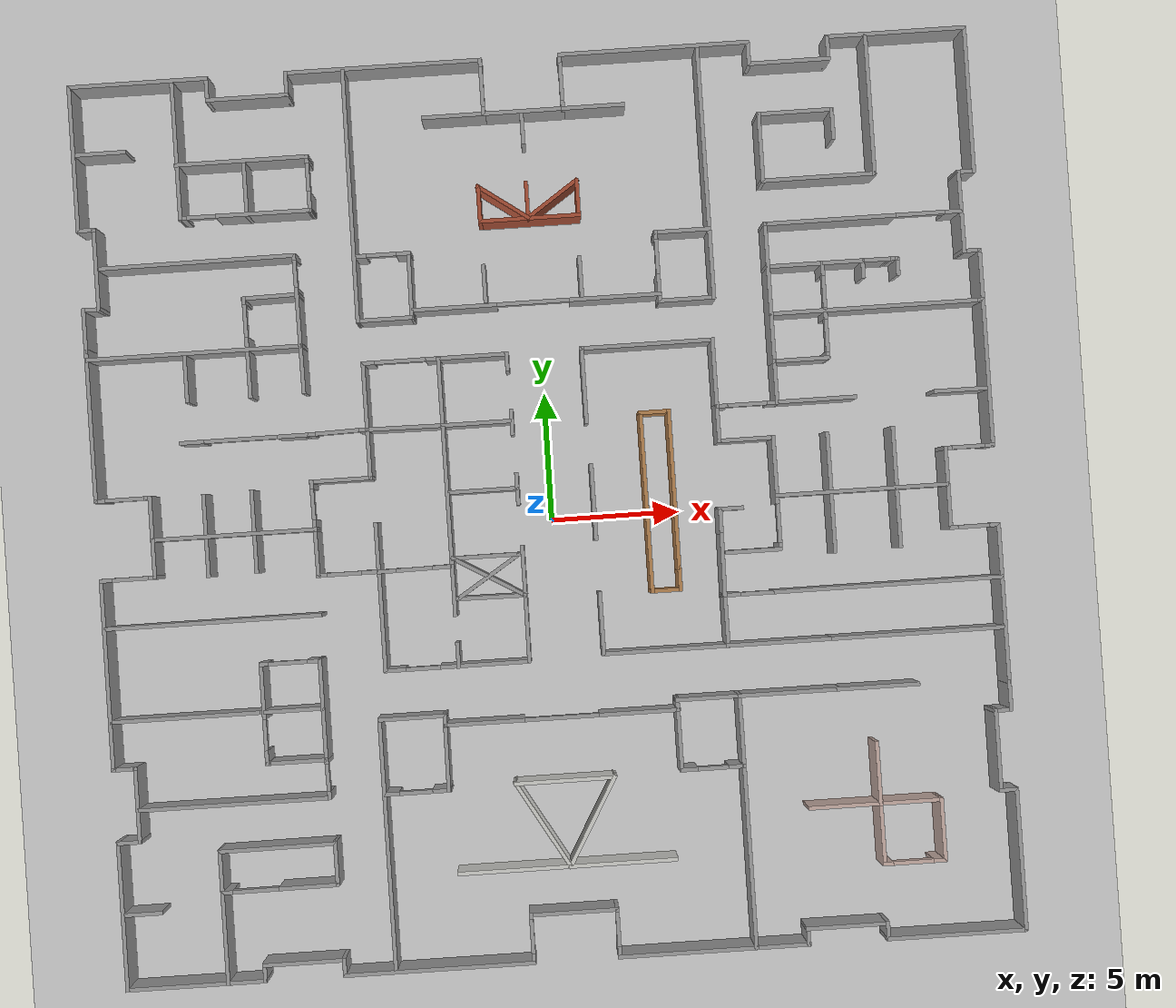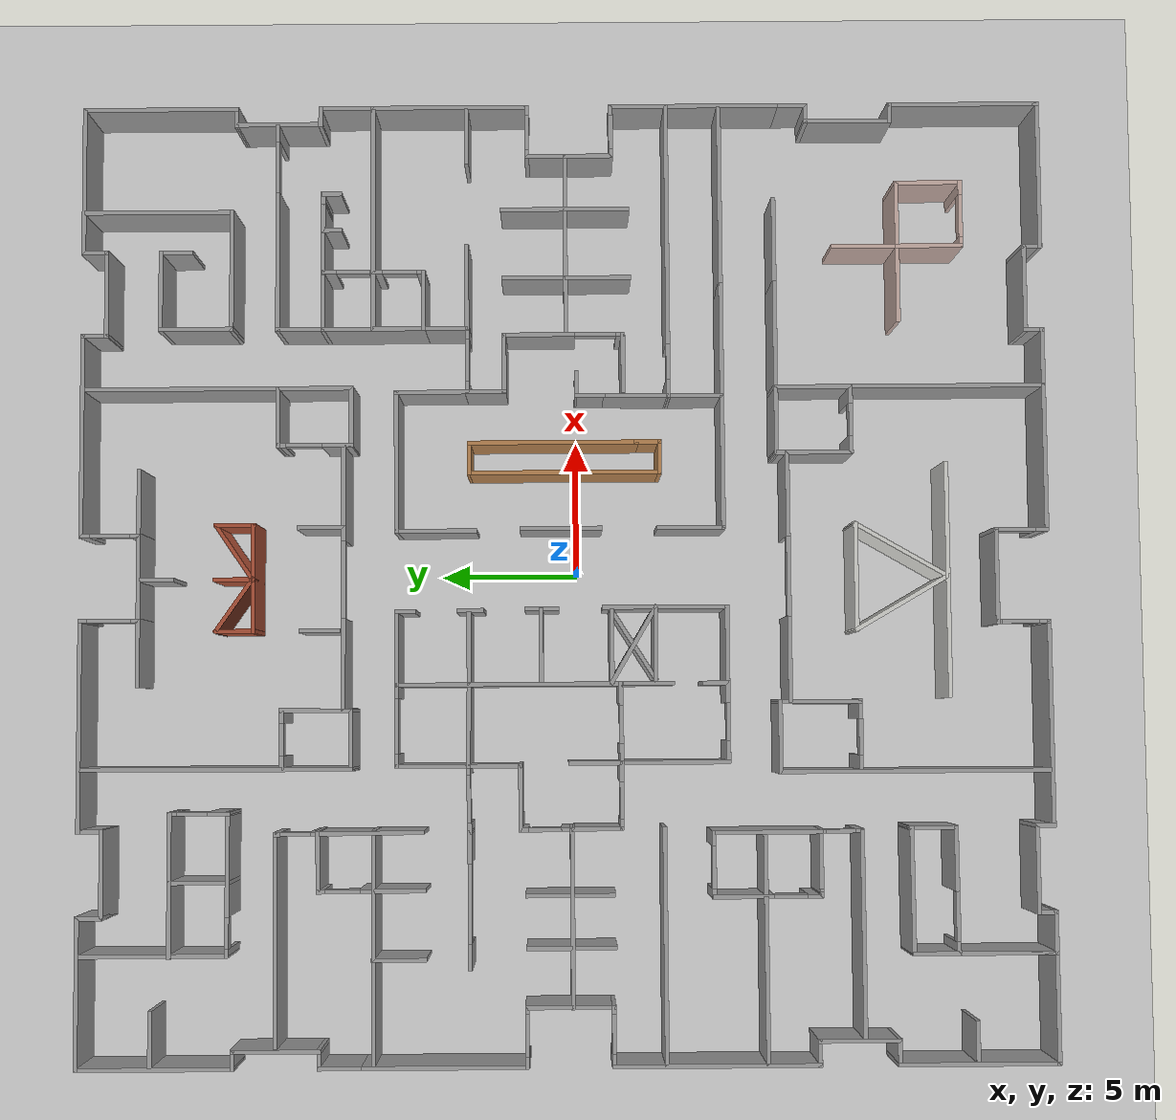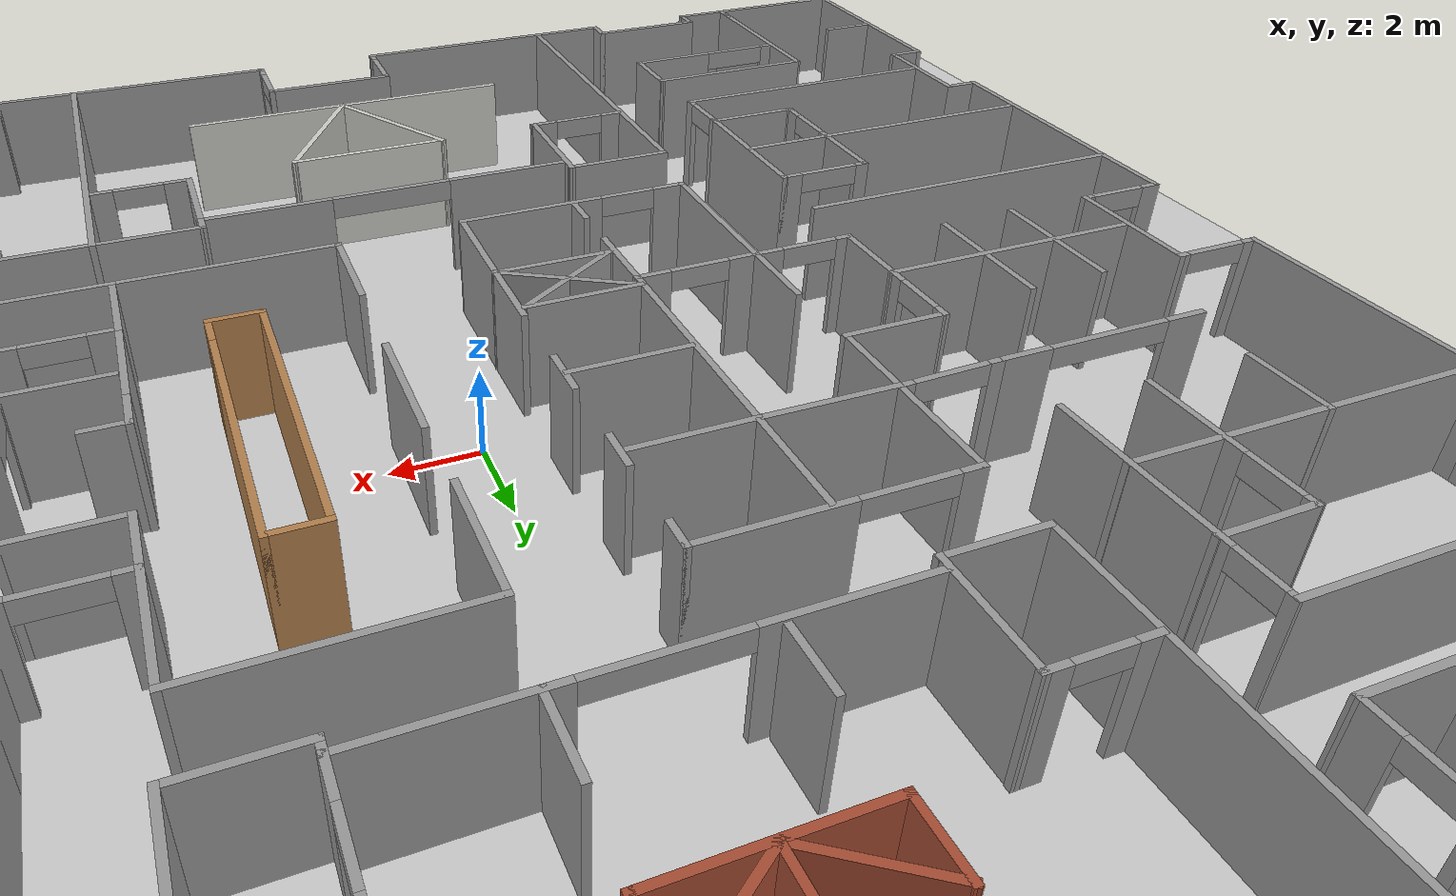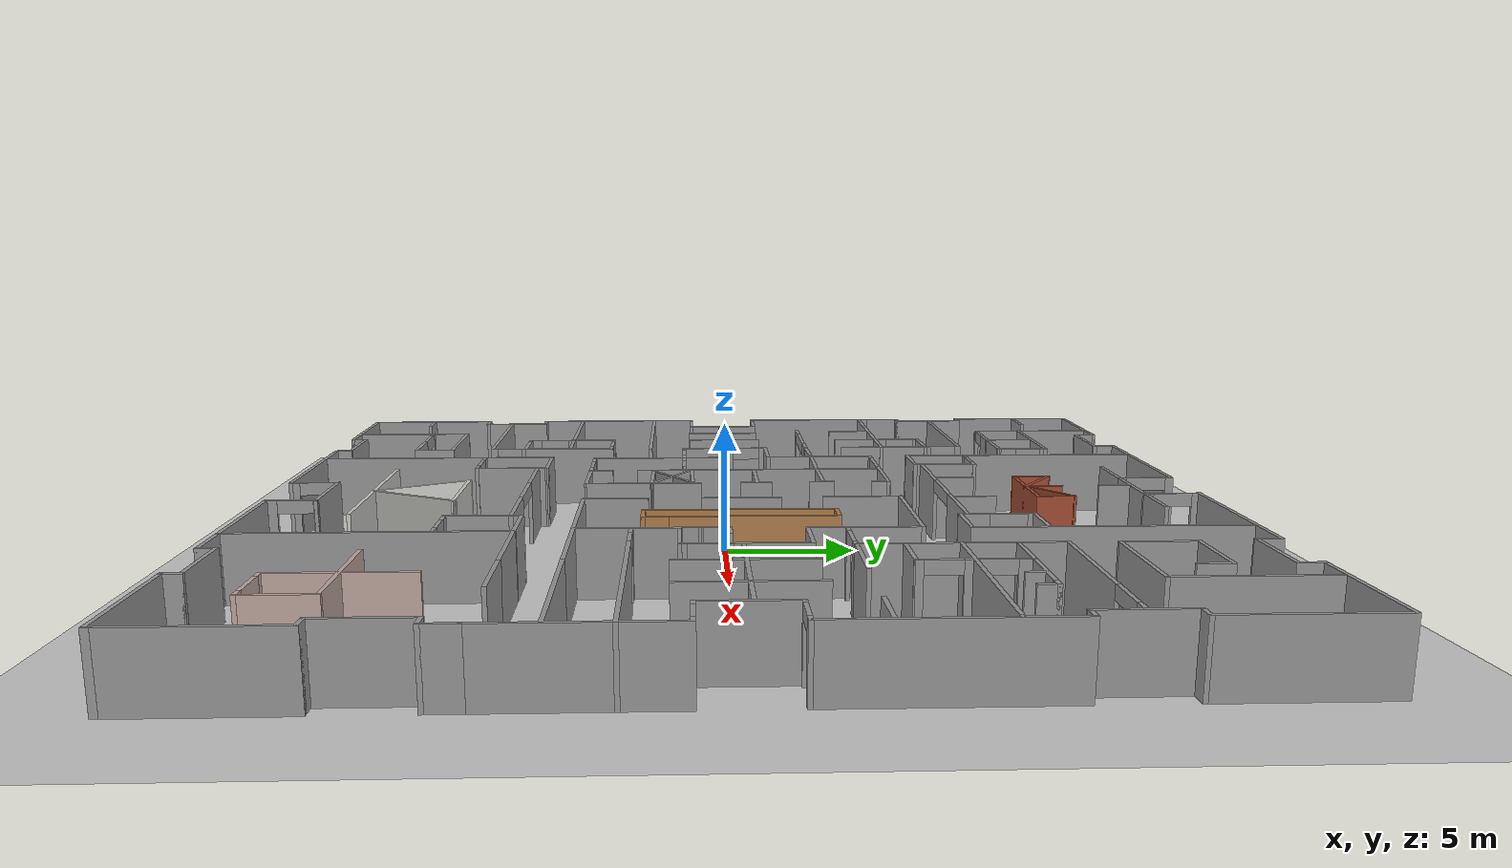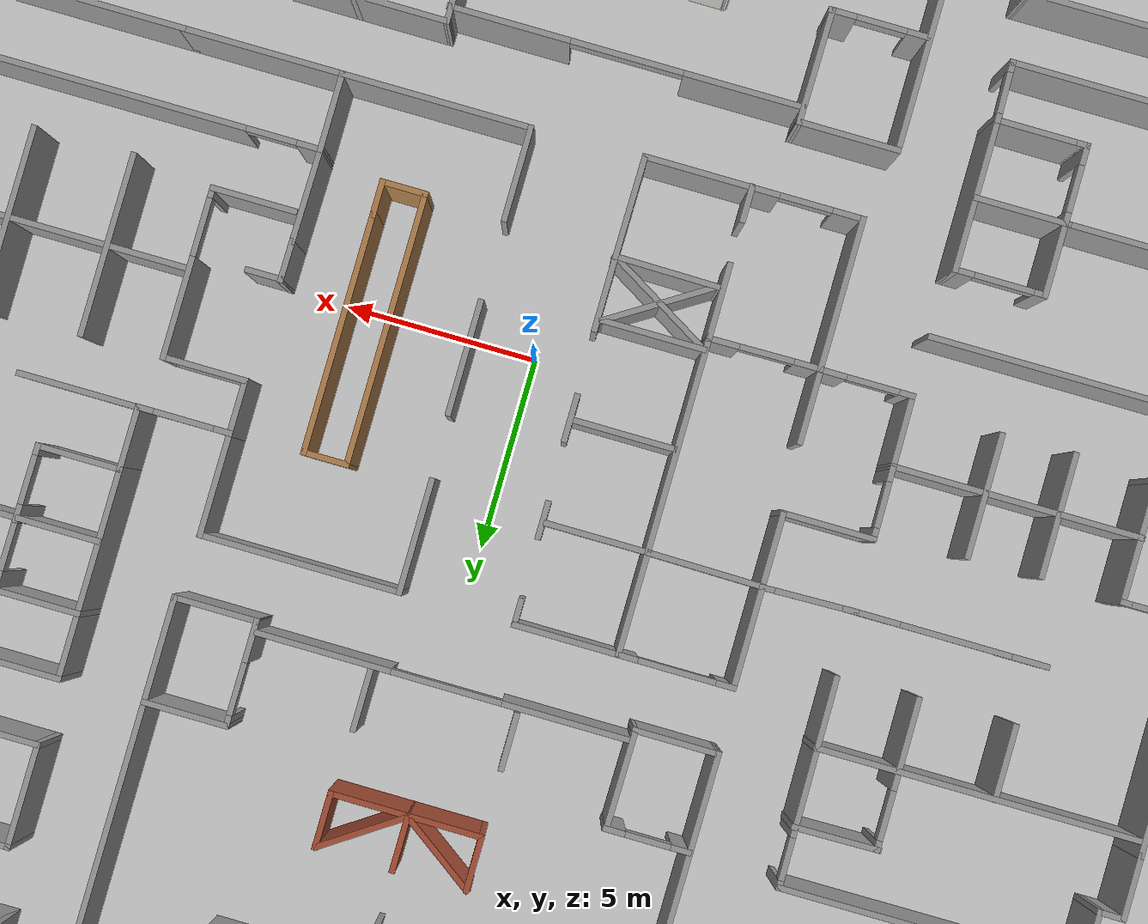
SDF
<sdf version="1.6">
 <world name="default">
  <light name="sun" type="directional">
   <pose>0 0 10 0 -0 0</pose>
   <diffuse>0.8 0.8 0.8 1</diffuse>
   <specular>0.2 0.2 0.2 1</specular>
   <attenuation>
    <range>1000</range>
    <constant>0.9</constant>
    <linear>0.01</linear>
    <quadratic>0.001</quadratic>
   </attenuation>
   <direction>-0.5 0.1 -0.9</direction>
  </light>
  <model name="ground_plane">
   <static>1</static>
   <link name="link">
    <collision name="collision">
     <geometry><plane><normal>0 0 1</normal><size>100 100</size></plane></geometry>
     <surface><friction><ode><mu>100</mu><mu2>50</mu2></ode></friction></surface>
    </collision>
    <visual name="visual">
     <cast_shadows>0</cast_shadows>
     <geometry><plane><normal>0 0 1</normal><size>100 100</size></plane></geometry>
     <material>
      <script><uri>file://media/materials/scripts/gazebo.material</uri><name>Gazebo/Grey</name></script>
     </material>
    </visual>
   </link>
  </model>
  <gravity>0 0 -9.8</gravity>
  <magnetic_field>6e-06 2.3e-05 -4.2e-05</magnetic_field>
  <atmosphere type="adiabatic"/>
  <physics name="default_physics" default="0" type="ode">
   <max_step_size>0.001</max_step_size>
   <real_time_factor>1</real_time_factor>
   <real_time_update_rate>1000</real_time_update_rate>
  </physics>
  <scene><ambient>0.4 0.4 0.4 1</ambient><background>0.7 0.7 0.7 1</background><shadows>1</shadows></scene>
  <audio><device>default</device></audio>
  <spherical_coordinates>
   <surface_model>EARTH_WGS84</surface_model>
   <latitude_deg>0</latitude_deg>
   <longitude_deg>0</longitude_deg>
   <elevation>0</elevation>
   <heading_deg>0</heading_deg>
  </spherical_coordinates>
  <model name="shopping01">
   <pose>-0.21266 0.4735 0 0 -0 0</pose>
   <link name="Wall_10">
    <pose>1.66978 16.52 0 0 -0 1.5708</pose>
    <visual name="Wall_10_Visual_0">
     <pose>-0.930319 0 1.25 0 -0 0</pose>
     <geometry><box><size>0.389362 0.15 2.5</size></box></geometry>
     <material>
      <script><uri>file://media/materials/scripts/gazebo.material</uri><name>Gazebo/Grey</name></script>
      <ambient>1 1 1 1</ambient>
     </material>
     <meta><layer>0</layer></meta>
    </visual>
    <collision name="Wall_10_Collision_0">
     <geometry><box><size>0.389362 0.15 2.5</size></box></geometry>
     <pose>-0.930319 0 1.25 0 -0 0</pose>
    </collision>
    <visual name="Wall_10_Visual_1">
     <pose>0.932354 0 1.25 0 -0 0</pose>
     <geometry><box><size>0.385291 0.15 2.5</size></box></geometry>
     <material>
      <script><uri>file://media/materials/scripts/gazebo.material</uri><name>Gazebo/Grey</name></script>
      <ambient>1 1 1 1</ambient>
     </material>
     <meta><layer>0</layer></meta>
    </visual>
    <collision name="Wall_10_Collision_1">
     <geometry><box><size>0.385291 0.15 2.5</size></box></geometry>
     <pose>0.932354 0 1.25 0 -0 0</pose>
    </collision>
    <visual name="Wall_10_Visual_2">
     <pose>0.002035 0 2.25 0 -0 0</pose>
     <geometry><box><size>1.47535 0.15 0.5</size></box></geometry>
     <material>
      <script><uri>file://media/materials/scripts/gazebo.material</uri><name>Gazebo/Grey</name></script>
      <ambient>1 1 1 1</ambient>
     </material>
     <meta><layer>0</layer></meta>
    </visual>
    <collision name="Wall_10_Collision_2">
     <geometry><box><size>1.47535 0.15 0.5</size></box></geometry>
     <pose>0.002035 0 2.25 0 -0 0</pose>
    </collision>
   </link>
   <link name="Wall_100">
    <collision name="Wall_100_Collision">
     <geometry><box><size>1 0.15 2.5</size></box></geometry>
     <pose>0 0 1.25 0 -0 0</pose>
    </collision>
    <visual name="Wall_100_Visual">
     <pose>0 0 1.25 0 -0 0</pose>
     <geometry><box><size>1 0.15 2.5</size></box></geometry>
     <material>
      <script><uri>file://media/materials/scripts/gazebo.material</uri><name>Gazebo/Grey</name></script>
      <ambient>1 1 1 1</ambient>
     </material>
     <meta><layer>0</layer></meta>
    </visual>
    <pose>-3.82251 -5.48575 0 0 -0 1.5708</pose>
   </link>
   <link name="Wall_103">
    <collision name="Wall_103_Collision">
     <geometry><box><size>8.25 0.15 2.5</size></box></geometry>
     <pose>0 0 1.25 0 -0 0</pose>
    </collision>
    <visual name="Wall_103_Visual">
     <pose>0 0 1.25 0 -0 0</pose>
     <geometry><box><size>8.25 0.15 2.5</size></box></geometry>
     <material>
      <script><uri>file://media/materials/scripts/gazebo.material</uri><name>Gazebo/Grey</name></script>
      <ambient>1 1 1 1</ambient>
     </material>
     <meta><layer>0</layer></meta>
    </visual>
    <pose>-3.82398 2.01144 0 0 -0 1.5708</pose>
   </link>
   <link name="Wall_105">
    <collision name="Wall_105_Collision">
     <geometry><box><size>2.75 0.15 2.5</size></box></geometry>
     <pose>0 0 1.25 0 -0 0</pose>
    </collision>
    <visual name="Wall_105_Visual">
     <pose>0 0 1.25 0 -0 0</pose>
     <geometry><box><size>2.75 0.15 2.5</size></box></geometry>
     <material>
      <script><uri>file://media/materials/scripts/gazebo.material</uri><name>Gazebo/Grey</name></script>
      <ambient>1 1 1 1</ambient>
     </material>
     <meta><layer>0</layer></meta>
    </visual>
    <pose>-2.5383 3.46978 0 0 -0 0</pose>
   </link>
   <link name="Wall_109">
    <collision name="Wall_109_Collision">
     <geometry><box><size>2.75 0.15 2.5</size></box></geometry>
     <pose>0 0 1.25 0 -0 0</pose>
    </collision>
    <visual name="Wall_109_Visual">
     <pose>0 0 1.25 0 -0 0</pose>
     <geometry><box><size>2.75 0.15 2.5</size></box></geometry>
     <material>
      <script><uri>file://media/materials/scripts/gazebo.material</uri><name>Gazebo/Grey</name></script>
      <ambient>1 1 1 1</ambient>
     </material>
     <meta><layer>0</layer></meta>
    </visual>
    <pose>-2.4356 0.846548 0 0 -0 0</pose>
   </link>
   <link name="Wall_11">
    <collision name="Wall_11_Collision">
     <geometry><box><size>7.5 0.15 2.5</size></box></geometry>
     <pose>0 0 1.25 0 -0 0</pose>
    </collision>
    <visual name="Wall_11_Visual">
     <pose>0 0 1.25 0 -0 0</pose>
     <geometry><box><size>7.5 0.15 2.5</size></box></geometry>
     <material>
      <script><uri>file://media/materials/scripts/gazebo.material</uri><name>Gazebo/Grey</name></script>
      <ambient>1 1 1 1</ambient>
     </material>
     <meta><layer>0</layer></meta>
    </visual>
    <pose>5.34478 17.57 0 0 -0 0</pose>
   </link>
   <link name="Wall_112">
    <collision name="Wall_112_Collision">
     <geometry><box><size>2.75 0.15 2.5</size></box></geometry>
     <pose>0 0 1.25 0 -0 0</pose>
    </collision>
    <visual name="Wall_112_Visual">
     <pose>0 0 1.25 0 -0 0</pose>
     <geometry><box><size>2.75 0.15 2.5</size></box></geometry>
     <material>
      <script><uri>file://media/materials/scripts/gazebo.material</uri><name>Gazebo/Grey</name></script>
      <ambient>1 1 1 1</ambient>
     </material>
     <meta><layer>0</layer></meta>
    </visual>
    <pose>-2.47634 -1.71428 0 0 -0 0</pose>
   </link>
   <link name="Wall_114">
    <collision name="Wall_114_Collision">
     <geometry><box><size>9.90884 0.15 2.5</size></box></geometry>
     <pose>0 0 1.25 0 -0 0</pose>
    </collision>
    <visual name="Wall_114_Visual">
     <pose>0 0 1.25 0 -0 0</pose>
     <geometry><box><size>9.90884 0.15 2.5</size></box></geometry>
     <material>
      <script><uri>file://media/materials/scripts/gazebo.material</uri><name>Gazebo/Grey</name></script>
      <ambient>1 1 1 1</ambient>
     </material>
     <meta><layer>0</layer></meta>
    </visual>
    <pose>-6.8277 12.6229 0 0 -0 -1.57579</pose>
   </link>
   <link name="Wall_115">
    <collision name="Wall_115_Collision">
     <geometry><box><size>2.26087 0.15 2.5</size></box></geometry>
     <pose>0 0 1.25 0 -0 0</pose>
    </collision>
    <visual name="Wall_115_Visual">
     <pose>0 0 1.25 0 -0 0</pose>
     <geometry><box><size>2.26087 0.15 2.5</size></box></geometry>
     <material>
      <script><uri>file://media/materials/scripts/gazebo.material</uri><name>Gazebo/Grey</name></script>
      <ambient>1 1 1 1</ambient>
     </material>
     <meta><layer>0</layer></meta>
    </visual>
    <pose>-5.78364 7.74355 0 0 -0 0</pose>
   </link>
   <link name="Wall_116">
    <collision name="Wall_116_Collision">
     <geometry><box><size>2.65952 0.15 2.5</size></box></geometry>
     <pose>0 0 1.25 0 -0 0</pose>
    </collision>
    <visual name="Wall_116_Visual">
     <pose>0 0 1.25 0 -0 0</pose>
     <geometry><box><size>2.65952 0.15 2.5</size></box></geometry>
     <material>
      <script><uri>file://media/materials/scripts/gazebo.material</uri><name>Gazebo/Grey</name></script>
      <ambient>1 1 1 1</ambient>
     </material>
     <meta><layer>0</layer></meta>
    </visual>
    <pose>-4.72553 8.99791 0 0 -0 1.5583</pose>
   </link>
   <link name="Wall_117">
    <pose>-5.7479 10.2523 0 0 -0 3.14159</pose>
    <visual name="Wall_117_Visual_0">
     <pose>-0.845011 0 1.25 0 -0 0</pose>
     <geometry><box><size>0.570847 0.15 2.5</size></box></geometry>
     <material>
      <script><uri>file://media/materials/scripts/gazebo.material</uri><name>Gazebo/Grey</name></script>
      <ambient>1 1 1 1</ambient>
     </material>
     <meta><layer>0</layer></meta>
    </visual>
    <collision name="Wall_117_Collision_0">
     <geometry><box><size>0.570847 0.15 2.5</size></box></geometry>
     <pose>-0.845011 0 1.25 0 -0 0</pose>
    </collision>
    <visual name="Wall_117_Visual_1">
     <pose>0.866184 0 1.25 0 -0 0</pose>
     <geometry><box><size>0.528501 0.15 2.5</size></box></geometry>
     <material>
      <script><uri>file://media/materials/scripts/gazebo.material</uri><name>Gazebo/Grey</name></script>
      <ambient>1 1 1 1</ambient>
     </material>
     <meta><layer>0</layer></meta>
    </visual>
    <collision name="Wall_117_Collision_1">
     <geometry><box><size>0.528501 0.15 2.5</size></box></geometry>
     <pose>0.866184 0 1.25 0 -0 0</pose>
    </collision>
    <visual name="Wall_117_Visual_2">
     <pose>0.021173 0 2.25 0 -0 0</pose>
     <geometry><box><size>1.16152 0.15 0.5</size></box></geometry>
     <material>
      <script><uri>file://media/materials/scripts/gazebo.material</uri><name>Gazebo/Grey</name></script>
      <ambient>1 1 1 1</ambient>
     </material>
     <meta><layer>0</layer></meta>
    </visual>
    <collision name="Wall_117_Collision_2">
     <geometry><box><size>1.16152 0.15 0.5</size></box></geometry>
     <pose>0.021173 0 2.25 0 -0 0</pose>
    </collision>
   </link>
   <link name="Wall_119">
    <pose>0.137343 8.01732 0 0 -0 0</pose>
    <visual name="Wall_119_Visual_0">
     <pose>-3.20549 0 1.25 0 -0 0</pose>
     <geometry><box><size>3.33901 0.15 2.5</size></box></geometry>
     <material>
      <script><uri>file://media/materials/scripts/gazebo.material</uri><name>Gazebo/Grey</name></script>
      <ambient>1 1 1 1</ambient>
     </material>
     <meta><layer>0</layer></meta>
    </visual>
    <collision name="Wall_119_Collision_0">
     <geometry><box><size>3.33901 0.15 2.5</size></box></geometry>
     <pose>-3.20549 0 1.25 0 -0 0</pose>
    </collision>
    <visual name="Wall_119_Visual_1">
     <pose>3.08493 0 1.25 0 -0 0</pose>
     <geometry><box><size>3.58014 0.15 2.5</size></box></geometry>
     <material>
      <script><uri>file://media/materials/scripts/gazebo.material</uri><name>Gazebo/Grey</name></script>
      <ambient>1 1 1 1</ambient>
     </material>
     <meta><layer>0</layer></meta>
    </visual>
    <collision name="Wall_119_Collision_1">
     <geometry><box><size>3.58014 0.15 2.5</size></box></geometry>
     <pose>3.08493 0 1.25 0 -0 0</pose>
    </collision>
    <visual name="Wall_119_Visual_2">
     <pose>-0.120565 0 2.25 0 -0 0</pose>
     <geometry><box><size>2.83085 0.15 0.5</size></box></geometry>
     <material>
      <script><uri>file://media/materials/scripts/gazebo.material</uri><name>Gazebo/Grey</name></script>
      <ambient>1 1 1 1</ambient>
     </material>
     <meta><layer>0</layer></meta>
    </visual>
    <collision name="Wall_119_Collision_2">
     <geometry><box><size>2.83085 0.15 0.5</size></box></geometry>
     <pose>-0.120565 0 2.25 0 -0 0</pose>
    </collision>
   </link>
   <link name="Wall_12">
    <collision name="Wall_12_Collision">
     <geometry><box><size>1 0.15 2.5</size></box></geometry>
     <pose>0 0 1.25 0 -0 0</pose>
    </collision>
    <visual name="Wall_12_Visual">
     <pose>0 0 1.25 0 -0 0</pose>
     <geometry><box><size>1 0.15 2.5</size></box></geometry>
     <material>
      <script><uri>file://media/materials/scripts/gazebo.material</uri><name>Gazebo/Grey</name></script>
      <ambient>1 1 1 1</ambient>
     </material>
     <meta><layer>0</layer></meta>
    </visual>
    <pose>9.01978 17.145 0 0 -0 -1.5708</pose>
   </link>
   <link name="Wall_121">
    <collision name="Wall_121_Collision">
     <geometry><box><size>9.81925 0.15 2.5</size></box></geometry>
     <pose>0 0 1.25 0 -0 0</pose>
    </collision>
    <visual name="Wall_121_Visual">
     <pose>0 0 1.25 0 -0 0</pose>
     <geometry><box><size>9.81925 0.15 2.5</size></box></geometry>
     <material>
      <script><uri>file://media/materials/scripts/gazebo.material</uri><name>Gazebo/Grey</name></script>
      <ambient>1 1 1 1</ambient>
     </material>
     <meta><layer>0</layer></meta>
    </visual>
    <pose>7.04005 12.5786 0 0 -0 -1.57076</pose>
   </link>
   <link name="Wall_122">
    <collision name="Wall_122_Collision">
     <geometry><box><size>2.25 0.15 2.5</size></box></geometry>
     <pose>0 0 1.25 0 -0 0</pose>
    </collision>
    <visual name="Wall_122_Visual">
     <pose>0 0 1.25 0 -0 0</pose>
     <geometry><box><size>2.25 0.15 2.5</size></box></geometry>
     <material>
      <script><uri>file://media/materials/scripts/gazebo.material</uri><name>Gazebo/Grey</name></script>
      <ambient>1 1 1 1</ambient>
     </material>
     <meta><layer>0</layer></meta>
    </visual>
    <pose>5.99022 7.74395 0 0 -0 3.14159</pose>
   </link>
   <link name="Wall_123">
    <pose>4.94005 9.07858 0 0 -0 1.57092</pose>
    <visual name="Wall_123_Visual_0">
     <pose>-0.843207 0 1.25 0 -0 0</pose>
     <geometry><box><size>1.13283 0.15 2.5</size></box></geometry>
     <material>
      <script><uri>file://media/materials/scripts/gazebo.material</uri><name>Gazebo/Grey</name></script>
      <ambient>1 1 1 1</ambient>
     </material>
     <meta><layer>0</layer></meta>
    </visual>
    <collision name="Wall_123_Collision_0">
     <geometry><box><size>1.13283 0.15 2.5</size></box></geometry>
     <pose>-0.843207 0 1.25 0 -0 0</pose>
    </collision>
    <visual name="Wall_123_Visual_1">
     <pose>1.23871 0 1.25 0 -0 0</pose>
     <geometry><box><size>0.341833 0.15 2.5</size></box></geometry>
     <material>
      <script><uri>file://media/materials/scripts/gazebo.material</uri><name>Gazebo/Grey</name></script>
      <ambient>1 1 1 1</ambient>
     </material>
     <meta><layer>0</layer></meta>
    </visual>
    <collision name="Wall_123_Collision_1">
     <geometry><box><size>0.341833 0.15 2.5</size></box></geometry>
     <pose>1.23871 0 1.25 0 -0 0</pose>
    </collision>
    <visual name="Wall_123_Visual_2">
     <pose>0.3955 0 2.25 0 -0 0</pose>
     <geometry><box><size>1.34458 0.15 0.5</size></box></geometry>
     <material>
      <script><uri>file://media/materials/scripts/gazebo.material</uri><name>Gazebo/Grey</name></script>
      <ambient>1 1 1 1</ambient>
     </material>
     <meta><layer>0</layer></meta>
    </visual>
    <collision name="Wall_123_Collision_2">
     <geometry><box><size>1.34458 0.15 0.5</size></box></geometry>
     <pose>0.3955 0 2.25 0 -0 0</pose>
    </collision>
   </link>
   <link name="Wall_124">
    <collision name="Wall_124_Collision">
     <geometry><box><size>2.25 0.15 2.5</size></box></geometry>
     <pose>0 0 1.25 0 -0 0</pose>
    </collision>
    <visual name="Wall_124_Visual">
     <pose>0 0 1.25 0 -0 0</pose>
     <geometry><box><size>2.25 0.15 2.5</size></box></geometry>
     <material>
      <script><uri>file://media/materials/scripts/gazebo.material</uri><name>Gazebo/Grey</name></script>
      <ambient>1 1 1 1</ambient>
     </material>
     <meta><layer>0</layer></meta>
    </visual>
    <pose>5.98988 10.4132 0 0 -0 0</pose>
   </link>
   <link name="Wall_126">
    <collision name="Wall_126_Collision">
     <geometry><box><size>1.5 0.15 2.5</size></box></geometry>
     <pose>0 0 1.25 0 -0 0</pose>
    </collision>
    <visual name="Wall_126_Visual">
     <pose>0 0 1.25 0 -0 0</pose>
     <geometry><box><size>1.5 0.15 2.5</size></box></geometry>
     <material>
      <script><uri>file://media/materials/scripts/gazebo.material</uri><name>Gazebo/Grey</name></script>
      <ambient>1 1 1 1</ambient>
     </material>
     <meta><layer>0</layer></meta>
    </visual>
    <pose>-1.83472 8.87354 0 0 -0 -1.5708</pose>
   </link>
   <link name="Wall_128">
    <collision name="Wall_128_Collision">
     <geometry><box><size>4 0.15 2.5</size></box></geometry>
     <pose>0 0 1.25 0 -0 0</pose>
    </collision>
    <visual name="Wall_128_Visual">
     <pose>0 0 1.25 0 -0 0</pose>
     <geometry><box><size>4 0.15 2.5</size></box></geometry>
     <material>
      <script><uri>file://media/materials/scripts/gazebo.material</uri><name>Gazebo/Bricks</name></script>
      <ambient>1 1 1 1</ambient>
     </material>
     <meta><layer>0</layer></meta>
    </visual>
    <pose>0.090278 11.2942 0 0 -0 0</pose>
   </link>
   <link name="Wall_13">
    <collision name="Wall_13_Collision">
     <geometry><box><size>3.25 0.15 2.5</size></box></geometry>
     <pose>0 0 1.25 0 -0 0</pose>
    </collision>
    <visual name="Wall_13_Visual">
     <pose>0 0 1.25 0 -0 0</pose>
     <geometry><box><size>3.25 0.15 2.5</size></box></geometry>
     <material>
      <script><uri>file://media/materials/scripts/gazebo.material</uri><name>Gazebo/Grey</name></script>
      <ambient>1 1 1 1</ambient>
     </material>
     <meta><layer>0</layer></meta>
    </visual>
    <pose>10.5698 16.72 0 0 -0 0</pose>
   </link>
   <link name="Wall_130">
    <collision name="Wall_130_Collision">
     <geometry><box><size>1.75 0.15 2.5</size></box></geometry>
     <pose>0 0 1.25 0 -0 0</pose>
    </collision>
    <visual name="Wall_130_Visual">
     <pose>0 0 1.25 0 -0 0</pose>
     <geometry><box><size>1.75 0.15 2.5</size></box></geometry>
     <material>
      <script><uri>file://media/materials/scripts/gazebo.material</uri><name>Gazebo/Grey</name></script>
      <ambient>1 1 1 1</ambient>
     </material>
     <meta><layer>0</layer></meta>
    </visual>
    <pose>1.92118 8.82789 0 0 -0 -1.5708</pose>
   </link>
   <link name="Wall_134">
    <collision name="Wall_134_Collision">
     <geometry><box><size>1.25 0.15 2.5</size></box></geometry>
     <pose>0 0 1.25 0 -0 0</pose>
    </collision>
    <visual name="Wall_134_Visual">
     <pose>0 0 1.25 0 -0 0</pose>
     <geometry><box><size>1.25 0.15 2.5</size></box></geometry>
     <material>
      <script><uri>file://media/materials/scripts/gazebo.material</uri><name>Gazebo/Grey</name></script>
      <ambient>1 1 1 1</ambient>
     </material>
     <meta><layer>0</layer></meta>
    </visual>
    <pose>0.043228 14.8056 0 0 -0 -1.5708</pose>
   </link>
   <link name="Wall_136">
    <collision name="Wall_136_Collision">
     <geometry><box><size>1.5 0.15 2.5</size></box></geometry>
     <pose>0 0 1.25 0 -0 0</pose>
    </collision>
    <visual name="Wall_136_Visual">
     <pose>0 0 1.25 0 -0 0</pose>
     <geometry><box><size>1.5 0.15 2.5</size></box></geometry>
     <material>
      <script><uri>file://media/materials/scripts/gazebo.material</uri><name>Gazebo/Bricks</name></script>
      <ambient>1 1 1 1</ambient>
     </material>
     <meta><layer>0</layer></meta>
    </visual>
    <pose>0.043228 11.9946 0 0 -0 -1.5708</pose>
   </link>
   <link name="Wall_138">
    <collision name="Wall_138_Collision">
     <geometry><box><size>1.5 0.15 2.5</size></box></geometry>
     <pose>0 0 1.25 0 -0 0</pose>
    </collision>
    <visual name="Wall_138_Visual">
     <pose>0 0 1.25 0 -0 0</pose>
     <geometry><box><size>1.5 0.15 2.5</size></box></geometry>
     <material>
      <script><uri>file://media/materials/scripts/gazebo.material</uri><name>Gazebo/Bricks</name></script>
      <ambient>1 1 1 1</ambient>
     </material>
     <meta><layer>0</layer></meta>
    </visual>
    <pose>-1.83472 11.9692 0 0 -0 1.5708</pose>
   </link>
   <link name="Wall_139">
    <collision name="Wall_139_Collision">
     <geometry><box><size>2.4481 0.15 2.5</size></box></geometry>
     <pose>0 0 1.25 0 -0 0</pose>
    </collision>
    <visual name="Wall_139_Visual">
     <pose>0 0 1.25 0 -0 0</pose>
     <geometry><box><size>2.4481 0.15 2.5</size></box></geometry>
     <material>
      <script><uri>file://media/materials/scripts/gazebo.material</uri><name>Gazebo/Bricks</name></script>
      <ambient>1 1 1 1</ambient>
     </material>
     <meta><layer>0</layer></meta>
    </visual>
    <pose>-0.895747 11.9819 0 0 -0 -0.614303</pose>
   </link>
   <link name="Wall_14">
    <collision name="Wall_14_Collision">
     <geometry><box><size>1 0.15 2.5</size></box></geometry>
     <pose>0 0 1.25 0 -0 0</pose>
    </collision>
    <visual name="Wall_14_Visual">
     <pose>0 0 1.25 0 -0 0</pose>
     <geometry><box><size>1 0.15 2.5</size></box></geometry>
     <material>
      <script><uri>file://media/materials/scripts/gazebo.material</uri><name>Gazebo/Grey</name></script>
      <ambient>1 1 1 1</ambient>
     </material>
     <meta><layer>0</layer></meta>
    </visual>
    <pose>12.1198 17.145 0 0 -0 1.5708</pose>
   </link>
   <link name="Wall_142">
    <collision name="Wall_142_Collision">
     <geometry><box><size>1.5 0.15 2.5</size></box></geometry>
     <pose>0 0 1.25 0 -0 0</pose>
    </collision>
    <visual name="Wall_142_Visual">
     <pose>0 0 1.25 0 -0 0</pose>
     <geometry><box><size>1.5 0.15 2.5</size></box></geometry>
     <material>
      <script><uri>file://media/materials/scripts/gazebo.material</uri><name>Gazebo/Bricks</name></script>
      <ambient>1 1 1 1</ambient>
     </material>
     <meta><layer>0</layer></meta>
    </visual>
    <pose>2.0179 11.9709 0 0 -0 -1.5708</pose>
   </link>
   <link name="Wall_144">
    <collision name="Wall_144_Collision">
     <geometry><box><size>2.51616 0.15 2.5</size></box></geometry>
     <pose>0 0 1.25 0 -0 0</pose>
    </collision>
    <visual name="Wall_144_Visual">
     <pose>0 0 1.25 0 -0 0</pose>
     <geometry><box><size>2.51616 0.15 2.5</size></box></geometry>
     <material>
      <script><uri>file://media/materials/scripts/gazebo.material</uri><name>Gazebo/Bricks</name></script>
      <ambient>1 1 1 1</ambient>
     </material>
     <meta><layer>0</layer></meta>
    </visual>
    <pose>1.023 11.9828 0 0 -0 0.594988</pose>
   </link>
   <link name="Wall_146">
    <collision name="Wall_146_Collision">
     <geometry><box><size>2.5 0.15 2.5</size></box></geometry>
     <pose>0 0 1.25 0 -0 0</pose>
    </collision>
    <visual name="Wall_146_Visual">
     <pose>0 0 1.25 0 -0 0</pose>
     <geometry><box><size>2.5 0.15 2.5</size></box></geometry>
     <material>
      <script><uri>file://media/materials/scripts/gazebo.material</uri><name>Gazebo/Grey</name></script>
      <ambient>1 1 1 1</ambient>
     </material>
     <meta><layer>0</layer></meta>
    </visual>
    <pose>-2.60522 15.47 0 0 -0 3.14159</pose>
   </link>
   <link name="Wall_148">
    <collision name="Wall_148_Collision">
     <geometry><box><size>2.5 0.15 2.5</size></box></geometry>
     <pose>0 0 1.25 0 -0 0</pose>
    </collision>
    <visual name="Wall_148_Visual">
     <pose>0 0 1.25 0 -0 0</pose>
     <geometry><box><size>2.5 0.15 2.5</size></box></geometry>
     <material>
      <script><uri>file://media/materials/scripts/gazebo.material</uri><name>Gazebo/Grey</name></script>
      <ambient>1 1 1 1</ambient>
     </material>
     <meta><layer>0</layer></meta>
    </visual>
    <pose>2.84478 15.47 0 0 -0 0</pose>
   </link>
   <link name="Wall_15">
    <collision name="Wall_15_Collision">
     <geometry><box><size>5.5 0.15 2.5</size></box></geometry>
     <pose>0 0 1.25 0 -0 0</pose>
    </collision>
    <visual name="Wall_15_Visual">
     <pose>0 0 1.25 0 -0 0</pose>
     <geometry><box><size>5.5 0.15 2.5</size></box></geometry>
     <material>
      <script><uri>file://media/materials/scripts/gazebo.material</uri><name>Gazebo/Grey</name></script>
      <ambient>1 1 1 1</ambient>
     </material>
     <meta><layer>0</layer></meta>
    </visual>
    <pose>14.7948 17.57 0 0 -0 0</pose>
   </link>
   <link name="Wall_150">
    <collision name="Wall_150_Collision">
     <geometry><box><size>5.5 0.15 2.5</size></box></geometry>
     <pose>0 0 1.25 0 -0 0</pose>
    </collision>
    <visual name="Wall_150_Visual">
     <pose>0 0 1.25 0 -0 0</pose>
     <geometry><box><size>5.5 0.15 2.5</size></box></geometry>
     <material>
      <script><uri>file://media/materials/scripts/gazebo.material</uri><name>Gazebo/Grey</name></script>
      <ambient>1 1 1 1</ambient>
     </material>
     <meta><layer>0</layer></meta>
    </visual>
    <pose>13.6065 14.8095 0 0 -0 -1.5708</pose>
   </link>
   <link name="Wall_155">
    <pose>13.0197 10.4465 0 0 -0 3.14159</pose>
    <visual name="Wall_155_Visual_0">
     <pose>-3.54597 0 1.25 0 -0 0</pose>
     <geometry><box><size>0.658053 0.15 2.5</size></box></geometry>
     <material>
      <script><uri>file://media/materials/scripts/gazebo.material</uri><name>Gazebo/Grey</name></script>
      <ambient>1 1 1 1</ambient>
     </material>
     <meta><layer>0</layer></meta>
    </visual>
    <collision name="Wall_155_Collision_0">
     <geometry><box><size>0.658053 0.15 2.5</size></box></geometry>
     <pose>-3.54597 0 1.25 0 -0 0</pose>
    </collision>
    <visual name="Wall_155_Visual_1">
     <pose>1.28217 0 1.25 0 -0 0</pose>
     <geometry><box><size>5.18566 0.15 2.5</size></box></geometry>
     <material>
      <script><uri>file://media/materials/scripts/gazebo.material</uri><name>Gazebo/Grey</name></script>
      <ambient>1 1 1 1</ambient>
     </material>
     <meta><layer>0</layer></meta>
    </visual>
    <collision name="Wall_155_Collision_1">
     <geometry><box><size>5.18566 0.15 2.5</size></box></geometry>
     <pose>1.28217 0 1.25 0 -0 0</pose>
    </collision>
    <visual name="Wall_155_Visual_2">
     <pose>-2.2638 0 2.25 0 -0 0</pose>
     <geometry><box><size>1.90629 0.15 0.5</size></box></geometry>
     <material>
      <script><uri>file://media/materials/scripts/gazebo.material</uri><name>Gazebo/Grey</name></script>
      <ambient>1 1 1 1</ambient>
     </material>
     <meta><layer>0</layer></meta>
    </visual>
    <collision name="Wall_155_Collision_2">
     <geometry><box><size>1.90629 0.15 0.5</size></box></geometry>
     <pose>-2.2638 0 2.25 0 -0 0</pose>
    </collision>
   </link>
   <link name="Wall_156">
    <collision name="Wall_156_Collision">
     <geometry><box><size>5.5 0.15 2.5</size></box></geometry>
     <pose>0 0 1.25 0 -0 0</pose>
    </collision>
    <visual name="Wall_156_Visual">
     <pose>0 0 1.25 0 -0 0</pose>
     <geometry><box><size>5.5 0.15 2.5</size></box></geometry>
     <material>
      <script><uri>file://media/materials/scripts/gazebo.material</uri><name>Gazebo/Grey</name></script>
      <ambient>1 1 1 1</ambient>
     </material>
     <meta><layer>0</layer></meta>
    </visual>
    <pose>9.21946 7.7712 0 0 -0 -1.57089</pose>
   </link>
   <link name="Wall_157">
    <collision name="Wall_157_Collision">
     <geometry><box><size>2.25 0.15 2.5</size></box></geometry>
     <pose>0 0 1.25 0 -0 0</pose>
    </collision>
    <visual name="Wall_157_Visual">
     <pose>0 0 1.25 0 -0 0</pose>
     <geometry><box><size>2.25 0.15 2.5</size></box></geometry>
     <material>
      <script><uri>file://media/materials/scripts/gazebo.material</uri><name>Gazebo/Grey</name></script>
      <ambient>1 1 1 1</ambient>
     </material>
     <meta><layer>0</layer></meta>
    </visual>
    <pose>10.2695 5.0962 0 0 -0 0.000237</pose>
   </link>
   <link name="Wall_158">
    <pose>11.3305 6.93931 0 0 -0 1.56492</pose>
    <visual name="Wall_158_Visual_0">
     <pose>-1.76364 0 1.25 0 -0 0</pose>
     <geometry><box><size>0.308432 0.15 2.5</size></box></geometry>
     <material>
      <script><uri>file://media/materials/scripts/gazebo.material</uri><name>Gazebo/Grey</name></script>
      <ambient>1 1 1 1</ambient>
     </material>
     <meta><layer>0</layer></meta>
    </visual>
    <collision name="Wall_158_Collision_0">
     <geometry><box><size>0.308432 0.15 2.5</size></box></geometry>
     <pose>-1.76364 0 1.25 0 -0 0</pose>
    </collision>
    <visual name="Wall_158_Visual_1">
     <pose>-0.107689 0 1.25 0 -0 0</pose>
     <geometry><box><size>0.471109 0.15 2.5</size></box></geometry>
     <material>
      <script><uri>file://media/materials/scripts/gazebo.material</uri><name>Gazebo/Grey</name></script>
      <ambient>1 1 1 1</ambient>
     </material>
     <meta><layer>0</layer></meta>
    </visual>
    <collision name="Wall_158_Collision_1">
     <geometry><box><size>0.471109 0.15 2.5</size></box></geometry>
     <pose>-0.107689 0 1.25 0 -0 0</pose>
    </collision>
    <visual name="Wall_158_Visual_2">
     <pose>1.63295 0 1.25 0 -0 0</pose>
     <geometry><box><size>0.569818 0.15 2.5</size></box></geometry>
     <material>
      <script><uri>file://media/materials/scripts/gazebo.material</uri><name>Gazebo/Grey</name></script>
      <ambient>1 1 1 1</ambient>
     </material>
     <meta><layer>0</layer></meta>
    </visual>
    <collision name="Wall_158_Collision_2">
     <geometry><box><size>0.569818 0.15 2.5</size></box></geometry>
     <pose>1.63295 0 1.25 0 -0 0</pose>
    </collision>
    <visual name="Wall_158_Visual_3">
     <pose>-0.976336 0 2.25 0 -0 0</pose>
     <geometry><box><size>1.26618 0.15 0.5</size></box></geometry>
     <material>
      <script><uri>file://media/materials/scripts/gazebo.material</uri><name>Gazebo/Grey</name></script>
      <ambient>1 1 1 1</ambient>
     </material>
     <meta><layer>0</layer></meta>
    </visual>
    <collision name="Wall_158_Collision_3">
     <geometry><box><size>1.26618 0.15 0.5</size></box></geometry>
     <pose>-0.976336 0 2.25 0 -0 0</pose>
    </collision>
    <visual name="Wall_158_Visual_4">
     <pose>0.737954 0 2.25 0 -0 0</pose>
     <geometry><box><size>1.22018 0.15 0.5</size></box></geometry>
     <material>
      <script><uri>file://media/materials/scripts/gazebo.material</uri><name>Gazebo/Grey</name></script>
      <ambient>1 1 1 1</ambient>
     </material>
     <meta><layer>0</layer></meta>
    </visual>
    <collision name="Wall_158_Collision_4">
     <geometry><box><size>1.22018 0.15 0.5</size></box></geometry>
     <pose>0.737954 0 2.25 0 -0 0</pose>
    </collision>
   </link>
   <link name="Wall_16">
    <collision name="Wall_16_Collision">
     <geometry><box><size>5.75 0.15 2.5</size></box></geometry>
     <pose>0 0 1.25 0 -0 0</pose>
    </collision>
    <visual name="Wall_16_Visual">
     <pose>0 0 1.25 0 -0 0</pose>
     <geometry><box><size>5.75 0.15 2.5</size></box></geometry>
     <material>
      <script><uri>file://media/materials/scripts/gazebo.material</uri><name>Gazebo/Grey</name></script>
      <ambient>1 1 1 1</ambient>
     </material>
     <meta><layer>0</layer></meta>
    </visual>
    <pose>17.4698 14.77 0 0 -0 -1.5708</pose>
   </link>
   <link name="Wall_162">
    <collision name="Wall_162_Collision">
     <geometry><box><size>2.27274 0.15 2.5</size></box></geometry>
     <pose>0 0 1.25 0 -0 0</pose>
    </collision>
    <visual name="Wall_162_Visual">
     <pose>0 0 1.25 0 -0 0</pose>
     <geometry><box><size>2.27274 0.15 2.5</size></box></geometry>
     <material>
      <script><uri>file://media/materials/scripts/gazebo.material</uri><name>Gazebo/Grey</name></script>
      <ambient>1 1 1 1</ambient>
     </material>
     <meta><layer>0</layer></meta>
    </visual>
    <pose>10.28 8.78217 0 0 -0 0</pose>
   </link>
   <link name="Wall_164">
    <collision name="Wall_164_Collision">
     <geometry><box><size>8.25 0.15 2.5</size></box></geometry>
     <pose>0 0 1.25 0 -0 0</pose>
    </collision>
    <visual name="Wall_164_Visual">
     <pose>0 0 1.25 0 -0 0</pose>
     <geometry><box><size>8.25 0.15 2.5</size></box></geometry>
     <material>
      <script><uri>file://media/materials/scripts/gazebo.material</uri><name>Gazebo/Grey</name></script>
      <ambient>1 1 1 1</ambient>
     </material>
     <meta><layer>0</layer></meta>
    </visual>
    <pose>13.2999 6.94076 0 0 -0 0</pose>
   </link>
   <link name="Wall_165">
    <collision name="Wall_165_Collision">
     <geometry><box><size>0.25 0.15 2.5</size></box></geometry>
     <pose>0 0 1.25 0 -0 0</pose>
    </collision>
    <visual name="Wall_165_Visual">
     <pose>0 0 1.25 0 -0 0</pose>
     <geometry><box><size>0.25 0.15 2.5</size></box></geometry>
     <material>
      <script><uri>file://media/materials/scripts/gazebo.material</uri><name>Gazebo/Grey</name></script>
      <ambient>1 1 1 1</ambient>
     </material>
     <meta><layer>0</layer></meta>
    </visual>
    <pose>17.3999 6.94076 0 0 -0 0</pose>
   </link>
   <link name="Wall_167">
    <pose>13.3049 3.50487 0 0 -0 3.14159</pose>
    <visual name="Wall_167_Visual_0">
     <pose>-3.08242 0 1.25 0 -0 0</pose>
     <geometry><box><size>2.08515 0.15 2.5</size></box></geometry>
     <material>
      <script><uri>file://media/materials/scripts/gazebo.material</uri><name>Gazebo/Grey</name></script>
      <ambient>1 1 1 1</ambient>
     </material>
     <meta><layer>0</layer></meta>
    </visual>
    <collision name="Wall_167_Collision_0">
     <geometry><box><size>2.08515 0.15 2.5</size></box></geometry>
     <pose>-3.08242 0 1.25 0 -0 0</pose>
    </collision>
    <visual name="Wall_167_Visual_1">
     <pose>2.54458 0 1.25 0 -0 0</pose>
     <geometry><box><size>3.16085 0.15 2.5</size></box></geometry>
     <material>
      <script><uri>file://media/materials/scripts/gazebo.material</uri><name>Gazebo/Grey</name></script>
      <ambient>1 1 1 1</ambient>
     </material>
     <meta><layer>0</layer></meta>
    </visual>
    <collision name="Wall_167_Collision_1">
     <geometry><box><size>3.16085 0.15 2.5</size></box></geometry>
     <pose>2.54458 0 1.25 0 -0 0</pose>
    </collision>
   </link>
   <link name="Wall_169">
    <collision name="Wall_169_Collision">
     <geometry><box><size>1.75 0.15 2.5</size></box></geometry>
     <pose>0 0 1.25 0 -0 0</pose>
    </collision>
    <visual name="Wall_169_Visual">
     <pose>0 0 1.25 0 -0 0</pose>
     <geometry><box><size>1.75 0.15 2.5</size></box></geometry>
     <material>
      <script><uri>file://media/materials/scripts/gazebo.material</uri><name>Gazebo/Grey</name></script>
      <ambient>1 1 1 1</ambient>
     </material>
     <meta><layer>0</layer></meta>
    </visual>
    <pose>9.21922 4.29596 0 0 -0 -1.5708</pose>
   </link>
   <link name="Wall_17">
    <collision name="Wall_17_Collision">
     <geometry><box><size>0.75 0.15 2.5</size></box></geometry>
     <pose>0 0 1.25 0 -0 0</pose>
    </collision>
    <visual name="Wall_17_Visual">
     <pose>0 0 1.25 0 -0 0</pose>
     <geometry><box><size>0.75 0.15 2.5</size></box></geometry>
     <material>
      <script><uri>file://media/materials/scripts/gazebo.material</uri><name>Gazebo/Grey</name></script>
      <ambient>1 1 1 1</ambient>
     </material>
     <meta><layer>0</layer></meta>
    </visual>
    <pose>17.1698 11.97 0 0 -0 3.14159</pose>
   </link>
   <link name="Wall_171">
    <pose>8.04422 3.49595 0 0 -0 3.14159</pose>
    <visual name="Wall_171_Visual_0">
     <pose>-1.01626 0 1.25 0 -0 0</pose>
     <geometry><box><size>0.467482 0.15 2.5</size></box></geometry>
     <material>
      <script><uri>file://media/materials/scripts/gazebo.material</uri><name>Gazebo/Grey</name></script>
      <ambient>1 1 1 1</ambient>
     </material>
     <meta><layer>0</layer></meta>
    </visual>
    <collision name="Wall_171_Collision_0">
     <geometry><box><size>0.467482 0.15 2.5</size></box></geometry>
     <pose>-1.01626 0 1.25 0 -0 0</pose>
    </collision>
    <visual name="Wall_171_Visual_1">
     <pose>1.00392 0 1.25 0 -0 0</pose>
     <geometry><box><size>0.492154 0.15 2.5</size></box></geometry>
     <material>
      <script><uri>file://media/materials/scripts/gazebo.material</uri><name>Gazebo/Grey</name></script>
      <ambient>1 1 1 1</ambient>
     </material>
     <meta><layer>0</layer></meta>
    </visual>
    <collision name="Wall_171_Collision_1">
     <geometry><box><size>0.492154 0.15 2.5</size></box></geometry>
     <pose>1.00392 0 1.25 0 -0 0</pose>
    </collision>
    <visual name="Wall_171_Visual_2">
     <pose>-0.012336 0 2.25 0 -0 0</pose>
     <geometry><box><size>1.54036 0.15 0.5</size></box></geometry>
     <material>
      <script><uri>file://media/materials/scripts/gazebo.material</uri><name>Gazebo/Grey</name></script>
      <ambient>1 1 1 1</ambient>
     </material>
     <meta><layer>0</layer></meta>
    </visual>
    <collision name="Wall_171_Collision_2">
     <geometry><box><size>1.54036 0.15 0.5</size></box></geometry>
     <pose>-0.012336 0 2.25 0 -0 0</pose>
    </collision>
   </link>
   <link name="Wall_172">
    <collision name="Wall_172_Collision">
     <geometry><box><size>2.75 0.15 2.5</size></box></geometry>
     <pose>0 0 1.25 0 -0 0</pose>
    </collision>
    <visual name="Wall_172_Visual">
     <pose>0 0 1.25 0 -0 0</pose>
     <geometry><box><size>2.75 0.15 2.5</size></box></geometry>
     <material>
      <script><uri>file://media/materials/scripts/gazebo.material</uri><name>Gazebo/Grey</name></script>
      <ambient>1 1 1 1</ambient>
     </material>
     <meta><layer>0</layer></meta>
    </visual>
    <pose>6.86922 4.79596 0 0 -0 1.5708</pose>
   </link>
   <link name="Wall_173">
    <collision name="Wall_173_Collision">
     <geometry><box><size>5.25 0.15 2.5</size></box></geometry>
     <pose>0 0 1.25 0 -0 0</pose>
    </collision>
    <visual name="Wall_173_Visual">
     <pose>0 0 1.25 0 -0 0</pose>
     <geometry><box><size>5.25 0.15 2.5</size></box></geometry>
     <material>
      <script><uri>file://media/materials/scripts/gazebo.material</uri><name>Gazebo/Grey</name></script>
      <ambient>1 1 1 1</ambient>
     </material>
     <meta><layer>0</layer></meta>
    </visual>
    <pose>4.31922 6.09596 0 0 -0 3.14159</pose>
   </link>
   <link name="Wall_174">
    <collision name="Wall_174_Collision">
     <geometry><box><size>3 0.15 2.5</size></box></geometry>
     <pose>0 0 1.25 0 -0 0</pose>
    </collision>
    <visual name="Wall_174_Visual">
     <pose>0 0 1.25 0 -0 0</pose>
     <geometry><box><size>3 0.15 2.5</size></box></geometry>
     <material>
      <script><uri>file://media/materials/scripts/gazebo.material</uri><name>Gazebo/Grey</name></script>
      <ambient>1 1 1 1</ambient>
     </material>
     <meta><layer>0</layer></meta>
    </visual>
    <pose>1.76922 4.67096 0 0 -0 -1.5708</pose>
   </link>
   <link name="Wall_176">
    <collision name="Wall_176_Collision">
     <geometry><box><size>3 0.15 2.5</size></box></geometry>
     <pose>0 0 1.25 0 -0 0</pose>
    </collision>
    <visual name="Wall_176_Visual">
     <pose>0 0 1.25 0 -0 0</pose>
     <geometry><box><size>3 0.15 2.5</size></box></geometry>
     <material>
      <script><uri>file://media/materials/scripts/gazebo.material</uri><name>Gazebo/Grey</name></script>
      <ambient>1 1 1 1</ambient>
     </material>
     <meta><layer>0</layer></meta>
    </visual>
    <pose>1.83663 0.105846 0 0 -0 -1.5708</pose>
   </link>
   <link name="Wall_178">
    <collision name="Wall_178_Collision">
     <geometry><box><size>2.5 0.15 2.5</size></box></geometry>
     <pose>0 0 1.25 0 -0 0</pose>
    </collision>
    <visual name="Wall_178_Visual">
     <pose>0 0 1.25 0 -0 0</pose>
     <geometry><box><size>2.5 0.15 2.5</size></box></geometry>
     <material>
      <script><uri>file://media/materials/scripts/gazebo.material</uri><name>Gazebo/Grey</name></script>
      <ambient>1 1 1 1</ambient>
     </material>
     <meta><layer>0</layer></meta>
    </visual>
    <pose>1.83663 -4.63262 0 0 -0 -1.5708</pose>
   </link>
   <link name="Wall_179">
    <collision name="Wall_179_Collision">
     <geometry><box><size>5 0.15 2.5</size></box></geometry>
     <pose>0 0 1.25 0 -0 0</pose>
    </collision>
    <visual name="Wall_179_Visual">
     <pose>0 0 1.25 0 -0 0</pose>
     <geometry><box><size>5 0.15 2.5</size></box></geometry>
     <material>
      <script><uri>file://media/materials/scripts/gazebo.material</uri><name>Gazebo/Grey</name></script>
      <ambient>1 1 1 1</ambient>
     </material>
     <meta><layer>0</layer></meta>
    </visual>
    <pose>4.26163 -5.80762 0 0 -0 0</pose>
   </link>
   <link name="Wall_18">
    <collision name="Wall_18_Collision">
     <geometry><box><size>3.24012 0.15 2.5</size></box></geometry>
     <pose>0 0 1.25 0 -0 0</pose>
    </collision>
    <visual name="Wall_18_Visual">
     <pose>0 0 1.25 0 -0 0</pose>
     <geometry><box><size>3.24012 0.15 2.5</size></box></geometry>
     <material>
      <script><uri>file://media/materials/scripts/gazebo.material</uri><name>Gazebo/Grey</name></script>
      <ambient>1 1 1 1</ambient>
     </material>
     <meta><layer>0</layer></meta>
    </visual>
    <pose>16.8797 10.425 0 0 -0 -1.56436</pose>
   </link>
   <link name="Wall_181">
    <collision name="Wall_181_Collision">
     <geometry><box><size>2.10458 0.15 2.5</size></box></geometry>
     <pose>0 0 1.25 0 -0 0</pose>
    </collision>
    <visual name="Wall_181_Visual">
     <pose>0 0 1.25 0 -0 0</pose>
     <geometry><box><size>2.10458 0.15 2.5</size></box></geometry>
     <material>
      <script><uri>file://media/materials/scripts/gazebo.material</uri><name>Gazebo/Grey</name></script>
      <ambient>1 1 1 1</ambient>
     </material>
     <meta><layer>0</layer></meta>
    </visual>
    <pose>6.68492 -4.83033 0 0 -0 1.57254</pose>
   </link>
   <link name="Wall_182">
    <pose>12.0817 -3.85304 0 0 -0 0</pose>
    <visual name="Wall_182_Visual_0">
     <pose>-5.1322 0 1.25 0 -0 0</pose>
     <geometry><box><size>0.682604 0.15 2.5</size></box></geometry>
     <material>
      <script><uri>file://media/materials/scripts/gazebo.material</uri><name>Gazebo/Grey</name></script>
      <ambient>1 1 1 1</ambient>
     </material>
     <meta><layer>0</layer></meta>
    </visual>
    <collision name="Wall_182_Collision_0">
     <geometry><box><size>0.682604 0.15 2.5</size></box></geometry>
     <pose>-5.1322 0 1.25 0 -0 0</pose>
    </collision>
    <visual name="Wall_182_Visual_1">
     <pose>0.990173 0 1.25 0 -0 0</pose>
     <geometry><box><size>8.96665 0.15 2.5</size></box></geometry>
     <material>
      <script><uri>file://media/materials/scripts/gazebo.material</uri><name>Gazebo/Grey</name></script>
      <ambient>1 1 1 1</ambient>
     </material>
     <meta><layer>0</layer></meta>
    </visual>
    <collision name="Wall_182_Collision_1">
     <geometry><box><size>8.96665 0.15 2.5</size></box></geometry>
     <pose>0.990173 0 1.25 0 -0 0</pose>
    </collision>
    <visual name="Wall_182_Visual_2">
     <pose>-4.14203 0 2.25 0 -0 0</pose>
     <geometry><box><size>1.29774 0.15 0.5</size></box></geometry>
     <material>
      <script><uri>file://media/materials/scripts/gazebo.material</uri><name>Gazebo/Grey</name></script>
      <ambient>1 1 1 1</ambient>
     </material>
     <meta><layer>0</layer></meta>
    </visual>
    <collision name="Wall_182_Collision_2">
     <geometry><box><size>1.29774 0.15 0.5</size></box></geometry>
     <pose>-4.14203 0 2.25 0 -0 0</pose>
    </collision>
   </link>
   <link name="Wall_184">
    <collision name="Wall_184_Collision">
     <geometry><box><size>1.5 0.15 2.5</size></box></geometry>
     <pose>0 0 1.25 0 -0 0</pose>
    </collision>
    <visual name="Wall_184_Visual">
     <pose>0 0 1.25 0 -0 0</pose>
     <geometry><box><size>1.5 0.15 2.5</size></box></geometry>
     <material>
      <script><uri>file://media/materials/scripts/gazebo.material</uri><name>Gazebo/Grey</name></script>
      <ambient>1 1 1 1</ambient>
     </material>
     <meta><layer>0</layer></meta>
    </visual>
    <pose>6.86922 2.82096 0 0 -0 -1.5708</pose>
   </link>
   <link name="Wall_185">
    <collision name="Wall_185_Collision">
     <geometry><box><size>2.25 0.15 2.5</size></box></geometry>
     <pose>0 0 1.25 0 -0 0</pose>
    </collision>
    <visual name="Wall_185_Visual">
     <pose>0 0 1.25 0 -0 0</pose>
     <geometry><box><size>2.25 0.15 2.5</size></box></geometry>
     <material>
      <script><uri>file://media/materials/scripts/gazebo.material</uri><name>Gazebo/Grey</name></script>
      <ambient>1 1 1 1</ambient>
     </material>
     <meta><layer>0</layer></meta>
    </visual>
    <pose>7.91922 2.14595 0 0 -0 0</pose>
   </link>
   <link name="Wall_186">
    <pose>8.96922 -0.029045 0 0 -0 -1.5708</pose>
    <visual name="Wall_186_Visual_0">
     <pose>-0.915651 0 1.25 0 -0 0</pose>
     <geometry><box><size>2.6687 0.15 2.5</size></box></geometry>
     <material>
      <script><uri>file://media/materials/scripts/gazebo.material</uri><name>Gazebo/Grey</name></script>
      <ambient>1 1 1 1</ambient>
     </material>
     <meta><layer>0</layer></meta>
    </visual>
    <collision name="Wall_186_Collision_0">
     <geometry><box><size>2.6687 0.15 2.5</size></box></geometry>
     <pose>-0.915651 0 1.25 0 -0 0</pose>
    </collision>
    <visual name="Wall_186_Visual_1">
     <pose>2.0851 0 1.25 0 -0 0</pose>
     <geometry><box><size>0.329802 0.15 2.5</size></box></geometry>
     <material>
      <script><uri>file://media/materials/scripts/gazebo.material</uri><name>Gazebo/Grey</name></script>
      <ambient>1 1 1 1</ambient>
     </material>
     <meta><layer>0</layer></meta>
    </visual>
    <collision name="Wall_186_Collision_1">
     <geometry><box><size>0.329802 0.15 2.5</size></box></geometry>
     <pose>2.0851 0 1.25 0 -0 0</pose>
    </collision>
    <visual name="Wall_186_Visual_2">
     <pose>1.16945 0 2.25 0 -0 0</pose>
     <geometry><box><size>1.5015 0.15 0.5</size></box></geometry>
     <material>
      <script><uri>file://media/materials/scripts/gazebo.material</uri><name>Gazebo/Grey</name></script>
      <ambient>1 1 1 1</ambient>
     </material>
     <meta><layer>0</layer></meta>
    </visual>
    <collision name="Wall_186_Collision_2">
     <geometry><box><size>1.5015 0.15 0.5</size></box></geometry>
     <pose>1.16945 0 2.25 0 -0 0</pose>
    </collision>
   </link>
   <link name="Wall_187">
    <collision name="Wall_187_Collision">
     <geometry><box><size>2.25 0.15 2.5</size></box></geometry>
     <pose>0 0 1.25 0 -0 0</pose>
    </collision>
    <visual name="Wall_187_Visual">
     <pose>0 0 1.25 0 -0 0</pose>
     <geometry><box><size>2.25 0.15 2.5</size></box></geometry>
     <material>
      <script><uri>file://media/materials/scripts/gazebo.material</uri><name>Gazebo/Grey</name></script>
      <ambient>1 1 1 1</ambient>
     </material>
     <meta><layer>0</layer></meta>
    </visual>
    <pose>7.91922 -2.20404 0 0 -0 3.14159</pose>
   </link>
   <link name="Wall_19">
    <collision name="Wall_19_Collision">
     <geometry><box><size>0.75 0.15 2.5</size></box></geometry>
     <pose>0 0 1.25 0 -0 0</pose>
    </collision>
    <visual name="Wall_19_Visual">
     <pose>0 0 1.25 0 -0 0</pose>
     <geometry><box><size>0.75 0.15 2.5</size></box></geometry>
     <material>
      <script><uri>file://media/materials/scripts/gazebo.material</uri><name>Gazebo/Grey</name></script>
      <ambient>1 1 1 1</ambient>
     </material>
     <meta><layer>0</layer></meta>
    </visual>
    <pose>17.1797 8.87999 0 0 -0 0</pose>
   </link>
   <link name="Wall_190">
    <collision name="Wall_190_Collision">
     <geometry><box><size>2.52682 0.15 2.5</size></box></geometry>
     <pose>0 0 1.25 0 -0 0</pose>
    </collision>
    <visual name="Wall_190_Visual">
     <pose>0 0 1.25 0 -0 0</pose>
     <geometry><box><size>2.52682 0.15 2.5</size></box></geometry>
     <material>
      <script><uri>file://media/materials/scripts/gazebo.material</uri><name>Gazebo/Grey</name></script>
      <ambient>1 1 1 1</ambient>
     </material>
     <meta><layer>0</layer></meta>
    </visual>
    <pose>6.69807 -2.66458 0 0 -0 1.5583</pose>
   </link>
   <link name="Wall_191">
    <collision name="Wall_191_Collision">
     <geometry><box><size>1.13785 0.15 2.5</size></box></geometry>
     <pose>0 0 1.25 0 -0 0</pose>
    </collision>
    <visual name="Wall_191_Visual">
     <pose>0 0 1.25 0 -0 0</pose>
     <geometry><box><size>1.13785 0.15 2.5</size></box></geometry>
     <material>
      <script><uri>file://media/materials/scripts/gazebo.material</uri><name>Gazebo/Grey</name></script>
      <ambient>1 1 1 1</ambient>
     </material>
     <meta><layer>0</layer></meta>
    </visual>
    <pose>6.7179 -0.982221 0 0 -0 1.56073</pose>
   </link>
   <link name="Wall_193">
    <collision name="Wall_193_Collision">
     <geometry><box><size>6.75 0.15 2.5</size></box></geometry>
     <pose>0 0 1.25 0 -0 0</pose>
    </collision>
    <visual name="Wall_193_Visual">
     <pose>0 0 1.25 0 -0 0</pose>
     <geometry><box><size>6.75 0.15 2.5</size></box></geometry>
     <material>
      <script><uri>file://media/materials/scripts/gazebo.material</uri><name>Gazebo/Grey</name></script>
      <ambient>1 1 1 1</ambient>
     </material>
     <meta><layer>0</layer></meta>
    </visual>
    <pose>12.2861 -0.121711 0 0 -0 0</pose>
   </link>
   <link name="Wall_195">
    <collision name="Wall_195_Collision">
     <geometry><box><size>1 0.15 2.5</size></box></geometry>
     <pose>0 0 1.25 0 -0 0</pose>
    </collision>
    <visual name="Wall_195_Visual">
     <pose>0 0 1.25 0 -0 0</pose>
     <geometry><box><size>1 0.15 2.5</size></box></geometry>
     <material>
      <script><uri>file://media/materials/scripts/gazebo.material</uri><name>Gazebo/Grey</name></script>
      <ambient>1 1 1 1</ambient>
     </material>
     <meta><layer>0</layer></meta>
    </visual>
    <pose>7.14787 -0.498266 0 0 -0 0</pose>
   </link>
   <link name="Wall_199">
    <collision name="Wall_199_Collision">
     <geometry><box><size>1.25 0.15 2.5</size></box></geometry>
     <pose>0 0 1.25 0 -0 0</pose>
    </collision>
    <visual name="Wall_199_Visual">
     <pose>0 0 1.25 0 -0 0</pose>
     <geometry><box><size>1.25 0.15 2.5</size></box></geometry>
     <material>
      <script><uri>file://media/materials/scripts/gazebo.material</uri><name>Gazebo/Wood</name></script>
      <ambient>1 1 1 1</ambient>
     </material>
     <meta><layer>0</layer></meta>
    </visual>
    <pose>4.43723 3.44103 0 0 -0 0</pose>
   </link>
   <link name="Wall_200">
    <collision name="Wall_200_Collision">
     <geometry><box><size>6.25 0.15 2.5</size></box></geometry>
     <pose>0 0 1.25 0 -0 0</pose>
    </collision>
    <visual name="Wall_200_Visual">
     <pose>0 0 1.25 0 -0 0</pose>
     <geometry><box><size>6.25 0.15 2.5</size></box></geometry>
     <material>
      <script><uri>file://media/materials/scripts/gazebo.material</uri><name>Gazebo/Wood</name></script>
      <ambient>1 1 1 1</ambient>
     </material>
     <meta><layer>0</layer></meta>
    </visual>
    <pose>4.98723 0.391029 0 0 -0 -1.5708</pose>
   </link>
   <link name="Wall_201">
    <collision name="Wall_201_Collision">
     <geometry><box><size>1 0.15 2.5</size></box></geometry>
     <pose>0 0 1.25 0 -0 0</pose>
    </collision>
    <visual name="Wall_201_Visual">
     <pose>0 0 1.25 0 -0 0</pose>
     <geometry><box><size>1 0.15 2.5</size></box></geometry>
     <material>
      <script><uri>file://media/materials/scripts/gazebo.material</uri><name>Gazebo/Wood</name></script>
      <ambient>1 1 1 1</ambient>
     </material>
     <meta><layer>0</layer></meta>
    </visual>
    <pose>4.98723 -3.08397 0 0 -0 -1.5708</pose>
   </link>
   <link name="Wall_202">
    <collision name="Wall_202_Collision">
     <geometry><box><size>1.25 0.15 2.5</size></box></geometry>
     <pose>0 0 1.25 0 -0 0</pose>
    </collision>
    <visual name="Wall_202_Visual">
     <pose>0 0 1.25 0 -0 0</pose>
     <geometry><box><size>1.25 0.15 2.5</size></box></geometry>
     <material>
      <script><uri>file://media/materials/scripts/gazebo.material</uri><name>Gazebo/Wood</name></script>
      <ambient>1 1 1 1</ambient>
     </material>
     <meta><layer>0</layer></meta>
    </visual>
    <pose>4.43723 -3.50897 0 0 -0 3.14159</pose>
   </link>
   <link name="Wall_203">
    <collision name="Wall_203_Collision">
     <geometry><box><size>7 0.15 2.5</size></box></geometry>
     <pose>0 0 1.25 0 -0 0</pose>
    </collision>
    <visual name="Wall_203_Visual">
     <pose>0 0 1.25 0 -0 0</pose>
     <geometry><box><size>7 0.15 2.5</size></box></geometry>
     <material>
      <script><uri>file://media/materials/scripts/gazebo.material</uri><name>Gazebo/Wood</name></script>
      <ambient>1 1 1 1</ambient>
     </material>
     <meta><layer>0</layer></meta>
    </visual>
    <pose>3.88723 -0.083971 0 0 -0 1.5708</pose>
   </link>
   <link name="Wall_205">
    <collision name="Wall_205_Collision">
     <geometry><box><size>8.5 0.15 2.5</size></box></geometry>
     <pose>0 0 1.25 0 -0 0</pose>
    </collision>
    <visual name="Wall_205_Visual">
     <pose>0 0 1.25 0 -0 0</pose>
     <geometry><box><size>8.5 0.15 2.5</size></box></geometry>
     <material>
      <script><uri>file://media/materials/scripts/gazebo.material</uri><name>Gazebo/Grey</name></script>
      <ambient>1 1 1 1</ambient>
     </material>
     <meta><layer>0</layer></meta>
    </visual>
    <pose>-13.2436 -3.55782 0 0 -0 3.14159</pose>
   </link>
   <link name="Wall_207">
    <collision name="Wall_207_Collision">
     <geometry><box><size>6.5 0.15 2.5</size></box></geometry>
     <pose>0 0 1.25 0 -0 0</pose>
    </collision>
    <visual name="Wall_207_Visual">
     <pose>0 0 1.25 0 -0 0</pose>
     <geometry><box><size>6.5 0.15 2.5</size></box></geometry>
     <material>
      <script><uri>file://media/materials/scripts/gazebo.material</uri><name>Gazebo/Grey</name></script>
      <ambient>1 1 1 1</ambient>
     </material>
     <meta><layer>0</layer></meta>
    </visual>
    <pose>-12.2257 -0.227017 0 0 -0 0</pose>
   </link>
   <link name="Wall_208">
    <pose>-9.06127 0.697969 0 0 -0 1.58217</pose>
    <visual name="Wall_208_Visual_0">
     <pose>-0.7706 0 1.25 0 -0 0</pose>
     <geometry><box><size>0.458558 0.15 2.5</size></box></geometry>
     <material>
      <script><uri>file://media/materials/scripts/gazebo.material</uri><name>Gazebo/Grey</name></script>
      <ambient>1 1 1 1</ambient>
     </material>
     <meta><layer>0</layer></meta>
    </visual>
    <collision name="Wall_208_Collision_0">
     <geometry><box><size>0.458558 0.15 2.5</size></box></geometry>
     <pose>-0.7706 0 1.25 0 -0 0</pose>
    </collision>
    <visual name="Wall_208_Visual_1">
     <pose>0.819729 0 1.25 0 -0 0</pose>
     <geometry><box><size>0.360301 0.15 2.5</size></box></geometry>
     <material>
      <script><uri>file://media/materials/scripts/gazebo.material</uri><name>Gazebo/Grey</name></script>
      <ambient>1 1 1 1</ambient>
     </material>
     <meta><layer>0</layer></meta>
    </visual>
    <collision name="Wall_208_Collision_1">
     <geometry><box><size>0.360301 0.15 2.5</size></box></geometry>
     <pose>0.819729 0 1.25 0 -0 0</pose>
    </collision>
    <visual name="Wall_208_Visual_2">
     <pose>0.049128 0 2.25 0 -0 0</pose>
     <geometry><box><size>1.1809 0.15 0.5</size></box></geometry>
     <material>
      <script><uri>file://media/materials/scripts/gazebo.material</uri><name>Gazebo/Grey</name></script>
      <ambient>1 1 1 1</ambient>
     </material>
     <meta><layer>0</layer></meta>
    </visual>
    <collision name="Wall_208_Collision_2">
     <geometry><box><size>1.1809 0.15 0.5</size></box></geometry>
     <pose>0.049128 0 2.25 0 -0 0</pose>
    </collision>
   </link>
   <link name="Wall_209">
    <collision name="Wall_209_Collision">
     <geometry><box><size>2.46 0.15 2.5</size></box></geometry>
     <pose>0 0 1.25 0 -0 0</pose>
    </collision>
    <visual name="Wall_209_Visual">
     <pose>0 0 1.25 0 -0 0</pose>
     <geometry><box><size>2.46 0.15 2.5</size></box></geometry>
     <material>
      <script><uri>file://media/materials/scripts/gazebo.material</uri><name>Gazebo/Grey</name></script>
      <ambient>1 1 1 1</ambient>
     </material>
     <meta><layer>0</layer></meta>
    </visual>
    <pose>-7.91678 1.62295 0 0 -0 0</pose>
   </link>
   <link name="Wall_21">
    <collision name="Wall_21_Collision">
     <geometry><box><size>7.75 0.15 2.5</size></box></geometry>
     <pose>0 0 1.25 0 -0 0</pose>
    </collision>
    <visual name="Wall_21_Visual">
     <pose>0 0 1.25 0 -0 0</pose>
     <geometry><box><size>7.75 0.15 2.5</size></box></geometry>
     <material>
      <script><uri>file://media/materials/scripts/gazebo.material</uri><name>Gazebo/Grey</name></script>
      <ambient>1 1 1 1</ambient>
     </material>
     <meta><layer>0</layer></meta>
    </visual>
    <pose>17.4797 5.07999 0 0 -0 -1.5708</pose>
   </link>
   <link name="Wall_211">
    <collision name="Wall_211_Collision">
     <geometry><box><size>1.93704 0.15 2.5</size></box></geometry>
     <pose>0 0 1.25 0 -0 0</pose>
    </collision>
    <visual name="Wall_211_Visual">
     <pose>0 0 1.25 0 -0 0</pose>
     <geometry><box><size>1.93704 0.15 2.5</size></box></geometry>
     <material>
      <script><uri>file://media/materials/scripts/gazebo.material</uri><name>Gazebo/Grey</name></script>
      <ambient>1 1 1 1</ambient>
     </material>
     <meta><layer>0</layer></meta>
    </visual>
    <pose>-9.04205 -1.1205 0 0 -0 -1.56106</pose>
   </link>
   <link name="Wall_212">
    <pose>-7.85836 -2.03137 0 0 -0 0</pose>
    <visual name="Wall_212_Visual_0">
     <pose>-1.04267 0 1.25 0 -0 0</pose>
     <geometry><box><size>0.414663 0.15 2.5</size></box></geometry>
     <material>
      <script><uri>file://media/materials/scripts/gazebo.material</uri><name>Gazebo/Grey</name></script>
      <ambient>1 1 1 1</ambient>
     </material>
     <meta><layer>0</layer></meta>
    </visual>
    <collision name="Wall_212_Collision_0">
     <geometry><box><size>0.414663 0.15 2.5</size></box></geometry>
     <pose>-1.04267 0 1.25 0 -0 0</pose>
    </collision>
    <visual name="Wall_212_Visual_1">
     <pose>0.879134 0 1.25 0 -0 0</pose>
     <geometry><box><size>0.741733 0.15 2.5</size></box></geometry>
     <material>
      <script><uri>file://media/materials/scripts/gazebo.material</uri><name>Gazebo/Grey</name></script>
      <ambient>1 1 1 1</ambient>
     </material>
     <meta><layer>0</layer></meta>
    </visual>
    <collision name="Wall_212_Collision_1">
     <geometry><box><size>0.741733 0.15 2.5</size></box></geometry>
     <pose>0.879134 0 1.25 0 -0 0</pose>
    </collision>
    <visual name="Wall_212_Visual_2">
     <pose>-0.163535 0 2.25 0 -0 0</pose>
     <geometry><box><size>1.3436 0.15 0.5</size></box></geometry>
     <material>
      <script><uri>file://media/materials/scripts/gazebo.material</uri><name>Gazebo/Grey</name></script>
      <ambient>1 1 1 1</ambient>
     </material>
     <meta><layer>0</layer></meta>
    </visual>
    <collision name="Wall_212_Collision_2">
     <geometry><box><size>1.3436 0.15 0.5</size></box></geometry>
     <pose>-0.163535 0 2.25 0 -0 0</pose>
    </collision>
   </link>
   <link name="Wall_214">
    <collision name="Wall_214_Collision">
     <geometry><box><size>2 0.15 2.5</size></box></geometry>
     <pose>0 0 1.25 0 -0 0</pose>
    </collision>
    <visual name="Wall_214_Visual">
     <pose>0 0 1.25 0 -0 0</pose>
     <geometry><box><size>2 0.15 2.5</size></box></geometry>
     <material>
      <script><uri>file://media/materials/scripts/gazebo.material</uri><name>Gazebo/Grey</name></script>
      <ambient>1 1 1 1</ambient>
     </material>
     <meta><layer>0</layer></meta>
    </visual>
    <pose>-6.68336 -1.10637 0 0 -0 1.5708</pose>
   </link>
   <link name="Wall_216">
    <collision name="Wall_216_Collision">
     <geometry><box><size>2 0.15 2.5</size></box></geometry>
     <pose>0 0 1.25 0 -0 0</pose>
    </collision>
    <visual name="Wall_216_Visual">
     <pose>0 0 1.25 0 -0 0</pose>
     <geometry><box><size>2 0.15 2.5</size></box></geometry>
     <material>
      <script><uri>file://media/materials/scripts/gazebo.material</uri><name>Gazebo/Grey</name></script>
      <ambient>1 1 1 1</ambient>
     </material>
     <meta><layer>0</layer></meta>
    </visual>
    <pose>-6.76342 2.57901 0 0 -0 -1.5708</pose>
   </link>
   <link name="Wall_218">
    <collision name="Wall_218_Collision">
     <geometry><box><size>3.07532 0.15 2.5</size></box></geometry>
     <pose>0 0 1.25 0 -0 0</pose>
    </collision>
    <visual name="Wall_218_Visual">
     <pose>0 0 1.25 0 -0 0</pose>
     <geometry><box><size>3.07532 0.15 2.5</size></box></geometry>
     <material>
      <script><uri>file://media/materials/scripts/gazebo.material</uri><name>Gazebo/Grey</name></script>
      <ambient>1 1 1 1</ambient>
     </material>
     <meta><layer>0</layer></meta>
    </visual>
    <pose>-5.30086 3.48689 0 0 -0 -0.011703</pose>
   </link>
   <link name="Wall_22">
    <pose>16.5547 1.27999 0 0 -0 3.14159</pose>
    <visual name="Wall_22_Visual_0">
     <pose>-0.802836 0 1.25 0 -0 0</pose>
     <geometry><box><size>0.394329 0.15 2.5</size></box></geometry>
     <material>
      <script><uri>file://media/materials/scripts/gazebo.material</uri><name>Gazebo/Grey</name></script>
      <ambient>1 1 1 1</ambient>
     </material>
     <meta><layer>0</layer></meta>
    </visual>
    <collision name="Wall_22_Collision_0">
     <geometry><box><size>0.394329 0.15 2.5</size></box></geometry>
     <pose>-0.802836 0 1.25 0 -0 0</pose>
    </collision>
    <visual name="Wall_22_Visual_1">
     <pose>0.84045 0 1.25 0 -0 0</pose>
     <geometry><box><size>0.319099 0.15 2.5</size></box></geometry>
     <material>
      <script><uri>file://media/materials/scripts/gazebo.material</uri><name>Gazebo/Grey</name></script>
      <ambient>1 1 1 1</ambient>
     </material>
     <meta><layer>0</layer></meta>
    </visual>
    <collision name="Wall_22_Collision_1">
     <geometry><box><size>0.319099 0.15 2.5</size></box></geometry>
     <pose>0.84045 0 1.25 0 -0 0</pose>
    </collision>
    <visual name="Wall_22_Visual_2">
     <pose>0.037615 0 2.25 0 -0 0</pose>
     <geometry><box><size>1.28657 0.15 0.5</size></box></geometry>
     <material>
      <script><uri>file://media/materials/scripts/gazebo.material</uri><name>Gazebo/Grey</name></script>
      <ambient>1 1 1 1</ambient>
     </material>
     <meta><layer>0</layer></meta>
    </visual>
    <collision name="Wall_22_Collision_2">
     <geometry><box><size>1.28657 0.15 0.5</size></box></geometry>
     <pose>0.037615 0 2.25 0 -0 0</pose>
    </collision>
   </link>
   <link name="Wall_220">
    <collision name="Wall_220_Collision">
     <geometry><box><size>3.25 0.15 2.5</size></box></geometry>
     <pose>0 0 1.25 0 -0 0</pose>
    </collision>
    <visual name="Wall_220_Visual">
     <pose>0 0 1.25 0 -0 0</pose>
     <geometry><box><size>3.25 0.15 2.5</size></box></geometry>
     <material>
      <script><uri>file://media/materials/scripts/gazebo.material</uri><name>Gazebo/Grey</name></script>
      <ambient>1 1 1 1</ambient>
     </material>
     <meta><layer>0</layer></meta>
    </visual>
    <pose>-13.2902 -0.192861 0 0 -0 1.5708</pose>
   </link>
   <link name="Wall_223">
    <collision name="Wall_223_Collision">
     <geometry><box><size>3.25 0.15 2.5</size></box></geometry>
     <pose>0 0 1.25 0 -0 0</pose>
    </collision>
    <visual name="Wall_223_Visual">
     <pose>0 0 1.25 0 -0 0</pose>
     <geometry><box><size>3.25 0.15 2.5</size></box></geometry>
     <material>
      <script><uri>file://media/materials/scripts/gazebo.material</uri><name>Gazebo/Grey</name></script>
      <ambient>1 1 1 1</ambient>
     </material>
     <meta><layer>0</layer></meta>
    </visual>
    <pose>-11.412 -0.158079 0 0 -0 -1.5708</pose>
   </link>
   <link name="Wall_225">
    <collision name="Wall_225_Collision">
     <geometry><box><size>4.75 0.15 2.5</size></box></geometry>
     <pose>0 0 1.25 0 -0 0</pose>
    </collision>
    <visual name="Wall_225_Visual">
     <pose>0 0 1.25 0 -0 0</pose>
     <geometry><box><size>4.75 0.15 2.5</size></box></geometry>
     <material>
      <script><uri>file://media/materials/scripts/gazebo.material</uri><name>Gazebo/Grey</name></script>
      <ambient>1 1 1 1</ambient>
     </material>
     <meta><layer>0</layer></meta>
    </visual>
    <pose>11.0792 -0.143171 0 0 -0 -1.5708</pose>
   </link>
   <link name="Wall_227">
    <collision name="Wall_227_Collision">
     <geometry><box><size>4.75 0.15 2.5</size></box></geometry>
     <pose>0 0 1.25 0 -0 0</pose>
    </collision>
    <visual name="Wall_227_Visual">
     <pose>0 0 1.25 0 -0 0</pose>
     <geometry><box><size>4.75 0.15 2.5</size></box></geometry>
     <material>
      <script><uri>file://media/materials/scripts/gazebo.material</uri><name>Gazebo/Grey</name></script>
      <ambient>1 1 1 1</ambient>
     </material>
     <meta><layer>0</layer></meta>
    </visual>
    <pose>13.6343 -0.112754 0 0 -0 -1.5708</pose>
   </link>
   <link name="Wall_23">
    <collision name="Wall_23_Collision">
     <geometry><box><size>3.25 0.15 2.5</size></box></geometry>
     <pose>0 0 1.25 0 -0 0</pose>
    </collision>
    <visual name="Wall_23_Visual">
     <pose>0 0 1.25 0 -0 0</pose>
     <geometry><box><size>3.25 0.15 2.5</size></box></geometry>
     <material>
      <script><uri>file://media/materials/scripts/gazebo.material</uri><name>Gazebo/Grey</name></script>
      <ambient>1 1 1 1</ambient>
     </material>
     <meta><layer>0</layer></meta>
    </visual>
    <pose>15.6297 -0.270013 0 0 -0 -1.5708</pose>
   </link>
   <link name="Wall_232">
    <collision name="Wall_232_Collision">
     <geometry><box><size>2.72728 0.15 2.5</size></box></geometry>
     <pose>0 0 1.25 0 -0 0</pose>
    </collision>
    <visual name="Wall_232_Visual">
     <pose>0 0 1.25 0 -0 0</pose>
     <geometry><box><size>2.72728 0.15 2.5</size></box></geometry>
     <material>
      <script><uri>file://media/materials/scripts/gazebo.material</uri><name>Gazebo/Grey</name></script>
      <ambient>1 1 1 1</ambient>
     </material>
     <meta><layer>0</layer></meta>
    </visual>
    <pose>12.6243 8.77649 0 0 -0 -0.004412</pose>
   </link>
   <link name="Wall_237">
    <collision name="Wall_237_Collision">
     <geometry><box><size>0.5 0.15 2.5</size></box></geometry>
     <pose>0 0 1.25 0 -0 0</pose>
    </collision>
    <visual name="Wall_237_Visual">
     <pose>0 0 1.25 0 -0 0</pose>
     <geometry><box><size>0.5 0.15 2.5</size></box></geometry>
     <material>
      <script><uri>file://media/materials/scripts/gazebo.material</uri><name>Gazebo/Grey</name></script>
      <ambient>1 1 1 1</ambient>
     </material>
     <meta><layer>0</layer></meta>
    </visual>
    <pose>14.0879 8.7708 0 0 -0 0</pose>
   </link>
   <link name="Wall_238">
    <collision name="Wall_238_Collision">
     <geometry><box><size>0.75 0.15 2.5</size></box></geometry>
     <pose>0 0 1.25 0 -0 0</pose>
    </collision>
    <visual name="Wall_238_Visual">
     <pose>0 0 1.25 0 -0 0</pose>
     <geometry><box><size>0.75 0.15 2.5</size></box></geometry>
     <material>
      <script><uri>file://media/materials/scripts/gazebo.material</uri><name>Gazebo/Grey</name></script>
      <ambient>1 1 1 1</ambient>
     </material>
     <meta><layer>0</layer></meta>
    </visual>
    <pose>14.2629 8.4708 0 0 -0 -1.5708</pose>
   </link>
   <link name="Wall_24">
    <pose>16.5547 -1.82001 0 0 -0 0</pose>
    <visual name="Wall_24_Visual_0">
     <pose>-0.824092 0 1.25 0 -0 0</pose>
     <geometry><box><size>0.351815 0.15 2.5</size></box></geometry>
     <material>
      <script><uri>file://media/materials/scripts/gazebo.material</uri><name>Gazebo/Grey</name></script>
      <ambient>1 1 1 1</ambient>
     </material>
     <meta><layer>0</layer></meta>
    </visual>
    <collision name="Wall_24_Collision_0">
     <geometry><box><size>0.351815 0.15 2.5</size></box></geometry>
     <pose>-0.824092 0 1.25 0 -0 0</pose>
    </collision>
    <visual name="Wall_24_Visual_1">
     <pose>0.7921 0 1.25 0 -0 0</pose>
     <geometry><box><size>0.415799 0.15 2.5</size></box></geometry>
     <material>
      <script><uri>file://media/materials/scripts/gazebo.material</uri><name>Gazebo/Grey</name></script>
      <ambient>1 1 1 1</ambient>
     </material>
     <meta><layer>0</layer></meta>
    </visual>
    <collision name="Wall_24_Collision_1">
     <geometry><box><size>0.415799 0.15 2.5</size></box></geometry>
     <pose>0.7921 0 1.25 0 -0 0</pose>
    </collision>
    <visual name="Wall_24_Visual_2">
     <pose>-0.031992 0 2.25 0 -0 0</pose>
     <geometry><box><size>1.23239 0.15 0.5</size></box></geometry>
     <material>
      <script><uri>file://media/materials/scripts/gazebo.material</uri><name>Gazebo/Grey</name></script>
      <ambient>1 1 1 1</ambient>
     </material>
     <meta><layer>0</layer></meta>
    </visual>
    <collision name="Wall_24_Collision_2">
     <geometry><box><size>1.23239 0.15 0.5</size></box></geometry>
     <pose>-0.031992 0 2.25 0 -0 0</pose>
    </collision>
   </link>
   <link name="Wall_240">
    <collision name="Wall_240_Collision">
     <geometry><box><size>0.75 0.15 2.5</size></box></geometry>
     <pose>0 0 1.25 0 -0 0</pose>
    </collision>
    <visual name="Wall_240_Visual">
     <pose>0 0 1.25 0 -0 0</pose>
     <geometry><box><size>0.75 0.15 2.5</size></box></geometry>
     <material>
      <script><uri>file://media/materials/scripts/gazebo.material</uri><name>Gazebo/Grey</name></script>
      <ambient>1 1 1 1</ambient>
     </material>
     <meta><layer>0</layer></meta>
    </visual>
    <pose>12.9058 8.46153 0 0 -0 -1.5708</pose>
   </link>
   <link name="Wall_242">
    <collision name="Wall_242_Collision">
     <geometry><box><size>5.97821 0.15 2.5</size></box></geometry>
     <pose>0 0 1.25 0 -0 0</pose>
    </collision>
    <visual name="Wall_242_Visual">
     <pose>0 0 1.25 0 -0 0</pose>
     <geometry><box><size>5.97821 0.15 2.5</size></box></geometry>
     <material>
      <script><uri>file://media/materials/scripts/gazebo.material</uri><name>Gazebo/Grey</name></script>
      <ambient>1 1 1 1</ambient>
     </material>
     <meta><layer>0</layer></meta>
    </visual>
    <pose>-14.4847 -7.17684 0 0 -0 0</pose>
   </link>
   <link name="Wall_245">
    <collision name="Wall_245_Collision">
     <geometry><box><size>4 0.15 2.5</size></box></geometry>
     <pose>0 0 1.25 0 -0 0</pose>
    </collision>
    <visual name="Wall_245_Visual">
     <pose>0 0 1.25 0 -0 0</pose>
     <geometry><box><size>4 0.15 2.5</size></box></geometry>
     <material>
      <script><uri>file://media/materials/scripts/gazebo.material</uri><name>Gazebo/Grey</name></script>
      <ambient>1 1 1 1</ambient>
     </material>
     <meta><layer>0</layer></meta>
    </visual>
    <pose>-9.19877 -7.25184 0 0 -0 -1.5708</pose>
   </link>
   <link name="Wall_246">
    <collision name="Wall_246_Collision">
     <geometry><box><size>2.25 0.15 2.5</size></box></geometry>
     <pose>0 0 1.25 0 -0 0</pose>
    </collision>
    <visual name="Wall_246_Visual">
     <pose>0 0 1.25 0 -0 0</pose>
     <geometry><box><size>2.25 0.15 2.5</size></box></geometry>
     <material>
      <script><uri>file://media/materials/scripts/gazebo.material</uri><name>Gazebo/Grey</name></script>
      <ambient>1 1 1 1</ambient>
     </material>
     <meta><layer>0</layer></meta>
    </visual>
    <pose>-10.2488 -9.17684 0 0 -0 3.14159</pose>
   </link>
   <link name="Wall_247">
    <collision name="Wall_247_Collision">
     <geometry><box><size>0.25 0.15 2.5</size></box></geometry>
     <pose>0 0 1.25 0 -0 0</pose>
    </collision>
    <visual name="Wall_247_Visual">
     <pose>0 0 1.25 0 -0 0</pose>
     <geometry><box><size>0.25 0.15 2.5</size></box></geometry>
     <material>
      <script><uri>file://media/materials/scripts/gazebo.material</uri><name>Gazebo/Grey</name></script>
      <ambient>1 1 1 1</ambient>
     </material>
     <meta><layer>0</layer></meta>
    </visual>
    <pose>-11.3488 -9.17684 0 0 -0 3.14159</pose>
   </link>
   <link name="Wall_248">
    <collision name="Wall_248_Collision">
     <geometry><box><size>0.25 0.15 2.5</size></box></geometry>
     <pose>0 0 1.25 0 -0 0</pose>
    </collision>
    <visual name="Wall_248_Visual">
     <pose>0 0 1.25 0 -0 0</pose>
     <geometry><box><size>0.25 0.15 2.5</size></box></geometry>
     <material>
      <script><uri>file://media/materials/scripts/gazebo.material</uri><name>Gazebo/Grey</name></script>
      <ambient>1 1 1 1</ambient>
     </material>
     <meta><layer>0</layer></meta>
    </visual>
    <pose>-11.4488 -9.17684 0 0 -0 3.14159</pose>
   </link>
   <link name="Wall_25">
    <collision name="Wall_25_Collision">
     <geometry><box><size>6.25 0.15 2.5</size></box></geometry>
     <pose>0 0 1.25 0 -0 0</pose>
    </collision>
    <visual name="Wall_25_Visual">
     <pose>0 0 1.25 0 -0 0</pose>
     <geometry><box><size>6.25 0.15 2.5</size></box></geometry>
     <material>
      <script><uri>file://media/materials/scripts/gazebo.material</uri><name>Gazebo/Grey</name></script>
      <ambient>1 1 1 1</ambient>
     </material>
     <meta><layer>0</layer></meta>
    </visual>
    <pose>17.4797 -4.87001 0 0 -0 -1.5708</pose>
   </link>
   <link name="Wall_254">
    <pose>-11.4988 -7.25184 0 0 -0 1.5708</pose>
    <visual name="Wall_254_Visual_0">
     <pose>-1.71196 0 1.25 0 -0 0</pose>
     <geometry><box><size>0.576081 0.15 2.5</size></box></geometry>
     <material>
      <script><uri>file://media/materials/scripts/gazebo.material</uri><name>Gazebo/Grey</name></script>
      <ambient>1 1 1 1</ambient>
     </material>
     <meta><layer>0</layer></meta>
    </visual>
    <collision name="Wall_254_Collision_0">
     <geometry><box><size>0.576081 0.15 2.5</size></box></geometry>
     <pose>-1.71196 0 1.25 0 -0 0</pose>
    </collision>
    <visual name="Wall_254_Visual_1">
     <pose>0.897227 0 1.25 0 -0 0</pose>
     <geometry><box><size>2.20554 0.15 2.5</size></box></geometry>
     <material>
      <script><uri>file://media/materials/scripts/gazebo.material</uri><name>Gazebo/Grey</name></script>
      <ambient>1 1 1 1</ambient>
     </material>
     <meta><layer>0</layer></meta>
    </visual>
    <collision name="Wall_254_Collision_1">
     <geometry><box><size>2.20554 0.15 2.5</size></box></geometry>
     <pose>0.897227 0 1.25 0 -0 0</pose>
    </collision>
    <visual name="Wall_254_Visual_2">
     <pose>-0.814732 0 2.25 0 -0 0</pose>
     <geometry><box><size>1.21837 0.15 0.5</size></box></geometry>
     <material>
      <script><uri>file://media/materials/scripts/gazebo.material</uri><name>Gazebo/Grey</name></script>
      <ambient>1 1 1 1</ambient>
     </material>
     <meta><layer>0</layer></meta>
    </visual>
    <collision name="Wall_254_Collision_2">
     <geometry><box><size>1.21837 0.15 0.5</size></box></geometry>
     <pose>-0.814732 0 2.25 0 -0 0</pose>
    </collision>
   </link>
   <link name="Wall_255">
    <pose>-10.3488 -5.32684 0 0 -0 0</pose>
    <visual name="Wall_255_Visual_0">
     <pose>-1.04786 0 1.25 0 -0 0</pose>
     <geometry><box><size>0.354289 0.15 2.5</size></box></geometry>
     <material>
      <script><uri>file://media/materials/scripts/gazebo.material</uri><name>Gazebo/Grey</name></script>
      <ambient>1 1 1 1</ambient>
     </material>
     <meta><layer>0</layer></meta>
    </visual>
    <collision name="Wall_255_Collision_0">
     <geometry><box><size>0.354289 0.15 2.5</size></box></geometry>
     <pose>-1.04786 0 1.25 0 -0 0</pose>
    </collision>
    <visual name="Wall_255_Visual_1">
     <pose>0.945338 0 1.25 0 -0 0</pose>
     <geometry><box><size>0.559325 0.15 2.5</size></box></geometry>
     <material>
      <script><uri>file://media/materials/scripts/gazebo.material</uri><name>Gazebo/Grey</name></script>
      <ambient>1 1 1 1</ambient>
     </material>
     <meta><layer>0</layer></meta>
    </visual>
    <collision name="Wall_255_Collision_1">
     <geometry><box><size>0.559325 0.15 2.5</size></box></geometry>
     <pose>0.945338 0 1.25 0 -0 0</pose>
    </collision>
    <visual name="Wall_255_Visual_2">
     <pose>-0.102518 0 2.25 0 -0 0</pose>
     <geometry><box><size>1.53639 0.15 0.5</size></box></geometry>
     <material>
      <script><uri>file://media/materials/scripts/gazebo.material</uri><name>Gazebo/Grey</name></script>
      <ambient>1 1 1 1</ambient>
     </material>
     <meta><layer>0</layer></meta>
    </visual>
    <collision name="Wall_255_Collision_2">
     <geometry><box><size>1.53639 0.15 0.5</size></box></geometry>
     <pose>-0.102518 0 2.25 0 -0 0</pose>
    </collision>
   </link>
   <link name="Wall_257">
    <collision name="Wall_257_Collision">
     <geometry><box><size>2.5 0.15 2.5</size></box></geometry>
     <pose>0 0 1.25 0 -0 0</pose>
    </collision>
    <visual name="Wall_257_Visual">
     <pose>0 0 1.25 0 -0 0</pose>
     <geometry><box><size>2.5 0.15 2.5</size></box></geometry>
     <material>
      <script><uri>file://media/materials/scripts/gazebo.material</uri><name>Gazebo/Grey</name></script>
      <ambient>1 1 1 1</ambient>
     </material>
     <meta><layer>0</layer></meta>
    </visual>
    <pose>-10.3956 -7.17684 0 0 -0 0</pose>
   </link>
   <link name="Wall_259">
    <collision name="Wall_259_Collision">
     <geometry><box><size>7.5 0.15 2.5</size></box></geometry>
     <pose>0 0 1.25 0 -0 0</pose>
    </collision>
    <visual name="Wall_259_Visual">
     <pose>0 0 1.25 0 -0 0</pose>
     <geometry><box><size>7.5 0.15 2.5</size></box></geometry>
     <material>
      <script><uri>file://media/materials/scripts/gazebo.material</uri><name>Gazebo/Grey</name></script>
      <ambient>1 1 1 1</ambient>
     </material>
     <meta><layer>0</layer></meta>
    </visual>
    <pose>-12.876 -10.6609 0 0 -0 0</pose>
   </link>
   <link name="Wall_260">
    <pose>-9.18269 -9.91886 0 0 -0 1.59248</pose>
    <visual name="Wall_260_Visual_0">
     <pose>-0.654776 0 1.25 0 -0 0</pose>
     <geometry><box><size>0.324819 0.15 2.5</size></box></geometry>
     <material>
      <script><uri>file://media/materials/scripts/gazebo.material</uri><name>Gazebo/Grey</name></script>
      <ambient>1 1 1 1</ambient>
     </material>
     <meta><layer>0</layer></meta>
    </visual>
    <collision name="Wall_260_Collision_0">
     <geometry><box><size>0.324819 0.15 2.5</size></box></geometry>
     <pose>-0.654776 0 1.25 0 -0 0</pose>
    </collision>
    <visual name="Wall_260_Visual_1">
     <pose>0.691077 0 1.25 0 -0 0</pose>
     <geometry><box><size>0.252218 0.15 2.5</size></box></geometry>
     <material>
      <script><uri>file://media/materials/scripts/gazebo.material</uri><name>Gazebo/Grey</name></script>
      <ambient>1 1 1 1</ambient>
     </material>
     <meta><layer>0</layer></meta>
    </visual>
    <collision name="Wall_260_Collision_1">
     <geometry><box><size>0.252218 0.15 2.5</size></box></geometry>
     <pose>0.691077 0 1.25 0 -0 0</pose>
    </collision>
    <visual name="Wall_260_Visual_2">
     <pose>0.036301 0 2.25 0 -0 0</pose>
     <geometry><box><size>1.05733 0.15 0.5</size></box></geometry>
     <material>
      <script><uri>file://media/materials/scripts/gazebo.material</uri><name>Gazebo/Grey</name></script>
      <ambient>1 1 1 1</ambient>
     </material>
     <meta><layer>0</layer></meta>
    </visual>
    <collision name="Wall_260_Collision_2">
     <geometry><box><size>1.05733 0.15 0.5</size></box></geometry>
     <pose>0.036301 0 2.25 0 -0 0</pose>
    </collision>
   </link>
   <link name="Wall_263">
    <collision name="Wall_263_Collision">
     <geometry><box><size>1 0.15 2.5</size></box></geometry>
     <pose>0 0 1.25 0 -0 0</pose>
    </collision>
    <visual name="Wall_263_Visual">
     <pose>0 0 1.25 0 -0 0</pose>
     <geometry><box><size>1 0.15 2.5</size></box></geometry>
     <material>
      <script><uri>file://media/materials/scripts/gazebo.material</uri><name>Gazebo/Grey</name></script>
      <ambient>1 1 1 1</ambient>
     </material>
     <meta><layer>0</layer></meta>
    </visual>
    <pose>-13.5643 -17.1381 0 0 -0 -1.5708</pose>
   </link>
   <link name="Wall_264">
    <collision name="Wall_264_Collision">
     <geometry><box><size>5.25 0.15 2.5</size></box></geometry>
     <pose>0 0 1.25 0 -0 0</pose>
    </collision>
    <visual name="Wall_264_Visual">
     <pose>0 0 1.25 0 -0 0</pose>
     <geometry><box><size>5.25 0.15 2.5</size></box></geometry>
     <material>
      <script><uri>file://media/materials/scripts/gazebo.material</uri><name>Gazebo/Grey</name></script>
      <ambient>1 1 1 1</ambient>
     </material>
     <meta><layer>0</layer></meta>
    </visual>
    <pose>-13.5643 -15.0131 0 0 -0 1.5708</pose>
   </link>
   <link name="Wall_265">
    <collision name="Wall_265_Collision">
     <geometry><box><size>4.61691 0.15 2.5</size></box></geometry>
     <pose>0 0 1.25 0 -0 0</pose>
    </collision>
    <visual name="Wall_265_Visual">
     <pose>0 0 1.25 0 -0 0</pose>
     <geometry><box><size>4.61691 0.15 2.5</size></box></geometry>
     <material>
      <script><uri>file://media/materials/scripts/gazebo.material</uri><name>Gazebo/Grey</name></script>
      <ambient>1 1 1 1</ambient>
     </material>
     <meta><layer>0</layer></meta>
    </visual>
    <pose>-11.3309 -12.4517 0 0 -0 0.005062</pose>
   </link>
   <link name="Wall_266">
    <collision name="Wall_266_Collision">
     <geometry><box><size>1.75 0.15 2.5</size></box></geometry>
     <pose>0 0 1.25 0 -0 0</pose>
    </collision>
    <visual name="Wall_266_Visual">
     <pose>0 0 1.25 0 -0 0</pose>
     <geometry><box><size>1.75 0.15 2.5</size></box></geometry>
     <material>
      <script><uri>file://media/materials/scripts/gazebo.material</uri><name>Gazebo/Grey</name></script>
      <ambient>1 1 1 1</ambient>
     </material>
     <meta><layer>0</layer></meta>
    </visual>
    <pose>-9.07487 -13.2404 0 0 -0 -1.5708</pose>
   </link>
   <link name="Wall_267">
    <pose>-11.3309 -14.0517 0 0 -0 -3.13653</pose>
    <visual name="Wall_267_Visual_0">
     <pose>-1.14196 0 1.25 0 -0 0</pose>
     <geometry><box><size>2.33298 0.15 2.5</size></box></geometry>
     <material>
      <script><uri>file://media/materials/scripts/gazebo.material</uri><name>Gazebo/Grey</name></script>
      <ambient>1 1 1 1</ambient>
     </material>
     <meta><layer>0</layer></meta>
    </visual>
    <collision name="Wall_267_Collision_0">
     <geometry><box><size>2.33298 0.15 2.5</size></box></geometry>
     <pose>-1.14196 0 1.25 0 -0 0</pose>
    </collision>
    <visual name="Wall_267_Visual_1">
     <pose>2.06637 0 1.25 0 -0 0</pose>
     <geometry><box><size>0.484166 0.15 2.5</size></box></geometry>
     <material>
      <script><uri>file://media/materials/scripts/gazebo.material</uri><name>Gazebo/Grey</name></script>
      <ambient>1 1 1 1</ambient>
     </material>
     <meta><layer>0</layer></meta>
    </visual>
    <collision name="Wall_267_Collision_1">
     <geometry><box><size>0.484166 0.15 2.5</size></box></geometry>
     <pose>2.06637 0 1.25 0 -0 0</pose>
    </collision>
    <visual name="Wall_267_Visual_2">
     <pose>0.924409 0 2.25 0 -0 0</pose>
     <geometry><box><size>1.79975 0.15 0.5</size></box></geometry>
     <material>
      <script><uri>file://media/materials/scripts/gazebo.material</uri><name>Gazebo/Grey</name></script>
      <ambient>1 1 1 1</ambient>
     </material>
     <meta><layer>0</layer></meta>
    </visual>
    <collision name="Wall_267_Collision_2">
     <geometry><box><size>1.79975 0.15 0.5</size></box></geometry>
     <pose>0.924409 0 2.25 0 -0 0</pose>
    </collision>
   </link>
   <link name="Wall_269">
    <collision name="Wall_269_Collision">
     <geometry><box><size>9.80039 0.15 2.5</size></box></geometry>
     <pose>0 0 1.25 0 -0 0</pose>
    </collision>
    <visual name="Wall_269_Visual">
     <pose>0 0 1.25 0 -0 0</pose>
     <geometry><box><size>9.80039 0.15 2.5</size></box></geometry>
     <material>
      <script><uri>file://media/materials/scripts/gazebo.material</uri><name>Gazebo/Grey</name></script>
      <ambient>1 1 1 1</ambient>
     </material>
     <meta><layer>0</layer></meta>
    </visual>
    <pose>-7.03853 -12.646 0 0 -0 1.57075</pose>
   </link>
   <link name="Wall_27">
    <collision name="Wall_27_Collision">
     <geometry><box><size>1.25 0.15 2.5</size></box></geometry>
     <pose>0 0 1.25 0 -0 0</pose>
    </collision>
    <visual name="Wall_27_Visual">
     <pose>0 0 1.25 0 -0 0</pose>
     <geometry><box><size>1.25 0.15 2.5</size></box></geometry>
     <material>
      <script><uri>file://media/materials/scripts/gazebo.material</uri><name>Gazebo/Grey</name></script>
      <ambient>1 1 1 1</ambient>
     </material>
     <meta><layer>0</layer></meta>
    </visual>
    <pose>17.4797 -8.47001 0 0 -0 -1.5708</pose>
   </link>
   <link name="Wall_270">
    <collision name="Wall_270_Collision">
     <geometry><box><size>2.68755 0.15 2.5</size></box></geometry>
     <pose>0 0 1.25 0 -0 0</pose>
    </collision>
    <visual name="Wall_270_Visual">
     <pose>0 0 1.25 0 -0 0</pose>
     <geometry><box><size>2.68755 0.15 2.5</size></box></geometry>
     <material>
      <script><uri>file://media/materials/scripts/gazebo.material</uri><name>Gazebo/Grey</name></script>
      <ambient>1 1 1 1</ambient>
     </material>
     <meta><layer>0</layer></meta>
    </visual>
    <pose>-5.76956 -7.78104 0 0 -0 0</pose>
   </link>
   <link name="Wall_271">
    <collision name="Wall_271_Collision">
     <geometry><box><size>3.03674 0.15 2.5</size></box></geometry>
     <pose>0 0 1.25 0 -0 0</pose>
    </collision>
    <visual name="Wall_271_Visual">
     <pose>0 0 1.25 0 -0 0</pose>
     <geometry><box><size>3.03674 0.15 2.5</size></box></geometry>
     <material>
      <script><uri>file://media/materials/scripts/gazebo.material</uri><name>Gazebo/Grey</name></script>
      <ambient>1 1 1 1</ambient>
     </material>
     <meta><layer>0</layer></meta>
    </visual>
    <pose>-4.51394 -9.22436 0 0 -0 -1.57991</pose>
   </link>
   <link name="Wall_272">
    <pose>-5.73014 -10.6811 0 0 -0 -3.14128</pose>
    <visual name="Wall_272_Visual_0">
     <pose>-0.939347 0 1.25 0 -0 0</pose>
     <geometry><box><size>0.729386 0.15 2.5</size></box></geometry>
     <material>
      <script><uri>file://media/materials/scripts/gazebo.material</uri><name>Gazebo/Grey</name></script>
      <ambient>1 1 1 1</ambient>
     </material>
     <meta><layer>0</layer></meta>
    </visual>
    <collision name="Wall_272_Collision_0">
     <geometry><box><size>0.729386 0.15 2.5</size></box></geometry>
     <pose>-0.939347 0 1.25 0 -0 0</pose>
    </collision>
    <visual name="Wall_272_Visual_1">
     <pose>1.01021 0 1.25 0 -0 0</pose>
     <geometry><box><size>0.58767 0.15 2.5</size></box></geometry>
     <material>
      <script><uri>file://media/materials/scripts/gazebo.material</uri><name>Gazebo/Grey</name></script>
      <ambient>1 1 1 1</ambient>
     </material>
     <meta><layer>0</layer></meta>
    </visual>
    <collision name="Wall_272_Collision_1">
     <geometry><box><size>0.58767 0.15 2.5</size></box></geometry>
     <pose>1.01021 0 1.25 0 -0 0</pose>
    </collision>
    <visual name="Wall_272_Visual_2">
     <pose>0.070858 0 2.25 0 -0 0</pose>
     <geometry><box><size>1.29102 0.15 0.5</size></box></geometry>
     <material>
      <script><uri>file://media/materials/scripts/gazebo.material</uri><name>Gazebo/Grey</name></script>
      <ambient>1 1 1 1</ambient>
     </material>
     <meta><layer>0</layer></meta>
    </visual>
    <collision name="Wall_272_Collision_2">
     <geometry><box><size>1.29102 0.15 0.5</size></box></geometry>
     <pose>0.070858 0 2.25 0 -0 0</pose>
    </collision>
   </link>
   <link name="Wall_274">
    <pose>0.062839 -8.15723 0 0 -0 0</pose>
    <visual name="Wall_274_Visual_0">
     <pose>-3.0408 0 1.25 0 -0 0</pose>
     <geometry><box><size>3.12774 0.15 2.5</size></box></geometry>
     <material>
      <script><uri>file://media/materials/scripts/gazebo.material</uri><name>Gazebo/Grey</name></script>
      <ambient>1 1 1 1</ambient>
     </material>
     <meta><layer>0</layer></meta>
    </visual>
    <collision name="Wall_274_Collision_0">
     <geometry><box><size>3.12774 0.15 2.5</size></box></geometry>
     <pose>-3.0408 0 1.25 0 -0 0</pose>
    </collision>
    <visual name="Wall_274_Visual_1">
     <pose>3.01669 0 1.25 0 -0 0</pose>
     <geometry><box><size>3.17595 0.15 2.5</size></box></geometry>
     <material>
      <script><uri>file://media/materials/scripts/gazebo.material</uri><name>Gazebo/Grey</name></script>
      <ambient>1 1 1 1</ambient>
     </material>
     <meta><layer>0</layer></meta>
    </visual>
    <collision name="Wall_274_Collision_1">
     <geometry><box><size>3.17595 0.15 2.5</size></box></geometry>
     <pose>3.01669 0 1.25 0 -0 0</pose>
    </collision>
    <visual name="Wall_274_Visual_2">
     <pose>-0.024104 0 2.25 0 -0 0</pose>
     <geometry><box><size>2.90564 0.15 0.5</size></box></geometry>
     <material>
      <script><uri>file://media/materials/scripts/gazebo.material</uri><name>Gazebo/Grey</name></script>
      <ambient>1 1 1 1</ambient>
     </material>
     <meta><layer>0</layer></meta>
    </visual>
    <collision name="Wall_274_Collision_2">
     <geometry><box><size>2.90564 0.15 0.5</size></box></geometry>
     <pose>-0.024104 0 2.25 0 -0 0</pose>
    </collision>
   </link>
   <link name="Wall_277">
    <collision name="Wall_277_Collision">
     <geometry><box><size>9.936 0.15 2.5</size></box></geometry>
     <pose>0 0 1.25 0 -0 0</pose>
    </collision>
    <visual name="Wall_277_Visual">
     <pose>0 0 1.25 0 -0 0</pose>
     <geometry><box><size>9.936 0.15 2.5</size></box></geometry>
     <material>
      <script><uri>file://media/materials/scripts/gazebo.material</uri><name>Gazebo/Grey</name></script>
      <ambient>1 1 1 1</ambient>
     </material>
     <meta><layer>0</layer></meta>
    </visual>
    <pose>6.98322 -12.674 0 0 -0 -1.5708</pose>
   </link>
   <link name="Wall_279">
    <collision name="Wall_279_Collision">
     <geometry><box><size>2.5 0.15 2.5</size></box></geometry>
     <pose>0 0 1.25 0 -0 0</pose>
    </collision>
    <visual name="Wall_279_Visual">
     <pose>0 0 1.25 0 -0 0</pose>
     <geometry><box><size>2.5 0.15 2.5</size></box></geometry>
     <material>
      <script><uri>file://media/materials/scripts/gazebo.material</uri><name>Gazebo/Grey</name></script>
      <ambient>1 1 1 1</ambient>
     </material>
     <meta><layer>0</layer></meta>
    </visual>
    <pose>4.5626 -9.33223 0 0 -0 -1.5708</pose>
   </link>
   <link name="Wall_28">
    <collision name="Wall_28_Collision">
     <geometry><box><size>0.75 0.15 2.5</size></box></geometry>
     <pose>0 0 1.25 0 -0 0</pose>
    </collision>
    <visual name="Wall_28_Visual">
     <pose>0 0 1.25 0 -0 0</pose>
     <geometry><box><size>0.75 0.15 2.5</size></box></geometry>
     <material>
      <script><uri>file://media/materials/scripts/gazebo.material</uri><name>Gazebo/Grey</name></script>
      <ambient>1 1 1 1</ambient>
     </material>
     <meta><layer>0</layer></meta>
    </visual>
    <pose>17.1797 -9.02001 0 0 -0 3.14159</pose>
   </link>
   <link name="Wall_280">
    <pose>5.78784 -10.5072 0 0 -0 0</pose>
    <visual name="Wall_280_Visual_0">
     <pose>-0.940066 0 1.25 0 -0 0</pose>
     <geometry><box><size>0.660532 0.15 2.5</size></box></geometry>
     <material>
      <script><uri>file://media/materials/scripts/gazebo.material</uri><name>Gazebo/Grey</name></script>
      <ambient>1 1 1 1</ambient>
     </material>
     <meta><layer>0</layer></meta>
    </visual>
    <collision name="Wall_280_Collision_0">
     <geometry><box><size>0.660532 0.15 2.5</size></box></geometry>
     <pose>-0.940066 0 1.25 0 -0 0</pose>
    </collision>
    <visual name="Wall_280_Visual_1">
     <pose>0.926906 0 1.25 0 -0 0</pose>
     <geometry><box><size>0.686851 0.15 2.5</size></box></geometry>
     <material>
      <script><uri>file://media/materials/scripts/gazebo.material</uri><name>Gazebo/Grey</name></script>
      <ambient>1 1 1 1</ambient>
     </material>
     <meta><layer>0</layer></meta>
    </visual>
    <collision name="Wall_280_Collision_1">
     <geometry><box><size>0.686851 0.15 2.5</size></box></geometry>
     <pose>0.926906 0 1.25 0 -0 0</pose>
    </collision>
    <visual name="Wall_280_Visual_2">
     <pose>-0.01316 0 2.25 0 -0 0</pose>
     <geometry><box><size>1.19328 0.15 0.5</size></box></geometry>
     <material>
      <script><uri>file://media/materials/scripts/gazebo.material</uri><name>Gazebo/Grey</name></script>
      <ambient>1 1 1 1</ambient>
     </material>
     <meta><layer>0</layer></meta>
    </visual>
    <collision name="Wall_280_Collision_2">
     <geometry><box><size>1.19328 0.15 0.5</size></box></geometry>
     <pose>-0.01316 0 2.25 0 -0 0</pose>
    </collision>
   </link>
   <link name="Wall_282">
    <collision name="Wall_282_Collision">
     <geometry><box><size>0.526186 0.15 2.5</size></box></geometry>
     <pose>0 0 1.25 0 -0 0</pose>
    </collision>
    <visual name="Wall_282_Visual">
     <pose>0 0 1.25 0 -0 0</pose>
     <geometry><box><size>0.526186 0.15 2.5</size></box></geometry>
     <material>
      <script><uri>file://media/materials/scripts/gazebo.material</uri><name>Gazebo/Grey</name></script>
      <ambient>1 1 1 1</ambient>
     </material>
     <meta><layer>0</layer></meta>
    </visual>
    <pose>4.56241 -7.96914 0 0 -0 1.57182</pose>
   </link>
   <link name="Wall_283">
    <collision name="Wall_283_Collision">
     <geometry><box><size>2.571 0.15 2.5</size></box></geometry>
     <pose>0 0 1.25 0 -0 0</pose>
    </collision>
    <visual name="Wall_283_Visual">
     <pose>0 0 1.25 0 -0 0</pose>
     <geometry><box><size>2.571 0.15 2.5</size></box></geometry>
     <material>
      <script><uri>file://media/materials/scripts/gazebo.material</uri><name>Gazebo/Grey</name></script>
      <ambient>1 1 1 1</ambient>
     </material>
     <meta><layer>0</layer></meta>
    </visual>
    <pose>5.77272 -7.78104 0 0 -0 0</pose>
   </link>
   <link name="Wall_286">
    <collision name="Wall_286_Collision">
     <geometry><box><size>4 0.15 2.5</size></box></geometry>
     <pose>0 0 1.25 0 -0 0</pose>
    </collision>
    <visual name="Wall_286_Visual">
     <pose>0 0 1.25 0 -0 0</pose>
     <geometry><box><size>4 0.15 2.5</size></box></geometry>
     <material>
      <script><uri>file://media/materials/scripts/gazebo.material</uri><name>Gazebo/CeilingTiled</name></script>
      <ambient>1 1 1 1</ambient>
     </material>
     <meta><layer>0</layer></meta>
    </visual>
    <pose>0.00975 -10.6072 0 0 -0 0</pose>
   </link>
   <link name="Wall_288">
    <collision name="Wall_288_Collision">
     <geometry><box><size>4 0.15 2.5</size></box></geometry>
     <pose>0 0 1.25 0 -0 0</pose>
    </collision>
    <visual name="Wall_288_Visual">
     <pose>0 0 1.25 0 -0 0</pose>
     <geometry><box><size>4 0.15 2.5</size></box></geometry>
     <material>
      <script><uri>file://media/materials/scripts/gazebo.material</uri><name>Gazebo/CeilingTiled</name></script>
      <ambient>1 1 1 1</ambient>
     </material>
     <meta><layer>0</layer></meta>
    </visual>
    <pose>-0.95275 -12.2743 0 0 -0 -1.0472</pose>
   </link>
   <link name="Wall_289">
    <collision name="Wall_289_Collision">
     <geometry><box><size>4 0.15 2.5</size></box></geometry>
     <pose>0 0 1.25 0 -0 0</pose>
    </collision>
    <visual name="Wall_289_Visual">
     <pose>0 0 1.25 0 -0 0</pose>
     <geometry><box><size>4 0.15 2.5</size></box></geometry>
     <material>
      <script><uri>file://media/materials/scripts/gazebo.material</uri><name>Gazebo/CeilingTiled</name></script>
      <ambient>1 1 1 1</ambient>
     </material>
     <meta><layer>0</layer></meta>
    </visual>
    <pose>0.97225 -12.2743 0 0 -0 1.0472</pose>
   </link>
   <link name="Wall_29">
    <collision name="Wall_29_Collision">
     <geometry><box><size>3.25 0.15 2.5</size></box></geometry>
     <pose>0 0 1.25 0 -0 0</pose>
    </collision>
    <visual name="Wall_29_Visual">
     <pose>0 0 1.25 0 -0 0</pose>
     <geometry><box><size>3.25 0.15 2.5</size></box></geometry>
     <material>
      <script><uri>file://media/materials/scripts/gazebo.material</uri><name>Gazebo/Grey</name></script>
      <ambient>1 1 1 1</ambient>
     </material>
     <meta><layer>0</layer></meta>
    </visual>
    <pose>16.8797 -10.57 0 0 -0 -1.5708</pose>
   </link>
   <link name="Wall_292">
    <collision name="Wall_292_Collision">
     <geometry><box><size>4.5 0.15 2.5</size></box></geometry>
     <pose>0 0 1.25 0 -0 0</pose>
    </collision>
    <visual name="Wall_292_Visual">
     <pose>0 0 1.25 0 -0 0</pose>
     <geometry><box><size>4.5 0.15 2.5</size></box></geometry>
     <material>
      <script><uri>file://media/materials/scripts/gazebo.material</uri><name>Gazebo/CeilingTiled</name></script>
      <ambient>1 1 1 1</ambient>
     </material>
     <meta><layer>0</layer></meta>
    </visual>
    <pose>-2.16525 -13.9414 0 0 -0 3.14159</pose>
   </link>
   <link name="Wall_294">
    <collision name="Wall_294_Collision">
     <geometry><box><size>4.25 0.15 2.5</size></box></geometry>
     <pose>0 0 1.25 0 -0 0</pose>
    </collision>
    <visual name="Wall_294_Visual">
     <pose>0 0 1.25 0 -0 0</pose>
     <geometry><box><size>4.25 0.15 2.5</size></box></geometry>
     <material>
      <script><uri>file://media/materials/scripts/gazebo.material</uri><name>Gazebo/CeilingTiled</name></script>
      <ambient>1 1 1 1</ambient>
     </material>
     <meta><layer>0</layer></meta>
    </visual>
    <pose>2.05975 -13.9414 0 0 -0 0</pose>
   </link>
   <link name="Wall_298">
    <collision name="Wall_298_Collision">
     <geometry><box><size>1.5 0.15 2.5</size></box></geometry>
     <pose>0 0 1.25 0 -0 0</pose>
    </collision>
    <visual name="Wall_298_Visual">
     <pose>0 0 1.25 0 -0 0</pose>
     <geometry><box><size>1.5 0.15 2.5</size></box></geometry>
     <material>
      <script><uri>file://media/materials/scripts/gazebo.material</uri><name>Gazebo/Grey</name></script>
      <ambient>1 1 1 1</ambient>
     </material>
     <meta><layer>0</layer></meta>
    </visual>
    <pose>-16.685 -14.6748 0 0 -0 0</pose>
   </link>
   <link name="Wall_3">
    <collision name="Wall_3_Collision">
     <geometry><box><size>5.5 0.15 2.5</size></box></geometry>
     <pose>0 0 1.25 0 -0 0</pose>
    </collision>
    <visual name="Wall_3_Visual">
     <pose>0 0 1.25 0 -0 0</pose>
     <geometry><box><size>5.5 0.15 2.5</size></box></geometry>
     <material>
      <script><uri>file://media/materials/scripts/gazebo.material</uri><name>Gazebo/Grey</name></script>
      <ambient>1 1 1 1</ambient>
     </material>
     <meta><layer>0</layer></meta>
    </visual>
    <pose>-14.8052 17.57 0 0 -0 0</pose>
   </link>
   <link name="Wall_30">
    <collision name="Wall_30_Collision">
     <geometry><box><size>0.75 0.15 2.5</size></box></geometry>
     <pose>0 0 1.25 0 -0 0</pose>
    </collision>
    <visual name="Wall_30_Visual">
     <pose>0 0 1.25 0 -0 0</pose>
     <geometry><box><size>0.75 0.15 2.5</size></box></geometry>
     <material>
      <script><uri>file://media/materials/scripts/gazebo.material</uri><name>Gazebo/Grey</name></script>
      <ambient>1 1 1 1</ambient>
     </material>
     <meta><layer>0</layer></meta>
    </visual>
    <pose>17.1797 -12.12 0 0 -0 0</pose>
   </link>
   <link name="Wall_300">
    <collision name="Wall_300_Collision">
     <geometry><box><size>2 0.15 2.5</size></box></geometry>
     <pose>0 0 1.25 0 -0 0</pose>
    </collision>
    <visual name="Wall_300_Visual">
     <pose>0 0 1.25 0 -0 0</pose>
     <geometry><box><size>2 0.15 2.5</size></box></geometry>
     <material>
      <script><uri>file://media/materials/scripts/gazebo.material</uri><name>Gazebo/Grey</name></script>
      <ambient>1 1 1 1</ambient>
     </material>
     <meta><layer>0</layer></meta>
    </visual>
    <pose>-16.4156 14.9184 0 0 -0 0</pose>
   </link>
   <link name="Wall_302">
    <collision name="Wall_302_Collision">
     <geometry><box><size>4.25 0.15 2.5</size></box></geometry>
     <pose>0 0 1.25 0 -0 0</pose>
    </collision>
    <visual name="Wall_302_Visual">
     <pose>0 0 1.25 0 -0 0</pose>
     <geometry><box><size>4.25 0.15 2.5</size></box></geometry>
     <material>
      <script><uri>file://media/materials/scripts/gazebo.material</uri><name>Gazebo/Grey</name></script>
      <ambient>1 1 1 1</ambient>
     </material>
     <meta><layer>0</layer></meta>
    </visual>
    <pose>8.73663 -5.80762 0 0 -0 0</pose>
   </link>
   <link name="Wall_31">
    <collision name="Wall_31_Collision">
     <geometry><box><size>5.5 0.15 2.5</size></box></geometry>
     <pose>0 0 1.25 0 -0 0</pose>
    </collision>
    <visual name="Wall_31_Visual">
     <pose>0 0 1.25 0 -0 0</pose>
     <geometry><box><size>5.5 0.15 2.5</size></box></geometry>
     <material>
      <script><uri>file://media/materials/scripts/gazebo.material</uri><name>Gazebo/Grey</name></script>
      <ambient>1 1 1 1</ambient>
     </material>
     <meta><layer>0</layer></meta>
    </visual>
    <pose>17.4797 -14.795 0 0 -0 -1.5708</pose>
   </link>
   <link name="Wall_311">
    <collision name="Wall_311_Collision">
     <geometry><box><size>5.25 0.15 2.5</size></box></geometry>
     <pose>0 0 1.25 0 -0 0</pose>
    </collision>
    <visual name="Wall_311_Visual">
     <pose>0 0 1.25 0 -0 0</pose>
     <geometry><box><size>5.25 0.15 2.5</size></box></geometry>
     <material>
      <script><uri>file://media/materials/scripts/gazebo.material</uri><name>Gazebo/Grey</name></script>
      <ambient>0.760784 0.662745 0.627451 1</ambient>
     </material>
     <meta><layer>0</layer></meta>
    </visual>
    <pose>11.9901 -12.3178 0 0 -0 0</pose>
   </link>
   <link name="Wall_313">
    <collision name="Wall_313_Collision">
     <geometry><box><size>2.5 0.15 2.5</size></box></geometry>
     <pose>0 0 1.25 0 -0 0</pose>
    </collision>
    <visual name="Wall_313_Visual">
     <pose>0 0 1.25 0 -0 0</pose>
     <geometry><box><size>2.5 0.15 2.5</size></box></geometry>
     <material>
      <script><uri>file://media/materials/scripts/gazebo.material</uri><name>Gazebo/Grey</name></script>
      <ambient>0.760784 0.662745 0.627451 1</ambient>
     </material>
     <meta><layer>0</layer></meta>
    </visual>
    <pose>12.1824 -11.1428 0 0 -0 1.5708</pose>
   </link>
   <link name="Wall_315">
    <collision name="Wall_315_Collision">
     <geometry><box><size>2.5 0.15 2.5</size></box></geometry>
     <pose>0 0 1.25 0 -0 0</pose>
    </collision>
    <visual name="Wall_315_Visual">
     <pose>0 0 1.25 0 -0 0</pose>
     <geometry><box><size>2.5 0.15 2.5</size></box></geometry>
     <material>
      <script><uri>file://media/materials/scripts/gazebo.material</uri><name>Gazebo/Grey</name></script>
      <ambient>0.760784 0.662745 0.627451 1</ambient>
     </material>
     <meta><layer>0</layer></meta>
    </visual>
    <pose>12.1824 -13.4928 0 0 -0 -1.5708</pose>
   </link>
   <link name="Wall_317">
    <collision name="Wall_317_Collision">
     <geometry><box><size>4 0.15 2.5</size></box></geometry>
     <pose>0 0 1.25 0 -0 0</pose>
    </collision>
    <visual name="Wall_317_Visual">
     <pose>0 0 1.25 0 -0 0</pose>
     <geometry><box><size>4 0.15 2.5</size></box></geometry>
     <material>
      <script><uri>file://media/materials/scripts/gazebo.material</uri><name>Gazebo/Grey</name></script>
      <ambient>1 1 1 1</ambient>
     </material>
     <meta><layer>0</layer></meta>
    </visual>
    <pose>8.90822 -7.78104 0 0 -0 0</pose>
   </link>
   <link name="Wall_321">
    <collision name="Wall_321_Collision">
     <geometry><box><size>6.75 0.15 2.5</size></box></geometry>
     <pose>0 0 1.25 0 -0 0</pose>
    </collision>
    <visual name="Wall_321_Visual">
     <pose>0 0 1.25 0 -0 0</pose>
     <geometry><box><size>6.75 0.15 2.5</size></box></geometry>
     <material>
      <script><uri>file://media/materials/scripts/gazebo.material</uri><name>Gazebo/Grey</name></script>
      <ambient>1 1 1 1</ambient>
     </material>
     <meta><layer>0</layer></meta>
    </visual>
    <pose>14.0866 -5.80762 0 0 -0 0</pose>
   </link>
   <link name="Wall_323">
    <collision name="Wall_323_Collision">
     <geometry><box><size>3.25 0.15 2.5</size></box></geometry>
     <pose>0 0 1.25 0 -0 0</pose>
    </collision>
    <visual name="Wall_323_Visual">
     <pose>0 0 1.25 0 -0 0</pose>
     <geometry><box><size>3.25 0.15 2.5</size></box></geometry>
     <material>
      <script><uri>file://media/materials/scripts/gazebo.material</uri><name>Gazebo/Grey</name></script>
      <ambient>1 1 1 1</ambient>
     </material>
     <meta><layer>0</layer></meta>
    </visual>
    <pose>12.3832 -7.78104 0 0 -0 0</pose>
   </link>
   <link name="Wall_325">
    <collision name="Wall_325_Collision">
     <geometry><box><size>2.5 0.15 2.5</size></box></geometry>
     <pose>0 0 1.25 0 -0 0</pose>
    </collision>
    <visual name="Wall_325_Visual">
     <pose>0 0 1.25 0 -0 0</pose>
     <geometry><box><size>2.5 0.15 2.5</size></box></geometry>
     <material>
      <script><uri>file://media/materials/scripts/gazebo.material</uri><name>Gazebo/Grey</name></script>
      <ambient>0.760784 0.662745 0.627451 1</ambient>
     </material>
     <meta><layer>0</layer></meta>
    </visual>
    <pose>14.5401 -13.4928 0 0 -0 -1.5708</pose>
   </link>
   <link name="Wall_327">
    <pose>13.3613 -14.6678 0 0 -0 0</pose>
    <visual name="Wall_327_Visual_0">
     <pose>-1.05253 0 1.25 0 -0 0</pose>
     <geometry><box><size>0.402653 0.15 2.5</size></box></geometry>
     <material>
      <script><uri>file://media/materials/scripts/gazebo.material</uri><name>Gazebo/Grey</name></script>
      <ambient>0.760784 0.662745 0.627451 1</ambient>
     </material>
     <meta><layer>0</layer></meta>
    </visual>
    <collision name="Wall_327_Collision_0">
     <geometry><box><size>0.402653 0.15 2.5</size></box></geometry>
     <pose>-1.05253 0 1.25 0 -0 0</pose>
    </collision>
    <visual name="Wall_327_Visual_1">
     <pose>0.983712 0 1.25 0 -0 0</pose>
     <geometry><box><size>0.540295 0.15 2.5</size></box></geometry>
     <material>
      <script><uri>file://media/materials/scripts/gazebo.material</uri><name>Gazebo/Grey</name></script>
      <ambient>0.760784 0.662745 0.627451 1</ambient>
     </material>
     <meta><layer>0</layer></meta>
    </visual>
    <collision name="Wall_327_Collision_1">
     <geometry><box><size>0.540295 0.15 2.5</size></box></geometry>
     <pose>0.983712 0 1.25 0 -0 0</pose>
    </collision>
    <visual name="Wall_327_Visual_2">
     <pose>-0.068821 0 2.25 0 -0 0</pose>
     <geometry><box><size>1.56477 0.15 0.5</size></box></geometry>
     <material>
      <script><uri>file://media/materials/scripts/gazebo.material</uri><name>Gazebo/Grey</name></script>
      <ambient>0.760784 0.662745 0.627451 1</ambient>
     </material>
     <meta><layer>0</layer></meta>
    </visual>
    <collision name="Wall_327_Collision_2">
     <geometry><box><size>1.56477 0.15 0.5</size></box></geometry>
     <pose>-0.068821 0 2.25 0 -0 0</pose>
    </collision>
   </link>
   <link name="Wall_329">
    <collision name="Wall_329_Collision">
     <geometry><box><size>4.5 0.15 2.5</size></box></geometry>
     <pose>0 0 1.25 0 -0 0</pose>
    </collision>
    <visual name="Wall_329_Visual">
     <pose>0 0 1.25 0 -0 0</pose>
     <geometry><box><size>4.5 0.15 2.5</size></box></geometry>
     <material>
      <script><uri>file://media/materials/scripts/gazebo.material</uri><name>Gazebo/Grey</name></script>
      <ambient>1 1 1 1</ambient>
     </material>
     <meta><layer>0</layer></meta>
    </visual>
    <pose>11.4315 12.1345 0 0 -0 3.14159</pose>
   </link>
   <link name="Wall_33">
    <collision name="Wall_33_Collision">
     <geometry><box><size>0.25 0.15 2.5</size></box></geometry>
     <pose>0 0 1.25 0 -0 0</pose>
    </collision>
    <visual name="Wall_33_Visual">
     <pose>0 0 1.25 0 -0 0</pose>
     <geometry><box><size>0.25 0.15 2.5</size></box></geometry>
     <material>
      <script><uri>file://media/materials/scripts/gazebo.material</uri><name>Gazebo/Grey</name></script>
      <ambient>1 1 1 1</ambient>
     </material>
     <meta><layer>0</layer></meta>
    </visual>
    <pose>17.4797 -17.52 0 0 -0 -1.5708</pose>
   </link>
   <link name="Wall_330">
    <collision name="Wall_330_Collision">
     <geometry><box><size>2.75 0.15 2.5</size></box></geometry>
     <pose>0 0 1.25 0 -0 0</pose>
    </collision>
    <visual name="Wall_330_Visual">
     <pose>0 0 1.25 0 -0 0</pose>
     <geometry><box><size>2.75 0.15 2.5</size></box></geometry>
     <material>
      <script><uri>file://media/materials/scripts/gazebo.material</uri><name>Gazebo/Grey</name></script>
      <ambient>1 1 1 1</ambient>
     </material>
     <meta><layer>0</layer></meta>
    </visual>
    <pose>9.25653 13.4345 0 0 -0 1.5708</pose>
   </link>
   <link name="Wall_331">
    <collision name="Wall_331_Collision">
     <geometry><box><size>3 0.15 2.5</size></box></geometry>
     <pose>0 0 1.25 0 -0 0</pose>
    </collision>
    <visual name="Wall_331_Visual">
     <pose>0 0 1.25 0 -0 0</pose>
     <geometry><box><size>3 0.15 2.5</size></box></geometry>
     <material>
      <script><uri>file://media/materials/scripts/gazebo.material</uri><name>Gazebo/Grey</name></script>
      <ambient>1 1 1 1</ambient>
     </material>
     <meta><layer>0</layer></meta>
    </visual>
    <pose>10.6815 14.7345 0 0 -0 0</pose>
   </link>
   <link name="Wall_332">
    <collision name="Wall_332_Collision">
     <geometry><box><size>1.25 0.15 2.5</size></box></geometry>
     <pose>0 0 1.25 0 -0 0</pose>
    </collision>
    <visual name="Wall_332_Visual">
     <pose>0 0 1.25 0 -0 0</pose>
     <geometry><box><size>1.25 0.15 2.5</size></box></geometry>
     <material>
      <script><uri>file://media/materials/scripts/gazebo.material</uri><name>Gazebo/Grey</name></script>
      <ambient>1 1 1 1</ambient>
     </material>
     <meta><layer>0</layer></meta>
    </visual>
    <pose>12.1065 14.1845 0 0 -0 -1.5708</pose>
   </link>
   <link name="Wall_334">
    <collision name="Wall_334_Collision">
     <geometry><box><size>5.5 0.15 2.5</size></box></geometry>
     <pose>0 0 1.25 0 -0 0</pose>
    </collision>
    <visual name="Wall_334_Visual">
     <pose>0 0 1.25 0 -0 0</pose>
     <geometry><box><size>5.5 0.15 2.5</size></box></geometry>
     <material>
      <script><uri>file://media/materials/scripts/gazebo.material</uri><name>Gazebo/Grey</name></script>
      <ambient>1 1 1 1</ambient>
     </material>
     <meta><layer>0</layer></meta>
    </visual>
    <pose>-13.4783 14.8705 0 0 -0 -1.5708</pose>
   </link>
   <link name="Wall_335">
    <pose>-10.95 12.1843 0 0 -0 -0.004425</pose>
    <visual name="Wall_335_Visual_0">
     <pose>-2.44877 0 1.25 0 -0 0</pose>
     <geometry><box><size>0.309033 0.15 2.5</size></box></geometry>
     <material>
      <script><uri>file://media/materials/scripts/gazebo.material</uri><name>Gazebo/Grey</name></script>
      <ambient>1 1 1 1</ambient>
     </material>
     <meta><layer>0</layer></meta>
    </visual>
    <collision name="Wall_335_Collision_0">
     <geometry><box><size>0.309033 0.15 2.5</size></box></geometry>
     <pose>-2.44877 0 1.25 0 -0 0</pose>
    </collision>
    <visual name="Wall_335_Visual_1">
     <pose>0.727252 0 1.25 0 -0 0</pose>
     <geometry><box><size>3.75207 0.15 2.5</size></box></geometry>
     <material>
      <script><uri>file://media/materials/scripts/gazebo.material</uri><name>Gazebo/Grey</name></script>
      <ambient>1 1 1 1</ambient>
     </material>
     <meta><layer>0</layer></meta>
    </visual>
    <collision name="Wall_335_Collision_1">
     <geometry><box><size>3.75207 0.15 2.5</size></box></geometry>
     <pose>0.727252 0 1.25 0 -0 0</pose>
    </collision>
    <visual name="Wall_335_Visual_2">
     <pose>-1.72152 0 2.25 0 -0 0</pose>
     <geometry><box><size>1.14547 0.15 0.5</size></box></geometry>
     <material>
      <script><uri>file://media/materials/scripts/gazebo.material</uri><name>Gazebo/Grey</name></script>
      <ambient>1 1 1 1</ambient>
     </material>
     <meta><layer>0</layer></meta>
    </visual>
    <collision name="Wall_335_Collision_2">
     <geometry><box><size>1.14547 0.15 0.5</size></box></geometry>
     <pose>-1.72152 0 2.25 0 -0 0</pose>
    </collision>
   </link>
   <link name="Wall_337">
    <collision name="Wall_337_Collision">
     <geometry><box><size>2.22 0.15 2.5</size></box></geometry>
     <pose>0 0 1.25 0 -0 0</pose>
    </collision>
    <visual name="Wall_337_Visual">
     <pose>0 0 1.25 0 -0 0</pose>
     <geometry><box><size>2.22 0.15 2.5</size></box></geometry>
     <material>
      <script><uri>file://media/materials/scripts/gazebo.material</uri><name>Gazebo/Grey</name></script>
      <ambient>1 1 1 1</ambient>
     </material>
     <meta><layer>0</layer></meta>
    </visual>
    <pose>-10.8828 13.214 0 0 -0 -1.5708</pose>
   </link>
   <link name="Wall_339">
    <collision name="Wall_339_Collision">
     <geometry><box><size>3.3117 0.15 2.5</size></box></geometry>
     <pose>0 0 1.25 0 -0 0</pose>
    </collision>
    <visual name="Wall_339_Visual">
     <pose>0 0 1.25 0 -0 0</pose>
     <geometry><box><size>3.3117 0.15 2.5</size></box></geometry>
     <material>
      <script><uri>file://media/materials/scripts/gazebo.material</uri><name>Gazebo/Grey</name></script>
      <ambient>1 1 1 1</ambient>
     </material>
     <meta><layer>0</layer></meta>
    </visual>
    <pose>-2.41559 -2.51891 0 0 -0 -0.53401</pose>
   </link>
   <link name="Wall_34">
    <collision name="Wall_34_Collision">
     <geometry><box><size>5.5 0.15 2.5</size></box></geometry>
     <pose>0 0 1.25 0 -0 0</pose>
    </collision>
    <visual name="Wall_34_Visual">
     <pose>0 0 1.25 0 -0 0</pose>
     <geometry><box><size>5.5 0.15 2.5</size></box></geometry>
     <material>
      <script><uri>file://media/materials/scripts/gazebo.material</uri><name>Gazebo/Grey</name></script>
      <ambient>1 1 1 1</ambient>
     </material>
     <meta><layer>0</layer></meta>
    </visual>
    <pose>14.8047 -17.57 0 0 -0 3.14159</pose>
   </link>
   <link name="Wall_341">
    <collision name="Wall_341_Collision">
     <geometry><box><size>3.1049 0.15 2.5</size></box></geometry>
     <pose>0 0 1.25 0 -0 0</pose>
    </collision>
    <visual name="Wall_341_Visual">
     <pose>0 0 1.25 0 -0 0</pose>
     <geometry><box><size>3.1049 0.15 2.5</size></box></geometry>
     <material>
      <script><uri>file://media/materials/scripts/gazebo.material</uri><name>Gazebo/Grey</name></script>
      <ambient>1 1 1 1</ambient>
     </material>
     <meta><layer>0</layer></meta>
    </visual>
    <pose>-2.42418 -2.50531 0 0 -0 -2.5766</pose>
   </link>
   <link name="Wall_343">
    <collision name="Wall_343_Collision">
     <geometry><box><size>2 0.15 2.5</size></box></geometry>
     <pose>0 0 1.25 0 -0 0</pose>
    </collision>
    <visual name="Wall_343_Visual">
     <pose>0 0 1.25 0 -0 0</pose>
     <geometry><box><size>2 0.15 2.5</size></box></geometry>
     <material>
      <script><uri>file://media/materials/scripts/gazebo.material</uri><name>Gazebo/Grey</name></script>
      <ambient>1 1 1 1</ambient>
     </material>
     <meta><layer>0</layer></meta>
    </visual>
    <pose>-13.6736 6.00993 0 0 -0 -1.5708</pose>
   </link>
   <link name="Wall_35">
    <collision name="Wall_35_Collision">
     <geometry><box><size>0.75 0.15 2.5</size></box></geometry>
     <pose>0 0 1.25 0 -0 0</pose>
    </collision>
    <visual name="Wall_35_Visual">
     <pose>0 0 1.25 0 -0 0</pose>
     <geometry><box><size>0.75 0.15 2.5</size></box></geometry>
     <material>
      <script><uri>file://media/materials/scripts/gazebo.material</uri><name>Gazebo/Grey</name></script>
      <ambient>1 1 1 1</ambient>
     </material>
     <meta><layer>0</layer></meta>
    </visual>
    <pose>12.1297 -17.27 0 0 -0 1.5708</pose>
   </link>
   <link name="Wall_36">
    <collision name="Wall_36_Collision">
     <geometry><box><size>3.25 0.15 2.5</size></box></geometry>
     <pose>0 0 1.25 0 -0 0</pose>
    </collision>
    <visual name="Wall_36_Visual">
     <pose>0 0 1.25 0 -0 0</pose>
     <geometry><box><size>3.25 0.15 2.5</size></box></geometry>
     <material>
      <script><uri>file://media/materials/scripts/gazebo.material</uri><name>Gazebo/Grey</name></script>
      <ambient>1 1 1 1</ambient>
     </material>
     <meta><layer>0</layer></meta>
    </visual>
    <pose>10.5797 -16.97 0 0 -0 3.14159</pose>
   </link>
   <link name="Wall_37">
    <collision name="Wall_37_Collision">
     <geometry><box><size>0.75 0.15 2.5</size></box></geometry>
     <pose>0 0 1.25 0 -0 0</pose>
    </collision>
    <visual name="Wall_37_Visual">
     <pose>0 0 1.25 0 -0 0</pose>
     <geometry><box><size>0.75 0.15 2.5</size></box></geometry>
     <material>
      <script><uri>file://media/materials/scripts/gazebo.material</uri><name>Gazebo/Grey</name></script>
      <ambient>1 1 1 1</ambient>
     </material>
     <meta><layer>0</layer></meta>
    </visual>
    <pose>9.02973 -17.27 0 0 -0 -1.5708</pose>
   </link>
   <link name="Wall_38">
    <collision name="Wall_38_Collision">
     <geometry><box><size>7.5 0.15 2.5</size></box></geometry>
     <pose>0 0 1.25 0 -0 0</pose>
    </collision>
    <visual name="Wall_38_Visual">
     <pose>0 0 1.25 0 -0 0</pose>
     <geometry><box><size>7.5 0.15 2.5</size></box></geometry>
     <material>
      <script><uri>file://media/materials/scripts/gazebo.material</uri><name>Gazebo/Grey</name></script>
      <ambient>1 1 1 1</ambient>
     </material>
     <meta><layer>0</layer></meta>
    </visual>
    <pose>5.35473 -17.57 0 0 -0 3.14159</pose>
   </link>
   <link name="Wall_39">
    <pose>1.67973 -16.645 0 0 -0 1.5708</pose>
    <visual name="Wall_39_Visual_0">
     <pose>-0.752166 0 1.25 0 -0 0</pose>
     <geometry><box><size>0.495668 0.15 2.5</size></box></geometry>
     <material>
      <script><uri>file://media/materials/scripts/gazebo.material</uri><name>Gazebo/Grey</name></script>
      <ambient>1 1 1 1</ambient>
     </material>
     <meta><layer>0</layer></meta>
    </visual>
    <collision name="Wall_39_Collision_0">
     <geometry><box><size>0.495668 0.15 2.5</size></box></geometry>
     <pose>-0.752166 0 1.25 0 -0 0</pose>
    </collision>
    <visual name="Wall_39_Visual_1">
     <pose>0.914128 0 1.25 0 -0 0</pose>
     <geometry><box><size>0.171743 0.15 2.5</size></box></geometry>
     <material>
      <script><uri>file://media/materials/scripts/gazebo.material</uri><name>Gazebo/Grey</name></script>
      <ambient>1 1 1 1</ambient>
     </material>
     <meta><layer>0</layer></meta>
    </visual>
    <collision name="Wall_39_Collision_1">
     <geometry><box><size>0.171743 0.15 2.5</size></box></geometry>
     <pose>0.914128 0 1.25 0 -0 0</pose>
    </collision>
    <visual name="Wall_39_Visual_2">
     <pose>0.161963 0 2.25 0 -0 0</pose>
     <geometry><box><size>1.33259 0.15 0.5</size></box></geometry>
     <material>
      <script><uri>file://media/materials/scripts/gazebo.material</uri><name>Gazebo/Grey</name></script>
      <ambient>1 1 1 1</ambient>
     </material>
     <meta><layer>0</layer></meta>
    </visual>
    <collision name="Wall_39_Collision_2">
     <geometry><box><size>1.33259 0.15 0.5</size></box></geometry>
     <pose>0.161963 0 2.25 0 -0 0</pose>
    </collision>
   </link>
   <link name="Wall_4">
    <collision name="Wall_4_Collision">
     <geometry><box><size>1 0.15 2.5</size></box></geometry>
     <pose>0 0 1.25 0 -0 0</pose>
    </collision>
    <visual name="Wall_4_Visual">
     <pose>0 0 1.25 0 -0 0</pose>
     <geometry><box><size>1 0.15 2.5</size></box></geometry>
     <material>
      <script><uri>file://media/materials/scripts/gazebo.material</uri><name>Gazebo/Grey</name></script>
      <ambient>1 1 1 1</ambient>
     </material>
     <meta><layer>0</layer></meta>
    </visual>
    <pose>-12.1302 17.145 0 0 -0 -1.5708</pose>
   </link>
   <link name="Wall_40">
    <collision name="Wall_40_Collision">
     <geometry><box><size>3.5 0.15 2.5</size></box></geometry>
     <pose>0 0 1.25 0 -0 0</pose>
    </collision>
    <visual name="Wall_40_Visual">
     <pose>0 0 1.25 0 -0 0</pose>
     <geometry><box><size>3.5 0.15 2.5</size></box></geometry>
     <material>
      <script><uri>file://media/materials/scripts/gazebo.material</uri><name>Gazebo/Grey</name></script>
      <ambient>1 1 1 1</ambient>
     </material>
     <meta><layer>0</layer></meta>
    </visual>
    <pose>0.004728 -15.72 0 0 -0 3.14159</pose>
   </link>
   <link name="Wall_41">
    <pose>-1.67027 -16.645 0 0 -0 -1.5708</pose>
    <visual name="Wall_41_Visual_0">
     <pose>-0.88955 0 1.25 0 -0 0</pose>
     <geometry><box><size>0.2209 0.15 2.5</size></box></geometry>
     <material>
      <script><uri>file://media/materials/scripts/gazebo.material</uri><name>Gazebo/Grey</name></script>
      <ambient>1 1 1 1</ambient>
     </material>
     <meta><layer>0</layer></meta>
    </visual>
    <collision name="Wall_41_Collision_0">
     <geometry><box><size>0.2209 0.15 2.5</size></box></geometry>
     <pose>-0.88955 0 1.25 0 -0 0</pose>
    </collision>
    <visual name="Wall_41_Visual_1">
     <pose>0.786576 0 1.25 0 -0 0</pose>
     <geometry><box><size>0.426848 0.15 2.5</size></box></geometry>
     <material>
      <script><uri>file://media/materials/scripts/gazebo.material</uri><name>Gazebo/Grey</name></script>
      <ambient>1 1 1 1</ambient>
     </material>
     <meta><layer>0</layer></meta>
    </visual>
    <collision name="Wall_41_Collision_1">
     <geometry><box><size>0.426848 0.15 2.5</size></box></geometry>
     <pose>0.786576 0 1.25 0 -0 0</pose>
    </collision>
    <visual name="Wall_41_Visual_2">
     <pose>-0.102974 0 2.25 0 -0 0</pose>
     <geometry><box><size>1.35225 0.15 0.5</size></box></geometry>
     <material>
      <script><uri>file://media/materials/scripts/gazebo.material</uri><name>Gazebo/Grey</name></script>
      <ambient>1 1 1 1</ambient>
     </material>
     <meta><layer>0</layer></meta>
    </visual>
    <collision name="Wall_41_Collision_2">
     <geometry><box><size>1.35225 0.15 0.5</size></box></geometry>
     <pose>-0.102974 0 2.25 0 -0 0</pose>
    </collision>
   </link>
   <link name="Wall_42">
    <collision name="Wall_42_Collision">
     <geometry><box><size>7.5 0.15 2.5</size></box></geometry>
     <pose>0 0 1.25 0 -0 0</pose>
    </collision>
    <visual name="Wall_42_Visual">
     <pose>0 0 1.25 0 -0 0</pose>
     <geometry><box><size>7.5 0.15 2.5</size></box></geometry>
     <material>
      <script><uri>file://media/materials/scripts/gazebo.material</uri><name>Gazebo/Grey</name></script>
      <ambient>1 1 1 1</ambient>
     </material>
     <meta><layer>0</layer></meta>
    </visual>
    <pose>-5.34527 -17.57 0 0 -0 3.14159</pose>
   </link>
   <link name="Wall_43">
    <collision name="Wall_43_Collision">
     <geometry><box><size>0.75 0.15 2.5</size></box></geometry>
     <pose>0 0 1.25 0 -0 0</pose>
    </collision>
    <visual name="Wall_43_Visual">
     <pose>0 0 1.25 0 -0 0</pose>
     <geometry><box><size>0.75 0.15 2.5</size></box></geometry>
     <material>
      <script><uri>file://media/materials/scripts/gazebo.material</uri><name>Gazebo/Grey</name></script>
      <ambient>1 1 1 1</ambient>
     </material>
     <meta><layer>0</layer></meta>
    </visual>
    <pose>-9.02027 -17.27 0 0 -0 1.5708</pose>
   </link>
   <link name="Wall_44">
    <collision name="Wall_44_Collision">
     <geometry><box><size>3.25 0.15 2.5</size></box></geometry>
     <pose>0 0 1.25 0 -0 0</pose>
    </collision>
    <visual name="Wall_44_Visual">
     <pose>0 0 1.25 0 -0 0</pose>
     <geometry><box><size>3.25 0.15 2.5</size></box></geometry>
     <material>
      <script><uri>file://media/materials/scripts/gazebo.material</uri><name>Gazebo/Grey</name></script>
      <ambient>1 1 1 1</ambient>
     </material>
     <meta><layer>0</layer></meta>
    </visual>
    <pose>-10.5703 -16.97 0 0 -0 3.14159</pose>
   </link>
   <link name="Wall_45">
    <collision name="Wall_45_Collision">
     <geometry><box><size>0.75 0.15 2.5</size></box></geometry>
     <pose>0 0 1.25 0 -0 0</pose>
    </collision>
    <visual name="Wall_45_Visual">
     <pose>0 0 1.25 0 -0 0</pose>
     <geometry><box><size>0.75 0.15 2.5</size></box></geometry>
     <material>
      <script><uri>file://media/materials/scripts/gazebo.material</uri><name>Gazebo/Grey</name></script>
      <ambient>1 1 1 1</ambient>
     </material>
     <meta><layer>0</layer></meta>
    </visual>
    <pose>-12.1203 -17.27 0 0 -0 -1.5708</pose>
   </link>
   <link name="Wall_46">
    <collision name="Wall_46_Collision">
     <geometry><box><size>5.5 0.15 2.5</size></box></geometry>
     <pose>0 0 1.25 0 -0 0</pose>
    </collision>
    <visual name="Wall_46_Visual">
     <pose>0 0 1.25 0 -0 0</pose>
     <geometry><box><size>5.5 0.15 2.5</size></box></geometry>
     <material>
      <script><uri>file://media/materials/scripts/gazebo.material</uri><name>Gazebo/Grey</name></script>
      <ambient>1 1 1 1</ambient>
     </material>
     <meta><layer>0</layer></meta>
    </visual>
    <pose>-14.7953 -17.57 0 0 -0 3.14159</pose>
   </link>
   <link name="Wall_48">
    <collision name="Wall_48_Collision">
     <geometry><box><size>5.75 0.15 2.5</size></box></geometry>
     <pose>0 0 1.25 0 -0 0</pose>
    </collision>
    <visual name="Wall_48_Visual">
     <pose>0 0 1.25 0 -0 0</pose>
     <geometry><box><size>5.75 0.15 2.5</size></box></geometry>
     <material>
      <script><uri>file://media/materials/scripts/gazebo.material</uri><name>Gazebo/Grey</name></script>
      <ambient>1 1 1 1</ambient>
     </material>
     <meta><layer>0</layer></meta>
    </visual>
    <pose>-17.4802 14.77 0 0 -0 -1.5708</pose>
   </link>
   <link name="Wall_49">
    <collision name="Wall_49_Collision">
     <geometry><box><size>0.75 0.15 2.5</size></box></geometry>
     <pose>0 0 1.25 0 -0 0</pose>
    </collision>
    <visual name="Wall_49_Visual">
     <pose>0 0 1.25 0 -0 0</pose>
     <geometry><box><size>0.75 0.15 2.5</size></box></geometry>
     <material>
      <script><uri>file://media/materials/scripts/gazebo.material</uri><name>Gazebo/Grey</name></script>
      <ambient>1 1 1 1</ambient>
     </material>
     <meta><layer>0</layer></meta>
    </visual>
    <pose>-17.1802 11.97 0 0 -0 0</pose>
   </link>
   <link name="Wall_5">
    <collision name="Wall_5_Collision">
     <geometry><box><size>3.25 0.15 2.5</size></box></geometry>
     <pose>0 0 1.25 0 -0 0</pose>
    </collision>
    <visual name="Wall_5_Visual">
     <pose>0 0 1.25 0 -0 0</pose>
     <geometry><box><size>3.25 0.15 2.5</size></box></geometry>
     <material>
      <script><uri>file://media/materials/scripts/gazebo.material</uri><name>Gazebo/Grey</name></script>
      <ambient>1 1 1 1</ambient>
     </material>
     <meta><layer>0</layer></meta>
    </visual>
    <pose>-10.5802 16.72 0 0 -0 0</pose>
   </link>
   <link name="Wall_51">
    <collision name="Wall_51_Collision">
     <geometry><box><size>3.25 0.15 2.5</size></box></geometry>
     <pose>0 0 1.25 0 -0 0</pose>
    </collision>
    <visual name="Wall_51_Visual">
     <pose>0 0 1.25 0 -0 0</pose>
     <geometry><box><size>3.25 0.15 2.5</size></box></geometry>
     <material>
      <script><uri>file://media/materials/scripts/gazebo.material</uri><name>Gazebo/Grey</name></script>
      <ambient>1 1 1 1</ambient>
     </material>
     <meta><layer>0</layer></meta>
    </visual>
    <pose>-16.8802 10.42 0 0 -0 -1.5708</pose>
   </link>
   <link name="Wall_52">
    <collision name="Wall_52_Collision">
     <geometry><box><size>0.75 0.15 2.5</size></box></geometry>
     <pose>0 0 1.25 0 -0 0</pose>
    </collision>
    <visual name="Wall_52_Visual">
     <pose>0 0 1.25 0 -0 0</pose>
     <geometry><box><size>0.75 0.15 2.5</size></box></geometry>
     <material>
      <script><uri>file://media/materials/scripts/gazebo.material</uri><name>Gazebo/Grey</name></script>
      <ambient>1 1 1 1</ambient>
     </material>
     <meta><layer>0</layer></meta>
    </visual>
    <pose>-17.1802 8.87004 0 0 -0 3.14159</pose>
   </link>
   <link name="Wall_53">
    <collision name="Wall_53_Collision">
     <geometry><box><size>1.75 0.15 2.5</size></box></geometry>
     <pose>0 0 1.25 0 -0 0</pose>
    </collision>
    <visual name="Wall_53_Visual">
     <pose>0 0 1.25 0 -0 0</pose>
     <geometry><box><size>1.75 0.15 2.5</size></box></geometry>
     <material>
      <script><uri>file://media/materials/scripts/gazebo.material</uri><name>Gazebo/Grey</name></script>
      <ambient>1 1 1 1</ambient>
     </material>
     <meta><layer>0</layer></meta>
    </visual>
    <pose>-17.4802 8.07004 0 0 -0 -1.5708</pose>
   </link>
   <link name="Wall_55">
    <collision name="Wall_55_Collision">
     <geometry><box><size>6 0.15 2.5</size></box></geometry>
     <pose>0 0 1.25 0 -0 0</pose>
    </collision>
    <visual name="Wall_55_Visual">
     <pose>0 0 1.25 0 -0 0</pose>
     <geometry><box><size>6 0.15 2.5</size></box></geometry>
     <material>
      <script><uri>file://media/materials/scripts/gazebo.material</uri><name>Gazebo/Grey</name></script>
      <ambient>1 1 1 1</ambient>
     </material>
     <meta><layer>0</layer></meta>
    </visual>
    <pose>-17.4802 4.34504 0 0 -0 -1.5708</pose>
   </link>
   <link name="Wall_56">
    <pose>-16.4302 1.42004 0 0 -0 0</pose>
    <visual name="Wall_56_Visual_0">
     <pose>-0.910106 0 1.25 0 -0 0</pose>
     <geometry><box><size>0.429787 0.15 2.5</size></box></geometry>
     <material>
      <script><uri>file://media/materials/scripts/gazebo.material</uri><name>Gazebo/Grey</name></script>
      <ambient>1 1 1 1</ambient>
     </material>
     <meta><layer>0</layer></meta>
    </visual>
    <collision name="Wall_56_Collision_0">
     <geometry><box><size>0.429787 0.15 2.5</size></box></geometry>
     <pose>-0.910106 0 1.25 0 -0 0</pose>
    </collision>
    <visual name="Wall_56_Visual_1">
     <pose>0.976169 0 1.25 0 -0 0</pose>
     <geometry><box><size>0.297661 0.15 2.5</size></box></geometry>
     <material>
      <script><uri>file://media/materials/scripts/gazebo.material</uri><name>Gazebo/Grey</name></script>
      <ambient>1 1 1 1</ambient>
     </material>
     <meta><layer>0</layer></meta>
    </visual>
    <collision name="Wall_56_Collision_1">
     <geometry><box><size>0.297661 0.15 2.5</size></box></geometry>
     <pose>0.976169 0 1.25 0 -0 0</pose>
    </collision>
    <visual name="Wall_56_Visual_2">
     <pose>0.066063 0 2.25 0 -0 0</pose>
     <geometry><box><size>1.52255 0.15 0.5</size></box></geometry>
     <material>
      <script><uri>file://media/materials/scripts/gazebo.material</uri><name>Gazebo/Grey</name></script>
      <ambient>1 1 1 1</ambient>
     </material>
     <meta><layer>0</layer></meta>
    </visual>
    <collision name="Wall_56_Collision_2">
     <geometry><box><size>1.52255 0.15 0.5</size></box></geometry>
     <pose>0.066063 0 2.25 0 -0 0</pose>
    </collision>
   </link>
   <link name="Wall_57">
    <collision name="Wall_57_Collision">
     <geometry><box><size>3.25 0.15 2.5</size></box></geometry>
     <pose>0 0 1.25 0 -0 0</pose>
    </collision>
    <visual name="Wall_57_Visual">
     <pose>0 0 1.25 0 -0 0</pose>
     <geometry><box><size>3.25 0.15 2.5</size></box></geometry>
     <material>
      <script><uri>file://media/materials/scripts/gazebo.material</uri><name>Gazebo/Grey</name></script>
      <ambient>1 1 1 1</ambient>
     </material>
     <meta><layer>0</layer></meta>
    </visual>
    <pose>-15.3802 -0.129956 0 0 -0 -1.5708</pose>
   </link>
   <link name="Wall_58">
    <pose>-16.4302 -1.67996 0 0 -0 3.14159</pose>
    <visual name="Wall_58_Visual_0">
     <pose>-0.967523 0 1.25 0 -0 0</pose>
     <geometry><box><size>0.314955 0.15 2.5</size></box></geometry>
     <material>
      <script><uri>file://media/materials/scripts/gazebo.material</uri><name>Gazebo/Grey</name></script>
      <ambient>1 1 1 1</ambient>
     </material>
     <meta><layer>0</layer></meta>
    </visual>
    <collision name="Wall_58_Collision_0">
     <geometry><box><size>0.314955 0.15 2.5</size></box></geometry>
     <pose>-0.967523 0 1.25 0 -0 0</pose>
    </collision>
    <visual name="Wall_58_Visual_1">
     <pose>0.866874 0 1.25 0 -0 0</pose>
     <geometry><box><size>0.516252 0.15 2.5</size></box></geometry>
     <material>
      <script><uri>file://media/materials/scripts/gazebo.material</uri><name>Gazebo/Grey</name></script>
      <ambient>1 1 1 1</ambient>
     </material>
     <meta><layer>0</layer></meta>
    </visual>
    <collision name="Wall_58_Collision_1">
     <geometry><box><size>0.516252 0.15 2.5</size></box></geometry>
     <pose>0.866874 0 1.25 0 -0 0</pose>
    </collision>
    <visual name="Wall_58_Visual_2">
     <pose>-0.100649 0 2.25 0 -0 0</pose>
     <geometry><box><size>1.41879 0.15 0.5</size></box></geometry>
     <material>
      <script><uri>file://media/materials/scripts/gazebo.material</uri><name>Gazebo/Grey</name></script>
      <ambient>1 1 1 1</ambient>
     </material>
     <meta><layer>0</layer></meta>
    </visual>
    <collision name="Wall_58_Collision_2">
     <geometry><box><size>1.41879 0.15 0.5</size></box></geometry>
     <pose>-0.100649 0 2.25 0 -0 0</pose>
    </collision>
   </link>
   <link name="Wall_59">
    <collision name="Wall_59_Collision">
     <geometry><box><size>7.5 0.15 2.5</size></box></geometry>
     <pose>0 0 1.25 0 -0 0</pose>
    </collision>
    <visual name="Wall_59_Visual">
     <pose>0 0 1.25 0 -0 0</pose>
     <geometry><box><size>7.5 0.15 2.5</size></box></geometry>
     <material>
      <script><uri>file://media/materials/scripts/gazebo.material</uri><name>Gazebo/Grey</name></script>
      <ambient>1 1 1 1</ambient>
     </material>
     <meta><layer>0</layer></meta>
    </visual>
    <pose>-17.4802 -5.35496 0 0 -0 -1.5708</pose>
   </link>
   <link name="Wall_6">
    <collision name="Wall_6_Collision">
     <geometry><box><size>1 0.15 2.5</size></box></geometry>
     <pose>0 0 1.25 0 -0 0</pose>
    </collision>
    <visual name="Wall_6_Visual">
     <pose>0 0 1.25 0 -0 0</pose>
     <geometry><box><size>1 0.15 2.5</size></box></geometry>
     <material>
      <script><uri>file://media/materials/scripts/gazebo.material</uri><name>Gazebo/Grey</name></script>
      <ambient>1 1 1 1</ambient>
     </material>
     <meta><layer>0</layer></meta>
    </visual>
    <pose>-9.03022 17.145 0 0 -0 1.5708</pose>
   </link>
   <link name="Wall_60">
    <collision name="Wall_60_Collision">
     <geometry><box><size>1 0.15 2.5</size></box></geometry>
     <pose>0 0 1.25 0 -0 0</pose>
    </collision>
    <visual name="Wall_60_Visual">
     <pose>0 0 1.25 0 -0 0</pose>
     <geometry><box><size>1 0.15 2.5</size></box></geometry>
     <material>
      <script><uri>file://media/materials/scripts/gazebo.material</uri><name>Gazebo/Grey</name></script>
      <ambient>1 1 1 1</ambient>
     </material>
     <meta><layer>0</layer></meta>
    </visual>
    <pose>-17.0552 -9.02996 0 0 -0 0</pose>
   </link>
   <link name="Wall_61">
    <collision name="Wall_61_Collision">
     <geometry><box><size>3 0.15 2.5</size></box></geometry>
     <pose>0 0 1.25 0 -0 0</pose>
    </collision>
    <visual name="Wall_61_Visual">
     <pose>0 0 1.25 0 -0 0</pose>
     <geometry><box><size>3 0.15 2.5</size></box></geometry>
     <material>
      <script><uri>file://media/materials/scripts/gazebo.material</uri><name>Gazebo/Grey</name></script>
      <ambient>1 1 1 1</ambient>
     </material>
     <meta><layer>0</layer></meta>
    </visual>
    <pose>-16.6302 -10.455 0 0 -0 -1.5708</pose>
   </link>
   <link name="Wall_62">
    <collision name="Wall_62_Collision">
     <geometry><box><size>1 0.15 2.5</size></box></geometry>
     <pose>0 0 1.25 0 -0 0</pose>
    </collision>
    <visual name="Wall_62_Visual">
     <pose>0 0 1.25 0 -0 0</pose>
     <geometry><box><size>1 0.15 2.5</size></box></geometry>
     <material>
      <script><uri>file://media/materials/scripts/gazebo.material</uri><name>Gazebo/Grey</name></script>
      <ambient>1 1 1 1</ambient>
     </material>
     <meta><layer>0</layer></meta>
    </visual>
    <pose>-17.055 -11.88 0 0 -0 -3.14149</pose>
   </link>
   <link name="Wall_64">
    <collision name="Wall_64_Collision">
     <geometry><box><size>5.84 0.15 2.5</size></box></geometry>
     <pose>0 0 1.25 0 -0 0</pose>
    </collision>
    <visual name="Wall_64_Visual">
     <pose>0 0 1.25 0 -0 0</pose>
     <geometry><box><size>5.84 0.15 2.5</size></box></geometry>
     <material>
      <script><uri>file://media/materials/scripts/gazebo.material</uri><name>Gazebo/Grey</name></script>
      <ambient>1 1 1 1</ambient>
     </material>
     <meta><layer>0</layer></meta>
    </visual>
    <pose>-17.4798 -14.725 0 0 -0 -1.5708</pose>
   </link>
   <link name="Wall_68">
    <pose>-8.42174 13.2232 0 0 -0 1.5708</pose>
    <visual name="Wall_68_Visual_0">
     <pose>-0.721597 0 1.25 0 -0 0</pose>
     <geometry><box><size>0.806806 0.15 2.5</size></box></geometry>
     <material>
      <script><uri>file://media/materials/scripts/gazebo.material</uri><name>Gazebo/Grey</name></script>
      <ambient>1 1 1 1</ambient>
     </material>
     <meta><layer>0</layer></meta>
    </visual>
    <collision name="Wall_68_Collision_0">
     <geometry><box><size>0.806806 0.15 2.5</size></box></geometry>
     <pose>-0.721597 0 1.25 0 -0 0</pose>
    </collision>
    <visual name="Wall_68_Visual_1">
     <pose>0.958606 0 1.25 0 -0 0</pose>
     <geometry><box><size>0.332788 0.15 2.5</size></box></geometry>
     <material>
      <script><uri>file://media/materials/scripts/gazebo.material</uri><name>Gazebo/Grey</name></script>
      <ambient>1 1 1 1</ambient>
     </material>
     <meta><layer>0</layer></meta>
    </visual>
    <collision name="Wall_68_Collision_1">
     <geometry><box><size>0.332788 0.15 2.5</size></box></geometry>
     <pose>0.958606 0 1.25 0 -0 0</pose>
    </collision>
    <visual name="Wall_68_Visual_2">
     <pose>0.237009 0 2.25 0 -0 0</pose>
     <geometry><box><size>1.11041 0.15 0.5</size></box></geometry>
     <material>
      <script><uri>file://media/materials/scripts/gazebo.material</uri><name>Gazebo/Grey</name></script>
      <ambient>1 1 1 1</ambient>
     </material>
     <meta><layer>0</layer></meta>
    </visual>
    <collision name="Wall_68_Collision_2">
     <geometry><box><size>1.11041 0.15 0.5</size></box></geometry>
     <pose>0.237009 0 2.25 0 -0 0</pose>
    </collision>
   </link>
   <link name="Wall_69">
    <collision name="Wall_69_Collision">
     <geometry><box><size>5.25 0.15 2.5</size></box></geometry>
     <pose>0 0 1.25 0 -0 0</pose>
    </collision>
    <visual name="Wall_69_Visual">
     <pose>0 0 1.25 0 -0 0</pose>
     <geometry><box><size>5.25 0.15 2.5</size></box></geometry>
     <material>
      <script><uri>file://media/materials/scripts/gazebo.material</uri><name>Gazebo/Grey</name></script>
      <ambient>1 1 1 1</ambient>
     </material>
     <meta><layer>0</layer></meta>
    </visual>
    <pose>-10.9717 14.2732 0 0 -0 3.14159</pose>
   </link>
   <link name="Wall_7">
    <collision name="Wall_7_Collision">
     <geometry><box><size>7.75 0.15 2.5</size></box></geometry>
     <pose>0 0 1.25 0 -0 0</pose>
    </collision>
    <visual name="Wall_7_Visual">
     <pose>0 0 1.25 0 -0 0</pose>
     <geometry><box><size>7.75 0.15 2.5</size></box></geometry>
     <material>
      <script><uri>file://media/materials/scripts/gazebo.material</uri><name>Gazebo/Grey</name></script>
      <ambient>1 1 1 1</ambient>
     </material>
     <meta><layer>0</layer></meta>
    </visual>
    <pose>-5.23022 17.57 0 0 -0 0</pose>
   </link>
   <link name="Wall_71">
    <collision name="Wall_71_Collision">
     <geometry><box><size>7.68258 0.15 2.5</size></box></geometry>
     <pose>0 0 1.25 0 -0 0</pose>
    </collision>
    <visual name="Wall_71_Visual">
     <pose>0 0 1.25 0 -0 0</pose>
     <geometry><box><size>7.68258 0.15 2.5</size></box></geometry>
     <material>
      <script><uri>file://media/materials/scripts/gazebo.material</uri><name>Gazebo/Grey</name></script>
      <ambient>1 1 1 1</ambient>
     </material>
     <meta><layer>0</layer></meta>
    </visual>
    <pose>-12.959 10.4509 0 0 -0 0.002985</pose>
   </link>
   <link name="Wall_72">
    <pose>-9.14771 7.80965 0 0 -0 -1.56232</pose>
    <visual name="Wall_72_Visual_0">
     <pose>-2.60232 0 1.25 0 -0 0</pose>
     <geometry><box><size>0.250582 0.15 2.5</size></box></geometry>
     <material>
      <script><uri>file://media/materials/scripts/gazebo.material</uri><name>Gazebo/Grey</name></script>
      <ambient>1 1 1 1</ambient>
     </material>
     <meta><layer>0</layer></meta>
    </visual>
    <collision name="Wall_72_Collision_0">
     <geometry><box><size>0.250582 0.15 2.5</size></box></geometry>
     <pose>-2.60232 0 1.25 0 -0 0</pose>
    </collision>
    <visual name="Wall_72_Visual_1">
     <pose>0.666772 0 1.25 0 -0 0</pose>
     <geometry><box><size>4.12168 0.15 2.5</size></box></geometry>
     <material>
      <script><uri>file://media/materials/scripts/gazebo.material</uri><name>Gazebo/Grey</name></script>
      <ambient>1 1 1 1</ambient>
     </material>
     <meta><layer>0</layer></meta>
    </visual>
    <collision name="Wall_72_Collision_1">
     <geometry><box><size>4.12168 0.15 2.5</size></box></geometry>
     <pose>0.666772 0 1.25 0 -0 0</pose>
    </collision>
    <visual name="Wall_72_Visual_2">
     <pose>-1.93555 0 2.25 0 -0 0</pose>
     <geometry><box><size>1.08296 0.15 0.5</size></box></geometry>
     <material>
      <script><uri>file://media/materials/scripts/gazebo.material</uri><name>Gazebo/Grey</name></script>
      <ambient>1 1 1 1</ambient>
     </material>
     <meta><layer>0</layer></meta>
    </visual>
    <collision name="Wall_72_Collision_2">
     <geometry><box><size>1.08296 0.15 0.5</size></box></geometry>
     <pose>-1.93555 0 2.25 0 -0 0</pose>
    </collision>
   </link>
   <link name="Wall_74">
    <pose>-11.218 7.00667 0 0 -0 1.5746</pose>
    <visual name="Wall_74_Visual_0">
     <pose>-0.783786 0 1.25 0 -0 0</pose>
     <geometry><box><size>2.38748 0.15 2.5</size></box></geometry>
     <material>
      <script><uri>file://media/materials/scripts/gazebo.material</uri><name>Gazebo/Grey</name></script>
      <ambient>1 1 1 1</ambient>
     </material>
     <meta><layer>0</layer></meta>
    </visual>
    <collision name="Wall_74_Collision_0">
     <geometry><box><size>2.38748 0.15 2.5</size></box></geometry>
     <pose>-0.783786 0 1.25 0 -0 0</pose>
    </collision>
    <visual name="Wall_74_Visual_1">
     <pose>1.8267 0 1.25 0 -0 0</pose>
     <geometry><box><size>0.30165 0.15 2.5</size></box></geometry>
     <material>
      <script><uri>file://media/materials/scripts/gazebo.material</uri><name>Gazebo/Grey</name></script>
      <ambient>1 1 1 1</ambient>
     </material>
     <meta><layer>0</layer></meta>
    </visual>
    <collision name="Wall_74_Collision_1">
     <geometry><box><size>0.30165 0.15 2.5</size></box></geometry>
     <pose>1.8267 0 1.25 0 -0 0</pose>
    </collision>
    <visual name="Wall_74_Visual_2">
     <pose>1.04292 0 2.25 0 -0 0</pose>
     <geometry><box><size>1.26592 0.15 0.5</size></box></geometry>
     <material>
      <script><uri>file://media/materials/scripts/gazebo.material</uri><name>Gazebo/Grey</name></script>
      <ambient>1 1 1 1</ambient>
     </material>
     <meta><layer>0</layer></meta>
    </visual>
    <collision name="Wall_74_Collision_2">
     <geometry><box><size>1.26592 0.15 0.5</size></box></geometry>
     <pose>1.04292 0 2.25 0 -0 0</pose>
    </collision>
   </link>
   <link name="Wall_75">
    <collision name="Wall_75_Collision">
     <geometry><box><size>2.28071 0.15 2.5</size></box></geometry>
     <pose>0 0 1.25 0 -0 0</pose>
    </collision>
    <visual name="Wall_75_Visual">
     <pose>0 0 1.25 0 -0 0</pose>
     <geometry><box><size>2.28071 0.15 2.5</size></box></geometry>
     <material>
      <script><uri>file://media/materials/scripts/gazebo.material</uri><name>Gazebo/Grey</name></script>
      <ambient>1 1 1 1</ambient>
     </material>
     <meta><layer>0</layer></meta>
    </visual>
    <pose>-10.1905 8.92443 0 0 -0 0.014312</pose>
   </link>
   <link name="Wall_77">
    <collision name="Wall_77_Collision">
     <geometry><box><size>8.452 0.15 2.5</size></box></geometry>
     <pose>0 0 1.25 0 -0 0</pose>
    </collision>
    <visual name="Wall_77_Visual">
     <pose>0 0 1.25 0 -0 0</pose>
     <geometry><box><size>8.452 0.15 2.5</size></box></geometry>
     <material>
      <script><uri>file://media/materials/scripts/gazebo.material</uri><name>Gazebo/Grey</name></script>
      <ambient>1 1 1 1</ambient>
     </material>
     <meta><layer>0</layer></meta>
    </visual>
    <pose>-13.2758 6.92795 0 0 -0 0</pose>
   </link>
   <link name="Wall_79">
    <pose>-11.5834 3.45866 0 0 -0 0</pose>
    <visual name="Wall_79_Visual_0">
     <pose>-2.01982 0 1.25 0 -0 0</pose>
     <geometry><box><size>0.960369 0.15 2.5</size></box></geometry>
     <material>
      <script><uri>file://media/materials/scripts/gazebo.material</uri><name>Gazebo/Grey</name></script>
      <ambient>1 1 1 1</ambient>
     </material>
     <meta><layer>0</layer></meta>
    </visual>
    <collision name="Wall_79_Collision_0">
     <geometry><box><size>0.960369 0.15 2.5</size></box></geometry>
     <pose>-2.01982 0 1.25 0 -0 0</pose>
    </collision>
    <visual name="Wall_79_Visual_1">
     <pose>1.90828 0 1.25 0 -0 0</pose>
     <geometry><box><size>1.18345 0.15 2.5</size></box></geometry>
     <material>
      <script><uri>file://media/materials/scripts/gazebo.material</uri><name>Gazebo/Grey</name></script>
      <ambient>1 1 1 1</ambient>
     </material>
     <meta><layer>0</layer></meta>
    </visual>
    <collision name="Wall_79_Collision_1">
     <geometry><box><size>1.18345 0.15 2.5</size></box></geometry>
     <pose>1.90828 0 1.25 0 -0 0</pose>
    </collision>
    <visual name="Wall_79_Visual_2">
     <pose>-0.111538 0 2.25 0 -0 0</pose>
     <geometry><box><size>2.85619 0.15 0.5</size></box></geometry>
     <material>
      <script><uri>file://media/materials/scripts/gazebo.material</uri><name>Gazebo/Grey</name></script>
      <ambient>1 1 1 1</ambient>
     </material>
     <meta><layer>0</layer></meta>
    </visual>
    <collision name="Wall_79_Collision_2">
     <geometry><box><size>2.85619 0.15 0.5</size></box></geometry>
     <pose>-0.111538 0 2.25 0 -0 0</pose>
    </collision>
   </link>
   <link name="Wall_8">
    <pose>-1.43022 16.52 0 0 -0 -1.5708</pose>
    <visual name="Wall_8_Visual_0">
     <pose>-0.958506 0 1.25 0 -0 0</pose>
     <geometry><box><size>0.332987 0.15 2.5</size></box></geometry>
     <material>
      <script><uri>file://media/materials/scripts/gazebo.material</uri><name>Gazebo/Grey</name></script>
      <ambient>1 1 1 1</ambient>
     </material>
     <meta><layer>0</layer></meta>
    </visual>
    <collision name="Wall_8_Collision_0">
     <geometry><box><size>0.332987 0.15 2.5</size></box></geometry>
     <pose>-0.958506 0 1.25 0 -0 0</pose>
    </collision>
    <visual name="Wall_8_Visual_1">
     <pose>0.956471 0 1.25 0 -0 0</pose>
     <geometry><box><size>0.337057 0.15 2.5</size></box></geometry>
     <material>
      <script><uri>file://media/materials/scripts/gazebo.material</uri><name>Gazebo/Grey</name></script>
      <ambient>1 1 1 1</ambient>
     </material>
     <meta><layer>0</layer></meta>
    </visual>
    <collision name="Wall_8_Collision_1">
     <geometry><box><size>0.337057 0.15 2.5</size></box></geometry>
     <pose>0.956471 0 1.25 0 -0 0</pose>
    </collision>
    <visual name="Wall_8_Visual_2">
     <pose>-0.002035 0 2.25 0 -0 0</pose>
     <geometry><box><size>1.57996 0.15 0.5</size></box></geometry>
     <material>
      <script><uri>file://media/materials/scripts/gazebo.material</uri><name>Gazebo/Grey</name></script>
      <ambient>1 1 1 1</ambient>
     </material>
     <meta><layer>0</layer></meta>
    </visual>
    <collision name="Wall_8_Collision_2">
     <geometry><box><size>1.57996 0.15 0.5</size></box></geometry>
     <pose>-0.002035 0 2.25 0 -0 0</pose>
    </collision>
   </link>
   <link name="Wall_82">
    <pose>-7.94966 3.48705 0 0 -0 0.023932</pose>
    <visual name="Wall_82_Visual_0">
     <pose>-1.05707 0 1.25 0 -0 0</pose>
     <geometry><box><size>0.409014 0.15 2.5</size></box></geometry>
     <material>
      <script><uri>file://media/materials/scripts/gazebo.material</uri><name>Gazebo/Grey</name></script>
      <ambient>1 1 1 1</ambient>
     </material>
     <meta><layer>0</layer></meta>
    </visual>
    <collision name="Wall_82_Collision_0">
     <geometry><box><size>0.409014 0.15 2.5</size></box></geometry>
     <pose>-1.05707 0 1.25 0 -0 0</pose>
    </collision>
    <visual name="Wall_82_Visual_1">
     <pose>1.06657 0 1.25 0 -0 0</pose>
     <geometry><box><size>0.390023 0.15 2.5</size></box></geometry>
     <material>
      <script><uri>file://media/materials/scripts/gazebo.material</uri><name>Gazebo/Grey</name></script>
      <ambient>1 1 1 1</ambient>
     </material>
     <meta><layer>0</layer></meta>
    </visual>
    <collision name="Wall_82_Collision_1">
     <geometry><box><size>0.390023 0.15 2.5</size></box></geometry>
     <pose>1.06657 0 1.25 0 -0 0</pose>
    </collision>
    <visual name="Wall_82_Visual_2">
     <pose>0.009496 0 2.25 0 -0 0</pose>
     <geometry><box><size>1.72413 0.15 0.5</size></box></geometry>
     <material>
      <script><uri>file://media/materials/scripts/gazebo.material</uri><name>Gazebo/Grey</name></script>
      <ambient>1 1 1 1</ambient>
     </material>
     <meta><layer>0</layer></meta>
    </visual>
    <collision name="Wall_82_Collision_2">
     <geometry><box><size>1.72413 0.15 0.5</size></box></geometry>
     <pose>0.009496 0 2.25 0 -0 0</pose>
    </collision>
   </link>
   <link name="Wall_83">
    <collision name="Wall_83_Collision">
     <geometry><box><size>2.7157 0.15 2.5</size></box></geometry>
     <pose>0 0 1.25 0 -0 0</pose>
    </collision>
    <visual name="Wall_83_Visual">
     <pose>0 0 1.25 0 -0 0</pose>
     <geometry><box><size>2.7157 0.15 2.5</size></box></geometry>
     <material>
      <script><uri>file://media/materials/scripts/gazebo.material</uri><name>Gazebo/Grey</name></script>
      <ambient>1 1 1 1</ambient>
     </material>
     <meta><layer>0</layer></meta>
    </visual>
    <pose>-6.76342 4.79829 0 0 -0 1.5708</pose>
   </link>
   <link name="Wall_84">
    <pose>-3.96342 6.08114 0 0 -0 0</pose>
    <visual name="Wall_84_Visual_0">
     <pose>-2.60995 0 1.25 0 -0 0</pose>
     <geometry><box><size>0.530092 0.15 2.5</size></box></geometry>
     <material>
      <script><uri>file://media/materials/scripts/gazebo.material</uri><name>Gazebo/Grey</name></script>
      <ambient>1 1 1 1</ambient>
     </material>
     <meta><layer>0</layer></meta>
    </visual>
    <collision name="Wall_84_Collision_0">
     <geometry><box><size>0.530092 0.15 2.5</size></box></geometry>
     <pose>-2.60995 0 1.25 0 -0 0</pose>
    </collision>
    <visual name="Wall_84_Visual_1">
     <pose>1.26083 0 1.25 0 -0 0</pose>
     <geometry><box><size>3.22834 0.15 2.5</size></box></geometry>
     <material>
      <script><uri>file://media/materials/scripts/gazebo.material</uri><name>Gazebo/Grey</name></script>
      <ambient>1 1 1 1</ambient>
     </material>
     <meta><layer>0</layer></meta>
    </visual>
    <collision name="Wall_84_Collision_1">
     <geometry><box><size>3.22834 0.15 2.5</size></box></geometry>
     <pose>1.26083 0 1.25 0 -0 0</pose>
    </collision>
    <visual name="Wall_84_Visual_2">
     <pose>-1.34912 0 2.25 0 -0 0</pose>
     <geometry><box><size>1.99157 0.15 0.5</size></box></geometry>
     <material>
      <script><uri>file://media/materials/scripts/gazebo.material</uri><name>Gazebo/Grey</name></script>
      <ambient>1 1 1 1</ambient>
     </material>
     <meta><layer>0</layer></meta>
    </visual>
    <collision name="Wall_84_Collision_2">
     <geometry><box><size>1.99157 0.15 0.5</size></box></geometry>
     <pose>-1.34912 0 2.25 0 -0 0</pose>
    </collision>
   </link>
   <link name="Wall_85">
    <collision name="Wall_85_Collision">
     <geometry><box><size>0.75 0.15 2.5</size></box></geometry>
     <pose>0 0 1.25 0 -0 0</pose>
    </collision>
    <visual name="Wall_85_Visual">
     <pose>0 0 1.25 0 -0 0</pose>
     <geometry><box><size>0.75 0.15 2.5</size></box></geometry>
     <material>
      <script><uri>file://media/materials/scripts/gazebo.material</uri><name>Gazebo/Grey</name></script>
      <ambient>1 1 1 1</ambient>
     </material>
     <meta><layer>0</layer></meta>
    </visual>
    <pose>-1.16342 5.78114 0 0 -0 -1.5708</pose>
   </link>
   <link name="Wall_87">
    <collision name="Wall_87_Collision">
     <geometry><box><size>1 0.15 2.5</size></box></geometry>
     <pose>0 0 1.25 0 -0 0</pose>
    </collision>
    <visual name="Wall_87_Visual">
     <pose>0 0 1.25 0 -0 0</pose>
     <geometry><box><size>1 0.15 2.5</size></box></geometry>
     <material>
      <script><uri>file://media/materials/scripts/gazebo.material</uri><name>Gazebo/Grey</name></script>
      <ambient>1 1 1 1</ambient>
     </material>
     <meta><layer>0</layer></meta>
    </visual>
    <pose>-1.13203 3.41865 0 0 -0 -1.5708</pose>
   </link>
   <link name="Wall_89">
    <collision name="Wall_89_Collision">
     <geometry><box><size>1.25 0.15 2.5</size></box></geometry>
     <pose>0 0 1.25 0 -0 0</pose>
    </collision>
    <visual name="Wall_89_Visual">
     <pose>0 0 1.25 0 -0 0</pose>
     <geometry><box><size>1.25 0.15 2.5</size></box></geometry>
     <material>
      <script><uri>file://media/materials/scripts/gazebo.material</uri><name>Gazebo/Grey</name></script>
      <ambient>1 1 1 1</ambient>
     </material>
     <meta><layer>0</layer></meta>
    </visual>
    <pose>-1.09203 0.813648 0 0 -0 -1.5708</pose>
   </link>
   <link name="Wall_9">
    <collision name="Wall_9_Collision">
     <geometry><box><size>3.25 0.15 2.5</size></box></geometry>
     <pose>0 0 1.25 0 -0 0</pose>
    </collision>
    <visual name="Wall_9_Visual">
     <pose>0 0 1.25 0 -0 0</pose>
     <geometry><box><size>3.25 0.15 2.5</size></box></geometry>
     <material>
      <script><uri>file://media/materials/scripts/gazebo.material</uri><name>Gazebo/Grey</name></script>
      <ambient>1 1 1 1</ambient>
     </material>
     <meta><layer>0</layer></meta>
    </visual>
    <pose>0.119784 15.47 0 0 -0 0</pose>
   </link>
   <link name="Wall_91">
    <collision name="Wall_91_Collision">
     <geometry><box><size>2 0.15 2.5</size></box></geometry>
     <pose>0 0 1.25 0 -0 0</pose>
    </collision>
    <visual name="Wall_91_Visual">
     <pose>0 0 1.25 0 -0 0</pose>
     <geometry><box><size>2 0.15 2.5</size></box></geometry>
     <material>
      <script><uri>file://media/materials/scripts/gazebo.material</uri><name>Gazebo/Grey</name></script>
      <ambient>1 1 1 1</ambient>
     </material>
     <meta><layer>0</layer></meta>
    </visual>
    <pose>-1.05483 -2.38135 0 0 -0 -1.5708</pose>
   </link>
   <link name="Wall_92">
    <collision name="Wall_92_Collision">
     <geometry><box><size>2.76734 0.15 2.5</size></box></geometry>
     <pose>0 0 1.25 0 -0 0</pose>
    </collision>
    <visual name="Wall_92_Visual">
     <pose>0 0 1.25 0 -0 0</pose>
     <geometry><box><size>2.76734 0.15 2.5</size></box></geometry>
     <material>
      <script><uri>file://media/materials/scripts/gazebo.material</uri><name>Gazebo/Grey</name></script>
      <ambient>1 1 1 1</ambient>
     </material>
     <meta><layer>0</layer></meta>
    </visual>
    <pose>-2.36343 -3.30995 0 0 -0 3.1312</pose>
   </link>
   <link name="Wall_94">
    <collision name="Wall_94_Collision">
     <geometry><box><size>2.72286 0.15 2.5</size></box></geometry>
     <pose>0 0 1.25 0 -0 0</pose>
    </collision>
    <visual name="Wall_94_Visual">
     <pose>0 0 1.25 0 -0 0</pose>
     <geometry><box><size>2.72286 0.15 2.5</size></box></geometry>
     <material>
      <script><uri>file://media/materials/scripts/gazebo.material</uri><name>Gazebo/Grey</name></script>
      <ambient>1 1 1 1</ambient>
     </material>
     <meta><layer>0</layer></meta>
    </visual>
    <pose>-1.06343 -4.60995 0 0 -0 -1.57748</pose>
   </link>
   <link name="Wall_95">
    <pose>-3.87203 -5.89635 0 0 -0 3.14159</pose>
    <visual name="Wall_95_Visual_0">
     <pose>-1.10457 0 1.25 0 -0 0</pose>
     <geometry><box><size>3.54086 0.15 2.5</size></box></geometry>
     <material>
      <script><uri>file://media/materials/scripts/gazebo.material</uri><name>Gazebo/Grey</name></script>
      <ambient>1 1 1 1</ambient>
     </material>
     <meta><layer>0</layer></meta>
    </visual>
    <collision name="Wall_95_Collision_0">
     <geometry><box><size>3.54086 0.15 2.5</size></box></geometry>
     <pose>-1.10457 0 1.25 0 -0 0</pose>
    </collision>
    <visual name="Wall_95_Visual_1">
     <pose>2.44784 0 1.25 0 -0 0</pose>
     <geometry><box><size>0.854322 0.15 2.5</size></box></geometry>
     <material>
      <script><uri>file://media/materials/scripts/gazebo.material</uri><name>Gazebo/Grey</name></script>
      <ambient>1 1 1 1</ambient>
     </material>
     <meta><layer>0</layer></meta>
    </visual>
    <collision name="Wall_95_Collision_1">
     <geometry><box><size>0.854322 0.15 2.5</size></box></geometry>
     <pose>2.44784 0 1.25 0 -0 0</pose>
    </collision>
    <visual name="Wall_95_Visual_2">
     <pose>1.34327 0 2.25 0 -0 0</pose>
     <geometry><box><size>1.35482 0.15 0.5</size></box></geometry>
     <material>
      <script><uri>file://media/materials/scripts/gazebo.material</uri><name>Gazebo/Grey</name></script>
      <ambient>1 1 1 1</ambient>
     </material>
     <meta><layer>0</layer></meta>
    </visual>
    <collision name="Wall_95_Collision_2">
     <geometry><box><size>1.35482 0.15 0.5</size></box></geometry>
     <pose>1.34327 0 2.25 0 -0 0</pose>
    </collision>
   </link>
   <link name="Wall_96">
    <collision name="Wall_96_Collision">
     <geometry><box><size>4 0.15 2.5</size></box></geometry>
     <pose>0 0 1.25 0 -0 0</pose>
    </collision>
    <visual name="Wall_96_Visual">
     <pose>0 0 1.25 0 -0 0</pose>
     <geometry><box><size>4 0.15 2.5</size></box></geometry>
     <material>
      <script><uri>file://media/materials/scripts/gazebo.material</uri><name>Gazebo/Grey</name></script>
      <ambient>1 1 1 1</ambient>
     </material>
     <meta><layer>0</layer></meta>
    </visual>
    <pose>-6.67203 -3.97135 0 0 -0 1.5708</pose>
   </link>
   <link name="Wall_97">
    <pose>-5.24801 -2.03109 0 0 -0 0.01072</pose>
    <visual name="Wall_97_Visual_0">
     <pose>-1.12465 0 1.25 0 -0 0</pose>
     <geometry><box><size>0.748897 0.15 2.5</size></box></geometry>
     <material>
      <script><uri>file://media/materials/scripts/gazebo.material</uri><name>Gazebo/Grey</name></script>
      <ambient>1 1 1 1</ambient>
     </material>
     <meta><layer>0</layer></meta>
    </visual>
    <collision name="Wall_97_Collision_0">
     <geometry><box><size>0.748897 0.15 2.5</size></box></geometry>
     <pose>-1.12465 0 1.25 0 -0 0</pose>
    </collision>
    <visual name="Wall_97_Visual_1">
     <pose>1.07151 0 1.25 0 -0 0</pose>
     <geometry><box><size>0.85518 0.15 2.5</size></box></geometry>
     <material>
      <script><uri>file://media/materials/scripts/gazebo.material</uri><name>Gazebo/Grey</name></script>
      <ambient>1 1 1 1</ambient>
     </material>
     <meta><layer>0</layer></meta>
    </visual>
    <collision name="Wall_97_Collision_1">
     <geometry><box><size>0.85518 0.15 2.5</size></box></geometry>
     <pose>1.07151 0 1.25 0 -0 0</pose>
    </collision>
    <visual name="Wall_97_Visual_2">
     <pose>-0.053142 0 2.25 0 -0 0</pose>
     <geometry><box><size>1.39413 0.15 0.5</size></box></geometry>
     <material>
      <script><uri>file://media/materials/scripts/gazebo.material</uri><name>Gazebo/Grey</name></script>
      <ambient>1 1 1 1</ambient>
     </material>
     <meta><layer>0</layer></meta>
    </visual>
    <collision name="Wall_97_Collision_2">
     <geometry><box><size>1.39413 0.15 0.5</size></box></geometry>
     <pose>-0.053142 0 2.25 0 -0 0</pose>
    </collision>
   </link>
   <link name="Wall_98">
    <collision name="Wall_98_Collision">
     <geometry><box><size>2.03053 0.15 2.5</size></box></geometry>
     <pose>0 0 1.25 0 -0 0</pose>
    </collision>
    <visual name="Wall_98_Visual">
     <pose>0 0 1.25 0 -0 0</pose>
     <geometry><box><size>2.03053 0.15 2.5</size></box></geometry>
     <material>
      <script><uri>file://media/materials/scripts/gazebo.material</uri><name>Gazebo/Grey</name></script>
      <ambient>1 1 1 1</ambient>
     </material>
     <meta><layer>0</layer></meta>
    </visual>
    <pose>-3.82301 -2.95608 0 0 -0 -1.56976</pose>
   </link>
   <static>1</static>
  </model>
 </world>
</sdf>
